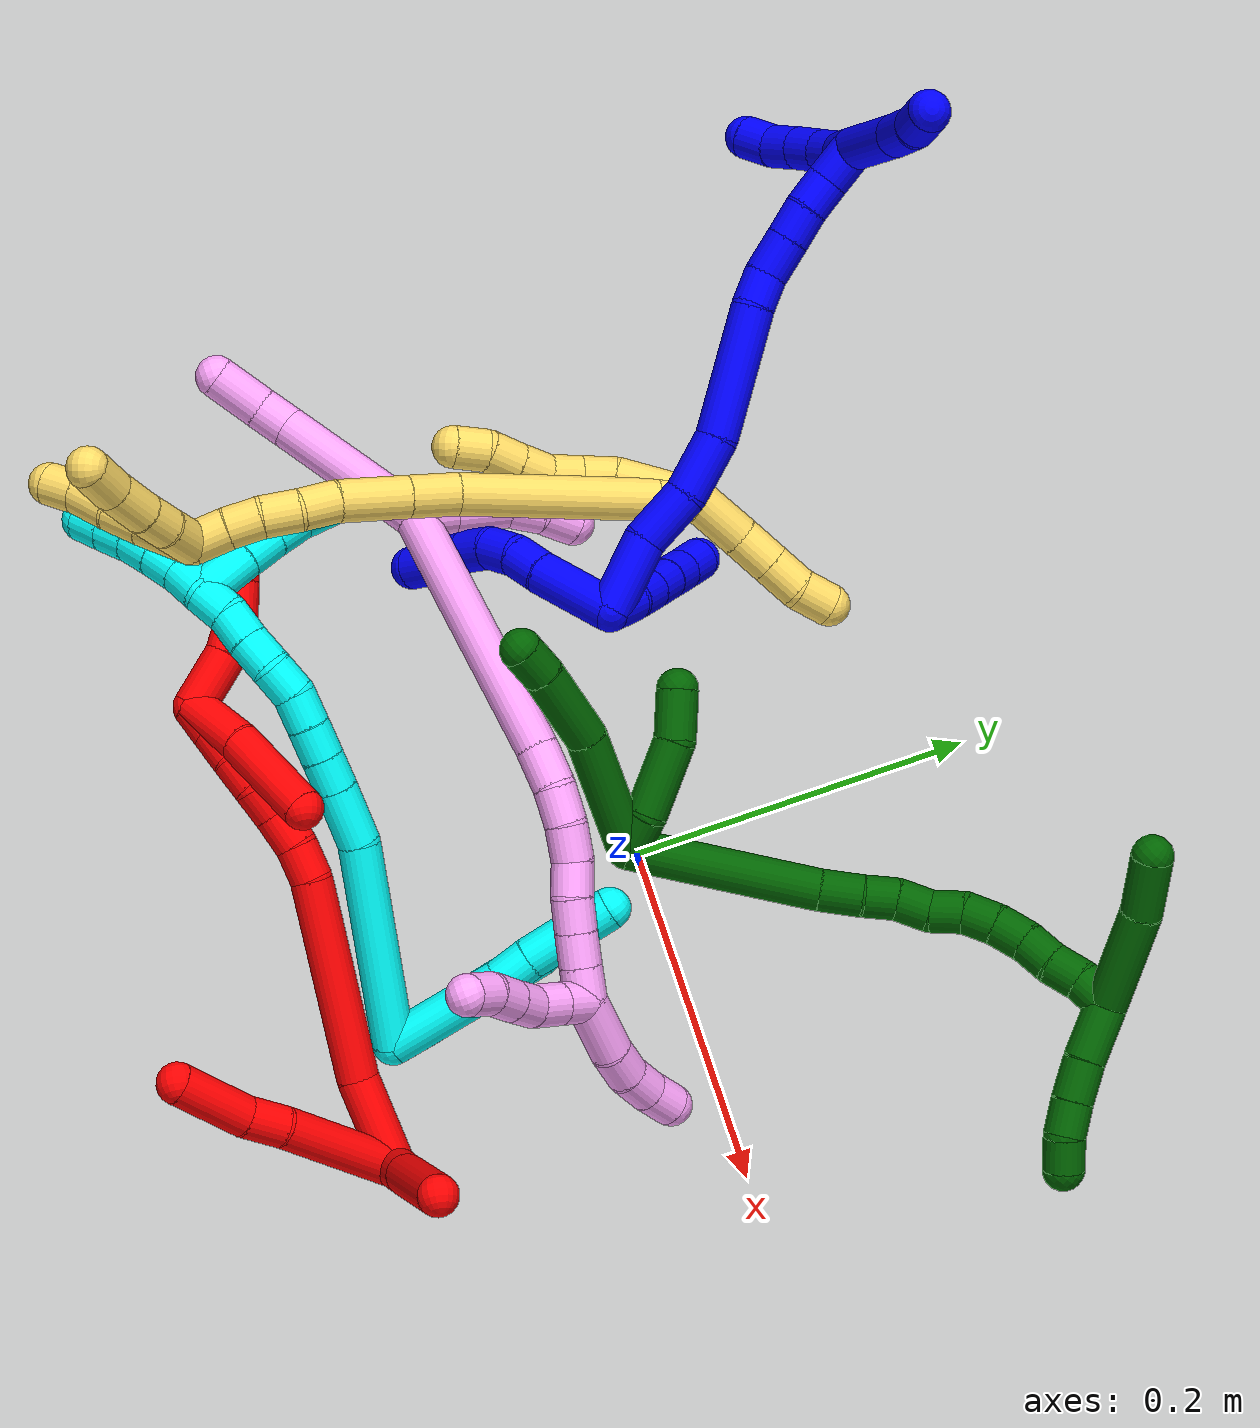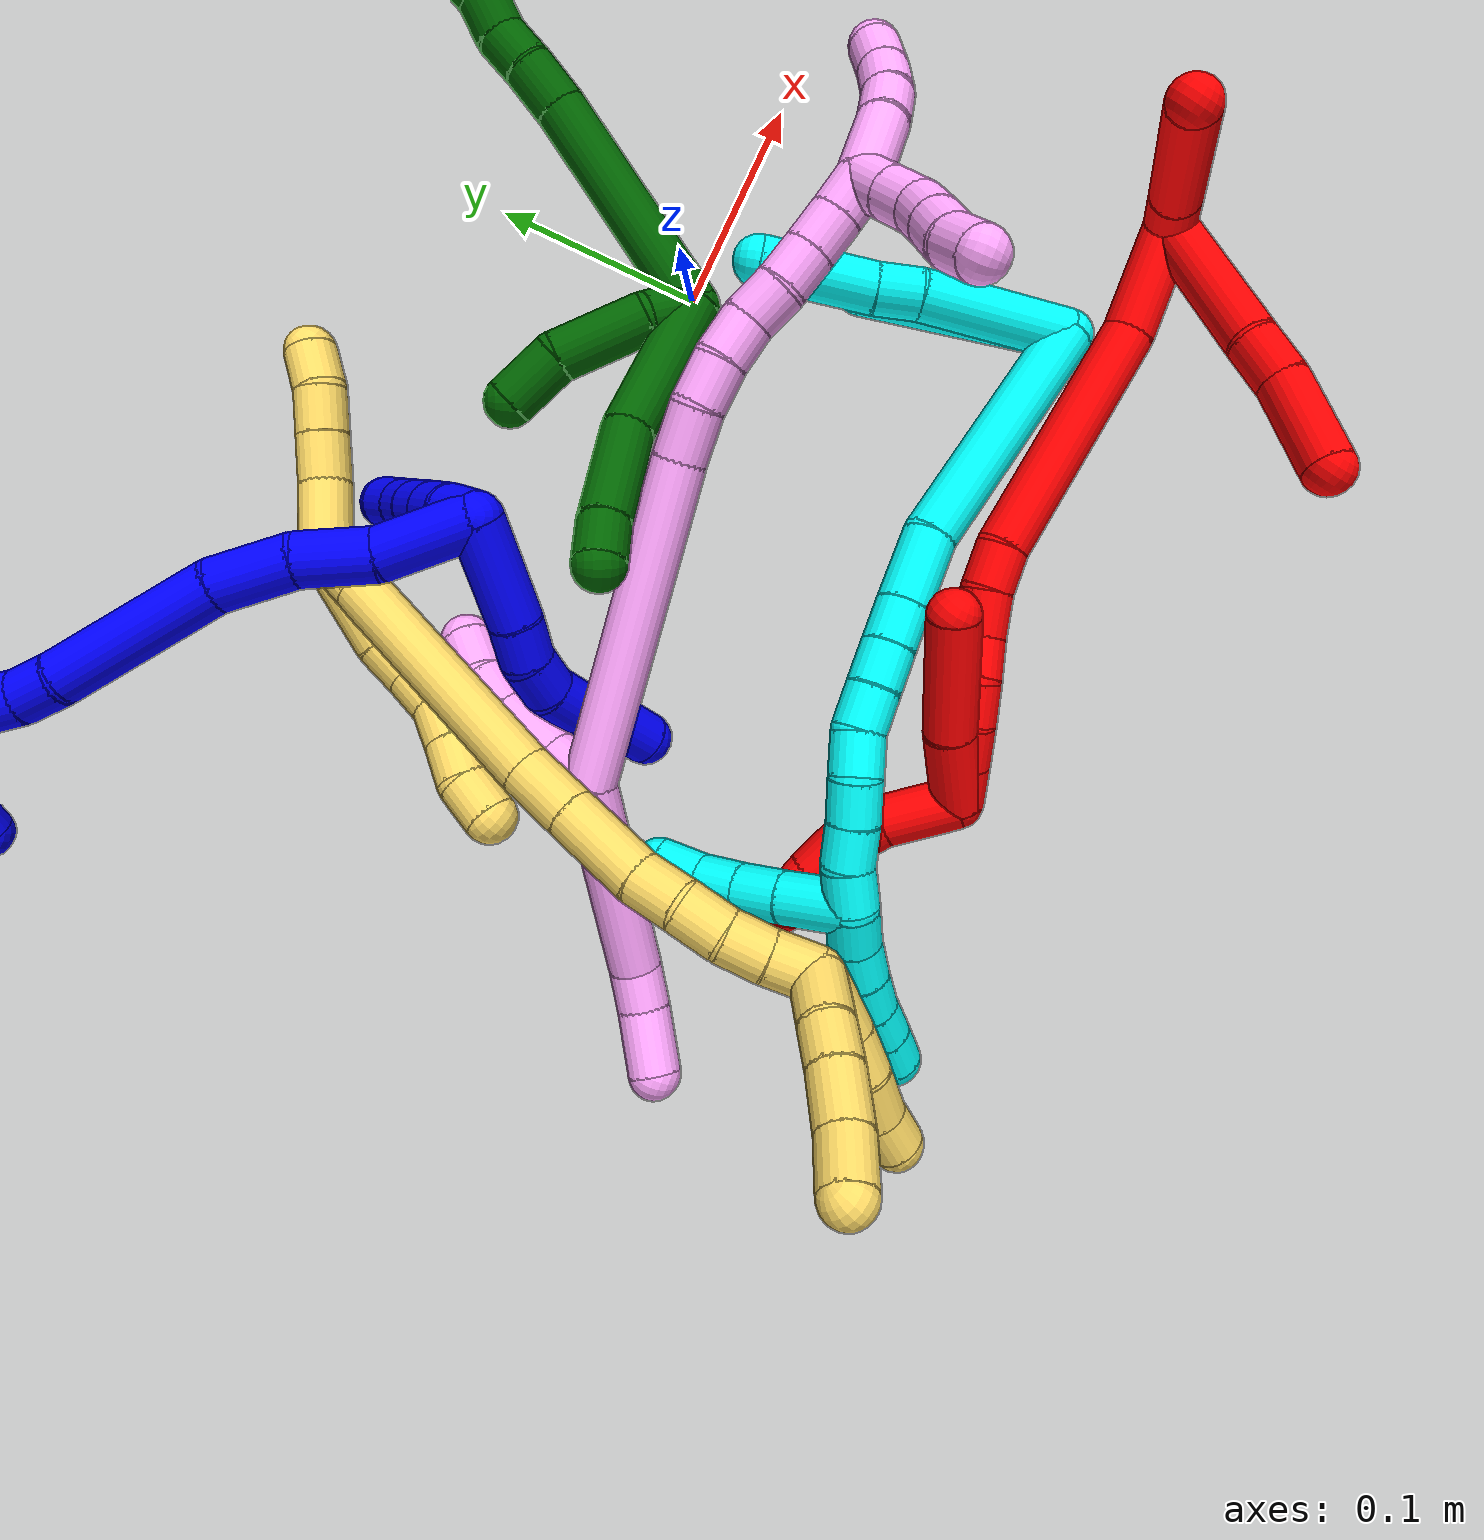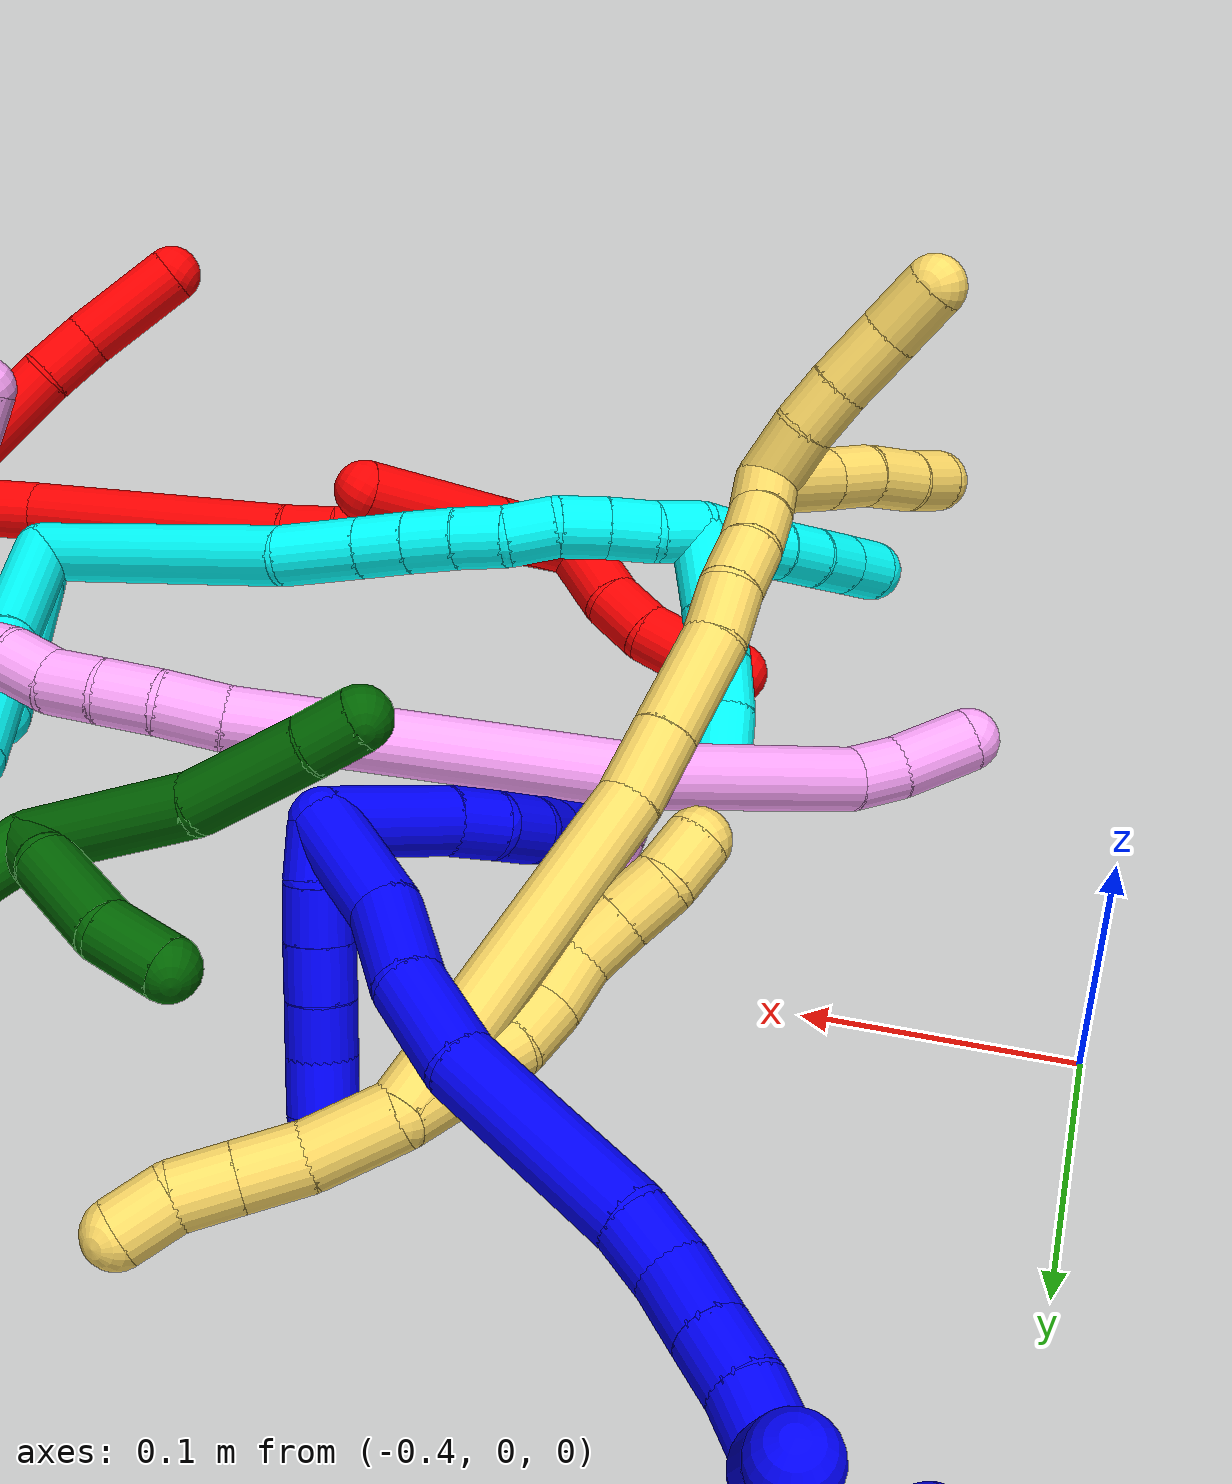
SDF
<sdf version="1.7">
 <world name="default">
  <plugin name="TubeGeneratorPlugin" filename="libtube_generator_plugin.so"/>
  <model name="photoneo_s_sensor">
   <static>1</static>
   <pose>0 0 2 1.57079 1.57079 3.14159</pose>
   <link name="link">
    <inertial><mass>0.1</mass></inertial>
    <sensor name="sensor" type="depth">
     <update_rate>30</update_rate>
     <camera>
      <horizontal_fov>1.22</horizontal_fov>
      <image><width>1920</width><height>1200</height><format>B8G8R8</format></image>
      <clip><near>0.1</near><far>4</far></clip>
      <depth_camera><output>points</output></depth_camera>
     </camera>
     <plugin name="camera_plugin" filename="libgazebo_ros_depth_camera.so">
      <baseline>0.2</baseline>
      <alwaysOn>1</alwaysOn>
      <updateRate>0.0</updateRate>
      <cameraName>camera_ir</cameraName>
      <imageTopicName>/camera/color/image_raw</imageTopicName>
      <cameraInfoTopicName>/camera/color/camera_info</cameraInfoTopicName>
      <depthImageTopicName>/camera/depth/image_raw</depthImageTopicName>
      <depthImageCameraInfoTopicName>/camera/depth/camera_info</depthImageCameraInfoTopicName>
      <pointCloudTopicName>/camera/depth/points</pointCloudTopicName>
      <frameName>fr_optical</frameName>
      <pointCloudCutoff>0.1</pointCloudCutoff>
      <pointCloudCutoffMax>2.0</pointCloudCutoffMax>
      <distortionK1>0</distortionK1>
      <distortionK2>0</distortionK2>
      <distortionK3>0</distortionK3>
      <distortionT1>0</distortionT1>
      <distortionT2>0</distortionT2>
      <CxPrime>0</CxPrime>
      <Cx>0</Cx>
      <Cy>0</Cy>
      <focalLength>0</focalLength>
      <hackBaseline>0</hackBaseline>
     </plugin>
    </sensor>
   </link>
  </model>
  <gravity>0 0 -9.8</gravity>
  <magnetic_field>6e-06 2.3e-05 -4.2e-05</magnetic_field>
  <atmosphere type="adiabatic"/>
  <physics name="default_physics" default="0" type="ode">
   <max_step_size>0.003</max_step_size>
   <real_time_factor>1</real_time_factor>
   <real_time_update_rate>1000</real_time_update_rate>
   <max_contacts>10000</max_contacts>
   <ode>
    <solver>
     <type>quick</type>
     <iters>100</iters>
     <sor>1.3</sor>
     <use_dynamic_moi_rescaling>0</use_dynamic_moi_rescaling>
    </solver>
    <constraints>
     <contact_max_correcting_vel>0</contact_max_correcting_vel>
     <contact_surface_layer>0.001</contact_surface_layer>
     <cfm>0</cfm>
     <erp>0.2</erp>
    </constraints>
   </ode>
  </physics>
  <scene><ambient>0.4 0.4 0.4 1</ambient><background>0.7 0.7 0.7 1</background><shadows>0</shadows></scene>
  <audio><device>default</device></audio>
  <spherical_coordinates>
   <surface_model>EARTH_WGS84</surface_model>
   <latitude_deg>0</latitude_deg>
   <longitude_deg>0</longitude_deg>
   <elevation>0</elevation>
   <heading_deg>0</heading_deg>
  </spherical_coordinates>
  <model name="bin">
   <static>1</static>
   <link name="bottom">
    <collision name="collision-bottom">
     <pose>0 0 -0.01 0 -0 0</pose>
     <geometry><box><size>0.8 0.6 0.02</size></box></geometry>
     <surface>
      <friction><ode><mu>100</mu><mu2>100</mu2></ode></friction>
      <contact><collide_bitmask>65535</collide_bitmask></contact>
     </surface>
    </collision>
   </link>
   <link name="west_wall">
    <collision name="collision-west_wall">
     <pose>-0.41 0 0.1 0 -0 0</pose>
     <geometry><box><size>0.02 0.6 0.2</size></box></geometry>
     <surface>
      <friction><ode><mu>100</mu><mu2>100</mu2></ode></friction>
      <contact><collide_bitmask>65535</collide_bitmask></contact>
     </surface>
    </collision>
   </link>
   <link name="east_wall">
    <collision name="collision-east_wall">
     <pose>0.41 0 0.1 0 -0 0</pose>
     <geometry><box><size>0.02 0.6 0.2</size></box></geometry>
     <surface>
      <friction><ode><mu>100</mu><mu2>100</mu2></ode></friction>
      <contact><collide_bitmask>65535</collide_bitmask></contact>
     </surface>
    </collision>
   </link>
   <link name="south_wall">
    <collision name="collision-south_wall">
     <pose>0 -0.31 0.1 0 -0 0</pose>
     <geometry><box><size>0.8 0.02 0.2</size></box></geometry>
     <surface>
      <friction><ode><mu>100</mu><mu2>100</mu2></ode></friction>
      <contact><collide_bitmask>65535</collide_bitmask></contact>
     </surface>
    </collision>
   </link>
   <link name="north_wall">
    <collision name="collision-north_wall">
     <pose>0 0.31 0.1 0 -0 0</pose>
     <geometry><box><size>0.8 0.02 0.2</size></box></geometry>
     <surface>
      <friction><ode><mu>100</mu><mu2>100</mu2></ode></friction>
      <contact><collide_bitmask>65535</collide_bitmask></contact>
     </surface>
    </collision>
   </link>
  </model>
  <model name="1">
   <static>0</static>
   <link name="1">
    <collision name="collision-cylinder-e_1_2_8">
     <pose>-0.017729 -0.012475 -0.011765 2.32689 -0.802058 -1.55331</pose>
     <geometry><cylinder><radius>0.0125</radius><length>0.04933</length></cylinder></geometry>
     <surface>
      <friction><ode><mu>1.16</mu><mu2>1.16</mu2><slip1>0</slip1><slip2>0</slip2></ode></friction>
      <contact><ode><kp>1e+06</kp><kd>1</kd><max_vel>0</max_vel><min_depth>0.001</min_depth></ode></contact>
     </surface>
    </collision>
    <visual name="visual-cylinder-e_1_2_8">
     <pose>-0.017729 -0.012475 -0.011765 2.32689 -0.802058 -1.55331</pose>
     <geometry><cylinder><radius>0.0125</radius><length>0.04933</length></cylinder></geometry>
     <material><ambient>0 0 1 1</ambient></material>
    </visual>
    <collision name="collision-cylinder-e_2_8_9">
     <pose>-0.042888 -0.029096 -0.02879 2.47418 -0.837238 -1.81776</pose>
     <geometry><cylinder><radius>0.0125</radius><length>0.020007</length></cylinder></geometry>
     <surface>
      <friction><ode><mu>1.16</mu><mu2>1.16</mu2><slip1>0</slip1><slip2>0</slip2></ode></friction>
      <contact><ode><kp>1e+06</kp><kd>1</kd><max_vel>0</max_vel><min_depth>0.001</min_depth></ode></contact>
     </surface>
    </collision>
    <visual name="visual-cylinder-e_2_8_9">
     <pose>-0.042888 -0.029096 -0.02879 2.47418 -0.837238 -1.81776</pose>
     <geometry><cylinder><radius>0.0125</radius><length>0.020007</length></cylinder></geometry>
     <material><ambient>0 0 1 1</ambient></material>
    </visual>
    <collision name="collision-cylinder-e_3_9_10">
     <pose>-0.055451 -0.038486 -0.04098 2.49382 -0.533441 -1.36631</pose>
     <geometry><cylinder><radius>0.0125</radius><length>0.020185</length></cylinder></geometry>
     <surface>
      <friction><ode><mu>1.16</mu><mu2>1.16</mu2><slip1>0</slip1><slip2>0</slip2></ode></friction>
      <contact><ode><kp>1e+06</kp><kd>1</kd><max_vel>0</max_vel><min_depth>0.001</min_depth></ode></contact>
     </surface>
    </collision>
    <visual name="visual-cylinder-e_3_9_10">
     <pose>-0.055451 -0.038486 -0.04098 2.49382 -0.533441 -1.36631</pose>
     <geometry><cylinder><radius>0.0125</radius><length>0.020185</length></cylinder></geometry>
     <material><ambient>0 0 1 1</ambient></material>
    </visual>
    <collision name="collision-cylinder-e_4_10_11">
     <pose>-0.062684 -0.049862 -0.055534 2.46418 -0.211547 -0.585436</pose>
     <geometry><cylinder><radius>0.0125</radius><length>0.020014</length></cylinder></geometry>
     <surface>
      <friction><ode><mu>1.16</mu><mu2>1.16</mu2><slip1>0</slip1><slip2>0</slip2></ode></friction>
      <contact><ode><kp>1e+06</kp><kd>1</kd><max_vel>0</max_vel><min_depth>0.001</min_depth></ode></contact>
     </surface>
    </collision>
    <visual name="visual-cylinder-e_4_10_11">
     <pose>-0.062684 -0.049862 -0.055534 2.46418 -0.211547 -0.585436</pose>
     <geometry><cylinder><radius>0.0125</radius><length>0.020014</length></cylinder></geometry>
     <material><ambient>0 0 1 1</ambient></material>
    </visual>
    <collision name="collision-cylinder-e_5_11_12">
     <pose>-0.065038 -0.064063 -0.069359 2.22609 -0.024815 -0.050363</pose>
     <geometry><cylinder><radius>0.0125</radius><length>0.020359</length></cylinder></geometry>
     <surface>
      <friction><ode><mu>1.16</mu><mu2>1.16</mu2><slip1>0</slip1><slip2>0</slip2></ode></friction>
      <contact><ode><kp>1e+06</kp><kd>1</kd><max_vel>0</max_vel><min_depth>0.001</min_depth></ode></contact>
     </surface>
    </collision>
    <visual name="visual-cylinder-e_5_11_12">
     <pose>-0.065038 -0.064063 -0.069359 2.22609 -0.024815 -0.050363</pose>
     <geometry><cylinder><radius>0.0125</radius><length>0.020359</length></cylinder></geometry>
     <material><ambient>0 0 1 1</ambient></material>
    </visual>
    <collision name="collision-cylinder-e_6_12_6">
     <pose>-0.067174 -0.078922 -0.082729 2.38329 -0.188483 -0.465861</pose>
     <geometry><cylinder><radius>0.0125</radius><length>0.020105</length></cylinder></geometry>
     <surface>
      <friction><ode><mu>1.16</mu><mu2>1.16</mu2><slip1>0</slip1><slip2>0</slip2></ode></friction>
      <contact><ode><kp>1e+06</kp><kd>1</kd><max_vel>0</max_vel><min_depth>0.001</min_depth></ode></contact>
     </surface>
    </collision>
    <visual name="visual-cylinder-e_6_12_6">
     <pose>-0.067174 -0.078922 -0.082729 2.38329 -0.188483 -0.465861</pose>
     <geometry><cylinder><radius>0.0125</radius><length>0.020105</length></cylinder></geometry>
     <material><ambient>0 0 1 1</ambient></material>
    </visual>
    <collision name="collision-cylinder-e_1_2_13">
     <pose>-0.000382 0.007913 -0.006102 -2.22771 -0.038236 0.077743</pose>
     <geometry><cylinder><radius>0.0125</radius><length>0.02</length></cylinder></geometry>
     <surface>
      <friction><ode><mu>1.16</mu><mu2>1.16</mu2><slip1>0</slip1><slip2>0</slip2></ode></friction>
      <contact><ode><kp>1e+06</kp><kd>1</kd><max_vel>0</max_vel><min_depth>0.001</min_depth></ode></contact>
     </surface>
    </collision>
    <visual name="visual-cylinder-e_1_2_13">
     <pose>-0.000382 0.007913 -0.006102 -2.22771 -0.038236 0.077743</pose>
     <geometry><cylinder><radius>0.0125</radius><length>0.02</length></cylinder></geometry>
     <material><ambient>0 0 1 1</ambient></material>
    </visual>
    <collision name="collision-cylinder-e_2_13_14">
     <pose>-0.001581 0.022344 -0.019745 -2.42878 -0.081741 0.218799</pose>
     <geometry><cylinder><radius>0.0125</radius><length>0.02</length></cylinder></geometry>
     <surface>
      <friction><ode><mu>1.16</mu><mu2>1.16</mu2><slip1>0</slip1><slip2>0</slip2></ode></friction>
      <contact><ode><kp>1e+06</kp><kd>1</kd><max_vel>0</max_vel><min_depth>0.001</min_depth></ode></contact>
     </surface>
    </collision>
    <visual name="visual-cylinder-e_2_13_14">
     <pose>-0.001581 0.022344 -0.019745 -2.42878 -0.081741 0.218799</pose>
     <geometry><cylinder><radius>0.0125</radius><length>0.02</length></cylinder></geometry>
     <material><ambient>0 0 1 1</ambient></material>
    </visual>
    <collision name="collision-cylinder-e_3_14_15">
     <pose>-0.003382 0.035313 -0.034861 -2.43622 -0.098626 0.266578</pose>
     <geometry><cylinder><radius>0.0125</radius><length>0.02</length></cylinder></geometry>
     <surface>
      <friction><ode><mu>1.16</mu><mu2>1.16</mu2><slip1>0</slip1><slip2>0</slip2></ode></friction>
      <contact><ode><kp>1e+06</kp><kd>1</kd><max_vel>0</max_vel><min_depth>0.001</min_depth></ode></contact>
     </surface>
    </collision>
    <visual name="visual-cylinder-e_3_14_15">
     <pose>-0.003382 0.035313 -0.034861 -2.43622 -0.098626 0.266578</pose>
     <geometry><cylinder><radius>0.0125</radius><length>0.02</length></cylinder></geometry>
     <material><ambient>0 0 1 1</ambient></material>
    </visual>
    <collision name="collision-cylinder-e_4_15_16">
     <pose>-0.005155 0.047863 -0.050324 -2.48332 -0.078906 0.230114</pose>
     <geometry><cylinder><radius>0.0125</radius><length>0.02</length></cylinder></geometry>
     <surface>
      <friction><ode><mu>1.16</mu><mu2>1.16</mu2><slip1>0</slip1><slip2>0</slip2></ode></friction>
      <contact><ode><kp>1e+06</kp><kd>1</kd><max_vel>0</max_vel><min_depth>0.001</min_depth></ode></contact>
     </surface>
    </collision>
    <visual name="visual-cylinder-e_4_15_16">
     <pose>-0.005155 0.047863 -0.050324 -2.48332 -0.078906 0.230114</pose>
     <geometry><cylinder><radius>0.0125</radius><length>0.02</length></cylinder></geometry>
     <material><ambient>0 0 1 1</ambient></material>
    </visual>
    <collision name="collision-cylinder-e_5_16_5">
     <pose>-0.007123 0.061036 -0.065179 -2.34874 -0.118254 0.280975</pose>
     <geometry><cylinder><radius>0.0125</radius><length>0.02</length></cylinder></geometry>
     <surface>
      <friction><ode><mu>1.16</mu><mu2>1.16</mu2><slip1>0</slip1><slip2>0</slip2></ode></friction>
      <contact><ode><kp>1e+06</kp><kd>1</kd><max_vel>0</max_vel><min_depth>0.001</min_depth></ode></contact>
     </surface>
    </collision>
    <visual name="visual-cylinder-e_5_16_5">
     <pose>-0.007123 0.061036 -0.065179 -2.34874 -0.118254 0.280975</pose>
     <geometry><cylinder><radius>0.0125</radius><length>0.02</length></cylinder></geometry>
     <material><ambient>0 0 1 1</ambient></material>
    </visual>
    <collision name="collision-cylinder-e_1_2_17">
     <pose>-0.014435 0.01698 0.000565 -1.53756 -0.704313 0.683061</pose>
     <geometry><cylinder><radius>0.0125</radius><length>0.044587</length></cylinder></geometry>
     <surface>
      <friction><ode><mu>1.16</mu><mu2>1.16</mu2><slip1>0</slip1><slip2>0</slip2></ode></friction>
      <contact><ode><kp>1e+06</kp><kd>1</kd><max_vel>0</max_vel><min_depth>0.001</min_depth></ode></contact>
     </surface>
    </collision>
    <visual name="visual-cylinder-e_1_2_17">
     <pose>-0.014435 0.01698 0.000565 -1.53756 -0.704313 0.683061</pose>
     <geometry><cylinder><radius>0.0125</radius><length>0.044587</length></cylinder></geometry>
     <material><ambient>0 0 1 1</ambient></material>
    </visual>
    <collision name="collision-cylinder-e_2_17_18">
     <pose>-0.036131 0.049553 0.003652 -1.4104 -0.430825 0.368284</pose>
     <geometry><cylinder><radius>0.0125</radius><length>0.03477</length></cylinder></geometry>
     <surface>
      <friction><ode><mu>1.16</mu><mu2>1.16</mu2><slip1>0</slip1><slip2>0</slip2></ode></friction>
      <contact><ode><kp>1e+06</kp><kd>1</kd><max_vel>0</max_vel><min_depth>0.001</min_depth></ode></contact>
     </surface>
    </collision>
    <visual name="visual-cylinder-e_2_17_18">
     <pose>-0.036131 0.049553 0.003652 -1.4104 -0.430825 0.368284</pose>
     <geometry><cylinder><radius>0.0125</radius><length>0.03477</length></cylinder></geometry>
     <material><ambient>0 0 1 1</ambient></material>
    </visual>
    <collision name="collision-cylinder-e_3_18_19">
     <pose>-0.054594 0.079288 0.007605 -1.47001 -0.667463 0.60742</pose>
     <geometry><cylinder><radius>0.0125</radius><length>0.036195</length></cylinder></geometry>
     <surface>
      <friction><ode><mu>1.16</mu><mu2>1.16</mu2><slip1>0</slip1><slip2>0</slip2></ode></friction>
      <contact><ode><kp>1e+06</kp><kd>1</kd><max_vel>0</max_vel><min_depth>0.001</min_depth></ode></contact>
     </surface>
    </collision>
    <visual name="visual-cylinder-e_3_18_19">
     <pose>-0.054594 0.079288 0.007605 -1.47001 -0.667463 0.60742</pose>
     <geometry><cylinder><radius>0.0125</radius><length>0.036195</length></cylinder></geometry>
     <material><ambient>0 0 1 1</ambient></material>
    </visual>
    <collision name="collision-cylinder-e_4_19_20">
     <pose>-0.095873 0.117372 0.011211 -1.48015 -0.896486 0.827605</pose>
     <geometry><cylinder><radius>0.0125</radius><length>0.077009</length></cylinder></geometry>
     <surface>
      <friction><ode><mu>1.16</mu><mu2>1.16</mu2><slip1>0</slip1><slip2>0</slip2></ode></friction>
      <contact><ode><kp>1e+06</kp><kd>1</kd><max_vel>0</max_vel><min_depth>0.001</min_depth></ode></contact>
     </surface>
    </collision>
    <visual name="visual-cylinder-e_4_19_20">
     <pose>-0.095873 0.117372 0.011211 -1.48015 -0.896486 0.827605</pose>
     <geometry><cylinder><radius>0.0125</radius><length>0.077009</length></cylinder></geometry>
     <material><ambient>0 0 1 1</ambient></material>
    </visual>
    <collision name="collision-cylinder-e_5_20_21">
     <pose>-0.132974 0.148399 0.012457 -1.70141 -0.776688 0.872776</pose>
     <geometry><cylinder><radius>0.0125</radius><length>0.020039</length></cylinder></geometry>
     <surface>
      <friction><ode><mu>1.16</mu><mu2>1.16</mu2><slip1>0</slip1><slip2>0</slip2></ode></friction>
      <contact><ode><kp>1e+06</kp><kd>1</kd><max_vel>0</max_vel><min_depth>0.001</min_depth></ode></contact>
     </surface>
    </collision>
    <visual name="visual-cylinder-e_5_20_21">
     <pose>-0.132974 0.148399 0.012457 -1.70141 -0.776688 0.872776</pose>
     <geometry><cylinder><radius>0.0125</radius><length>0.020039</length></cylinder></geometry>
     <material><ambient>0 0 1 1</ambient></material>
    </visual>
    <collision name="collision-cylinder-e_6_21_22">
     <pose>-0.146872 0.165158 0.0131 -1.40956 -0.611766 0.524775</pose>
     <geometry><cylinder><radius>0.0125</radius><length>0.023944</length></cylinder></geometry>
     <surface>
      <friction><ode><mu>1.16</mu><mu2>1.16</mu2><slip1>0</slip1><slip2>0</slip2></ode></friction>
      <contact><ode><kp>1e+06</kp><kd>1</kd><max_vel>0</max_vel><min_depth>0.001</min_depth></ode></contact>
     </surface>
    </collision>
    <visual name="visual-cylinder-e_6_21_22">
     <pose>-0.146872 0.165158 0.0131 -1.40956 -0.611766 0.524775</pose>
     <geometry><cylinder><radius>0.0125</radius><length>0.023944</length></cylinder></geometry>
     <material><ambient>0 0 1 1</ambient></material>
    </visual>
    <collision name="collision-cylinder-e_7_22_23">
     <pose>-0.159666 0.182969 0.015918 -1.41896 -0.623347 0.539755</pose>
     <geometry><cylinder><radius>0.0125</radius><length>0.020277</length></cylinder></geometry>
     <surface>
      <friction><ode><mu>1.16</mu><mu2>1.16</mu2><slip1>0</slip1><slip2>0</slip2></ode></friction>
      <contact><ode><kp>1e+06</kp><kd>1</kd><max_vel>0</max_vel><min_depth>0.001</min_depth></ode></contact>
     </surface>
    </collision>
    <visual name="visual-cylinder-e_7_22_23">
     <pose>-0.159666 0.182969 0.015918 -1.41896 -0.623347 0.539755</pose>
     <geometry><cylinder><radius>0.0125</radius><length>0.020277</length></cylinder></geometry>
     <material><ambient>0 0 1 1</ambient></material>
    </visual>
    <collision name="collision-cylinder-e_8_23_24">
     <pose>-0.170561 0.199823 0.017758 -1.50274 -0.517712 0.484988</pose>
     <geometry><cylinder><radius>0.0125</radius><length>0.020109</length></cylinder></geometry>
     <surface>
      <friction><ode><mu>1.16</mu><mu2>1.16</mu2><slip1>0</slip1><slip2>0</slip2></ode></friction>
      <contact><ode><kp>1e+06</kp><kd>1</kd><max_vel>0</max_vel><min_depth>0.001</min_depth></ode></contact>
     </surface>
    </collision>
    <visual name="visual-cylinder-e_8_23_24">
     <pose>-0.170561 0.199823 0.017758 -1.50274 -0.517712 0.484988</pose>
     <geometry><cylinder><radius>0.0125</radius><length>0.020109</length></cylinder></geometry>
     <material><ambient>0 0 1 1</ambient></material>
    </visual>
    <collision name="collision-cylinder-e_9_24_1">
     <pose>-0.18092 0.218388 0.021013 -1.30689 -0.48555 0.374793</pose>
     <geometry><cylinder><radius>0.0125</radius><length>0.023069</length></cylinder></geometry>
     <surface>
      <friction><ode><mu>1.16</mu><mu2>1.16</mu2><slip1>0</slip1><slip2>0</slip2></ode></friction>
      <contact><ode><kp>1e+06</kp><kd>1</kd><max_vel>0</max_vel><min_depth>0.001</min_depth></ode></contact>
     </surface>
    </collision>
    <visual name="visual-cylinder-e_9_24_1">
     <pose>-0.18092 0.218388 0.021013 -1.30689 -0.48555 0.374793</pose>
     <geometry><cylinder><radius>0.0125</radius><length>0.023069</length></cylinder></geometry>
     <material><ambient>0 0 1 1</ambient></material>
    </visual>
    <collision name="collision-cylinder-e_1_1_25">
     <pose>-0.187237 0.226789 0.013823 2.99576 -0.09356 -1.13987</pose>
     <geometry><cylinder><radius>0.0125</radius><length>0.02</length></cylinder></geometry>
     <surface>
      <friction><ode><mu>1.16</mu><mu2>1.16</mu2><slip1>0</slip1><slip2>0</slip2></ode></friction>
      <contact><ode><kp>1e+06</kp><kd>1</kd><max_vel>0</max_vel><min_depth>0.001</min_depth></ode></contact>
     </surface>
    </collision>
    <visual name="visual-cylinder-e_1_1_25">
     <pose>-0.187237 0.226789 0.013823 2.99576 -0.09356 -1.13987</pose>
     <geometry><cylinder><radius>0.0125</radius><length>0.02</length></cylinder></geometry>
     <material><ambient>0 0 1 1</ambient></material>
    </visual>
    <collision name="collision-cylinder-e_2_25_26">
     <pose>-0.19151 0.222142 -0.004894 2.79528 -0.340394 -1.55321</pose>
     <geometry><cylinder><radius>0.0125</radius><length>0.02</length></cylinder></geometry>
     <surface>
      <friction><ode><mu>1.16</mu><mu2>1.16</mu2><slip1>0</slip1><slip2>0</slip2></ode></friction>
      <contact><ode><kp>1e+06</kp><kd>1</kd><max_vel>0</max_vel><min_depth>0.001</min_depth></ode></contact>
     </surface>
    </collision>
    <visual name="visual-cylinder-e_2_25_26">
     <pose>-0.19151 0.222142 -0.004894 2.79528 -0.340394 -1.55321</pose>
     <geometry><cylinder><radius>0.0125</radius><length>0.02</length></cylinder></geometry>
     <material><ambient>0 0 1 1</ambient></material>
    </visual>
    <collision name="collision-cylinder-e_3_26_27">
     <pose>-0.198867 0.214376 -0.021697 2.61942 -0.413576 -1.33126</pose>
     <geometry><cylinder><radius>0.0125</radius><length>0.02</length></cylinder></geometry>
     <surface>
      <friction><ode><mu>1.16</mu><mu2>1.16</mu2><slip1>0</slip1><slip2>0</slip2></ode></friction>
      <contact><ode><kp>1e+06</kp><kd>1</kd><max_vel>0</max_vel><min_depth>0.001</min_depth></ode></contact>
     </surface>
    </collision>
    <visual name="visual-cylinder-e_3_26_27">
     <pose>-0.198867 0.214376 -0.021697 2.61942 -0.413576 -1.33126</pose>
     <geometry><cylinder><radius>0.0125</radius><length>0.02</length></cylinder></geometry>
     <material><ambient>0 0 1 1</ambient></material>
    </visual>
    <collision name="collision-cylinder-e_4_27_28">
     <pose>-0.206792 0.204699 -0.037292 2.55323 -0.401237 -1.18227</pose>
     <geometry><cylinder><radius>0.0125</radius><length>0.02</length></cylinder></geometry>
     <surface>
      <friction><ode><mu>1.16</mu><mu2>1.16</mu2><slip1>0</slip1><slip2>0</slip2></ode></friction>
      <contact><ode><kp>1e+06</kp><kd>1</kd><max_vel>0</max_vel><min_depth>0.001</min_depth></ode></contact>
     </surface>
    </collision>
    <visual name="visual-cylinder-e_4_27_28">
     <pose>-0.206792 0.204699 -0.037292 2.55323 -0.401237 -1.18227</pose>
     <geometry><cylinder><radius>0.0125</radius><length>0.02</length></cylinder></geometry>
     <material><ambient>0 0 1 1</ambient></material>
    </visual>
    <collision name="collision-cylinder-e_5_28_4">
     <pose>-0.216629 0.19442 -0.051121 2.44426 -0.635011 -1.47004</pose>
     <geometry><cylinder><radius>0.0125</radius><length>0.02</length></cylinder></geometry>
     <surface>
      <friction><ode><mu>1.16</mu><mu2>1.16</mu2><slip1>0</slip1><slip2>0</slip2></ode></friction>
      <contact><ode><kp>1e+06</kp><kd>1</kd><max_vel>0</max_vel><min_depth>0.001</min_depth></ode></contact>
     </surface>
    </collision>
    <visual name="visual-cylinder-e_5_28_4">
     <pose>-0.216629 0.19442 -0.051121 2.44426 -0.635011 -1.47004</pose>
     <geometry><cylinder><radius>0.0125</radius><length>0.02</length></cylinder></geometry>
     <material><ambient>0 0 1 1</ambient></material>
    </visual>
    <collision name="collision-cylinder-e_1_1_29">
     <pose>-0.183335 0.2362 0.04797 -0.316754 0.11555 -0.018475</pose>
     <geometry><cylinder><radius>0.0125</radius><length>0.05148</length></cylinder></geometry>
     <surface>
      <friction><ode><mu>1.16</mu><mu2>1.16</mu2><slip1>0</slip1><slip2>0</slip2></ode></friction>
      <contact><ode><kp>1e+06</kp><kd>1</kd><max_vel>0</max_vel><min_depth>0.001</min_depth></ode></contact>
     </surface>
    </collision>
    <visual name="visual-cylinder-e_1_1_29">
     <pose>-0.183335 0.2362 0.04797 -0.316754 0.11555 -0.018475</pose>
     <geometry><cylinder><radius>0.0125</radius><length>0.05148</length></cylinder></geometry>
     <material><ambient>0 0 1 1</ambient></material>
    </visual>
    <collision name="collision-cylinder-e_2_29_30">
     <pose>-0.179416 0.247367 0.085691 -0.234249 0.068818 -0.008101</pose>
     <geometry><cylinder><radius>0.0125</radius><length>0.02767</length></cylinder></geometry>
     <surface>
      <friction><ode><mu>1.16</mu><mu2>1.16</mu2><slip1>0</slip1><slip2>0</slip2></ode></friction>
      <contact><ode><kp>1e+06</kp><kd>1</kd><max_vel>0</max_vel><min_depth>0.001</min_depth></ode></contact>
     </surface>
    </collision>
    <visual name="visual-cylinder-e_2_29_30">
     <pose>-0.179416 0.247367 0.085691 -0.234249 0.068818 -0.008101</pose>
     <geometry><cylinder><radius>0.0125</radius><length>0.02767</length></cylinder></geometry>
     <material><ambient>0 0 1 1</ambient></material>
    </visual>
    <collision name="collision-cylinder-e_3_30_3">
     <pose>-0.180277 0.253744 0.108881 -0.314189 -0.174676 0.027737</pose>
     <geometry><cylinder><radius>0.0125</radius><length>0.020851</length></cylinder></geometry>
     <surface>
      <friction><ode><mu>1.16</mu><mu2>1.16</mu2><slip1>0</slip1><slip2>0</slip2></ode></friction>
      <contact><ode><kp>1e+06</kp><kd>1</kd><max_vel>0</max_vel><min_depth>0.001</min_depth></ode></contact>
     </surface>
    </collision>
    <visual name="visual-cylinder-e_3_30_3">
     <pose>-0.180277 0.253744 0.108881 -0.314189 -0.174676 0.027737</pose>
     <geometry><cylinder><radius>0.0125</radius><length>0.020851</length></cylinder></geometry>
     <material><ambient>0 0 1 1</ambient></material>
    </visual>
    <collision name="collision-sphere-3">
     <pose>-0.182089 0.256917 0.118645 0 -0 0</pose>
     <geometry><sphere><radius>0.0125</radius></sphere></geometry>
     <surface>
      <friction><ode><mu>1.16</mu><mu2>1.16</mu2><slip1>0</slip1><slip2>0</slip2></ode></friction>
      <contact><ode><kp>1e+06</kp><kd>1</kd><max_vel>0</max_vel><min_depth>0.001</min_depth></ode></contact>
     </surface>
    </collision>
    <visual name="visual-sphere-3">
     <pose>-0.182089 0.256917 0.118645 0 -0 0</pose>
     <geometry><sphere><radius>0.0125</radius></sphere></geometry>
     <material><ambient>0 0 1 1</ambient></material>
    </visual>
    <collision name="collision-sphere-30">
     <pose>-0.178465 0.250571 0.099117 0 -0 0</pose>
     <geometry><sphere><radius>0.0125</radius></sphere></geometry>
     <surface>
      <friction><ode><mu>1.16</mu><mu2>1.16</mu2><slip1>0</slip1><slip2>0</slip2></ode></friction>
      <contact><ode><kp>1e+06</kp><kd>1</kd><max_vel>0</max_vel><min_depth>0.001</min_depth></ode></contact>
     </surface>
    </collision>
    <visual name="visual-sphere-30">
     <pose>-0.178465 0.250571 0.099117 0 -0 0</pose>
     <geometry><sphere><radius>0.0125</radius></sphere></geometry>
     <material><ambient>0 0 1 1</ambient></material>
    </visual>
    <collision name="collision-sphere-29">
     <pose>-0.180368 0.244164 0.072266 0 -0 0</pose>
     <geometry><sphere><radius>0.0125</radius></sphere></geometry>
     <surface>
      <friction><ode><mu>1.16</mu><mu2>1.16</mu2><slip1>0</slip1><slip2>0</slip2></ode></friction>
      <contact><ode><kp>1e+06</kp><kd>1</kd><max_vel>0</max_vel><min_depth>0.001</min_depth></ode></contact>
     </surface>
    </collision>
    <visual name="visual-sphere-29">
     <pose>-0.180368 0.244164 0.072266 0 -0 0</pose>
     <geometry><sphere><radius>0.0125</radius></sphere></geometry>
     <material><ambient>0 0 1 1</ambient></material>
    </visual>
    <collision name="collision-sphere-4">
     <pose>-0.222561 0.18925 -0.057292 0 -0 0</pose>
     <geometry><sphere><radius>0.0125</radius></sphere></geometry>
     <surface>
      <friction><ode><mu>1.16</mu><mu2>1.16</mu2><slip1>0</slip1><slip2>0</slip2></ode></friction>
      <contact><ode><kp>1e+06</kp><kd>1</kd><max_vel>0</max_vel><min_depth>0.001</min_depth></ode></contact>
     </surface>
    </collision>
    <visual name="visual-sphere-4">
     <pose>-0.222561 0.18925 -0.057292 0 -0 0</pose>
     <geometry><sphere><radius>0.0125</radius></sphere></geometry>
     <material><ambient>0 0 1 1</ambient></material>
    </visual>
    <collision name="collision-sphere-28">
     <pose>-0.210697 0.19959 -0.044949 0 -0 0</pose>
     <geometry><sphere><radius>0.0125</radius></sphere></geometry>
     <surface>
      <friction><ode><mu>1.16</mu><mu2>1.16</mu2><slip1>0</slip1><slip2>0</slip2></ode></friction>
      <contact><ode><kp>1e+06</kp><kd>1</kd><max_vel>0</max_vel><min_depth>0.001</min_depth></ode></contact>
     </surface>
    </collision>
    <visual name="visual-sphere-28">
     <pose>-0.210697 0.19959 -0.044949 0 -0 0</pose>
     <geometry><sphere><radius>0.0125</radius></sphere></geometry>
     <material><ambient>0 0 1 1</ambient></material>
    </visual>
    <collision name="collision-sphere-27">
     <pose>-0.202886 0.209808 -0.029634 0 -0 0</pose>
     <geometry><sphere><radius>0.0125</radius></sphere></geometry>
     <surface>
      <friction><ode><mu>1.16</mu><mu2>1.16</mu2><slip1>0</slip1><slip2>0</slip2></ode></friction>
      <contact><ode><kp>1e+06</kp><kd>1</kd><max_vel>0</max_vel><min_depth>0.001</min_depth></ode></contact>
     </surface>
    </collision>
    <visual name="visual-sphere-27">
     <pose>-0.202886 0.209808 -0.029634 0 -0 0</pose>
     <geometry><sphere><radius>0.0125</radius></sphere></geometry>
     <material><ambient>0 0 1 1</ambient></material>
    </visual>
    <collision name="collision-sphere-26">
     <pose>-0.194849 0.218943 -0.013761 0 -0 0</pose>
     <geometry><sphere><radius>0.0125</radius></sphere></geometry>
     <surface>
      <friction><ode><mu>1.16</mu><mu2>1.16</mu2><slip1>0</slip1><slip2>0</slip2></ode></friction>
      <contact><ode><kp>1e+06</kp><kd>1</kd><max_vel>0</max_vel><min_depth>0.001</min_depth></ode></contact>
     </surface>
    </collision>
    <visual name="visual-sphere-26">
     <pose>-0.194849 0.218943 -0.013761 0 -0 0</pose>
     <geometry><sphere><radius>0.0125</radius></sphere></geometry>
     <material><ambient>0 0 1 1</ambient></material>
    </visual>
    <collision name="collision-sphere-25">
     <pose>-0.188171 0.225342 0.003973 0 -0 0</pose>
     <geometry><sphere><radius>0.0125</radius></sphere></geometry>
     <surface>
      <friction><ode><mu>1.16</mu><mu2>1.16</mu2><slip1>0</slip1><slip2>0</slip2></ode></friction>
      <contact><ode><kp>1e+06</kp><kd>1</kd><max_vel>0</max_vel><min_depth>0.001</min_depth></ode></contact>
     </surface>
    </collision>
    <visual name="visual-sphere-25">
     <pose>-0.188171 0.225342 0.003973 0 -0 0</pose>
     <geometry><sphere><radius>0.0125</radius></sphere></geometry>
     <material><ambient>0 0 1 1</ambient></material>
    </visual>
    <collision name="collision-sphere-1">
     <pose>-0.186303 0.228236 0.023674 0 -0 0</pose>
     <geometry><sphere><radius>0.0125</radius></sphere></geometry>
     <surface>
      <friction><ode><mu>1.16</mu><mu2>1.16</mu2><slip1>0</slip1><slip2>0</slip2></ode></friction>
      <contact><ode><kp>1e+06</kp><kd>1</kd><max_vel>0</max_vel><min_depth>0.001</min_depth></ode></contact>
     </surface>
    </collision>
    <visual name="visual-sphere-1">
     <pose>-0.186303 0.228236 0.023674 0 -0 0</pose>
     <geometry><sphere><radius>0.0125</radius></sphere></geometry>
     <material><ambient>0 0 1 1</ambient></material>
    </visual>
    <collision name="collision-sphere-24">
     <pose>-0.175537 0.20854 0.018352 0 -0 0</pose>
     <geometry><sphere><radius>0.0125</radius></sphere></geometry>
     <surface>
      <friction><ode><mu>1.16</mu><mu2>1.16</mu2><slip1>0</slip1><slip2>0</slip2></ode></friction>
      <contact><ode><kp>1e+06</kp><kd>1</kd><max_vel>0</max_vel><min_depth>0.001</min_depth></ode></contact>
     </surface>
    </collision>
    <visual name="visual-sphere-24">
     <pose>-0.175537 0.20854 0.018352 0 -0 0</pose>
     <geometry><sphere><radius>0.0125</radius></sphere></geometry>
     <material><ambient>0 0 1 1</ambient></material>
    </visual>
    <collision name="collision-sphere-23">
     <pose>-0.165585 0.191106 0.017163 0 -0 0</pose>
     <geometry><sphere><radius>0.0125</radius></sphere></geometry>
     <surface>
      <friction><ode><mu>1.16</mu><mu2>1.16</mu2><slip1>0</slip1><slip2>0</slip2></ode></friction>
      <contact><ode><kp>1e+06</kp><kd>1</kd><max_vel>0</max_vel><min_depth>0.001</min_depth></ode></contact>
     </surface>
    </collision>
    <visual name="visual-sphere-23">
     <pose>-0.165585 0.191106 0.017163 0 -0 0</pose>
     <geometry><sphere><radius>0.0125</radius></sphere></geometry>
     <material><ambient>0 0 1 1</ambient></material>
    </visual>
    <collision name="collision-sphere-22">
     <pose>-0.153748 0.174832 0.014673 0 -0 0</pose>
     <geometry><sphere><radius>0.0125</radius></sphere></geometry>
     <surface>
      <friction><ode><mu>1.16</mu><mu2>1.16</mu2><slip1>0</slip1><slip2>0</slip2></ode></friction>
      <contact><ode><kp>1e+06</kp><kd>1</kd><max_vel>0</max_vel><min_depth>0.001</min_depth></ode></contact>
     </surface>
    </collision>
    <visual name="visual-sphere-22">
     <pose>-0.153748 0.174832 0.014673 0 -0 0</pose>
     <geometry><sphere><radius>0.0125</radius></sphere></geometry>
     <material><ambient>0 0 1 1</ambient></material>
    </visual>
    <collision name="collision-sphere-21">
     <pose>-0.139997 0.155485 0.011526 0 -0 0</pose>
     <geometry><sphere><radius>0.0125</radius></sphere></geometry>
     <surface>
      <friction><ode><mu>1.16</mu><mu2>1.16</mu2><slip1>0</slip1><slip2>0</slip2></ode></friction>
      <contact><ode><kp>1e+06</kp><kd>1</kd><max_vel>0</max_vel><min_depth>0.001</min_depth></ode></contact>
     </surface>
    </collision>
    <visual name="visual-sphere-21">
     <pose>-0.139997 0.155485 0.011526 0 -0 0</pose>
     <geometry><sphere><radius>0.0125</radius></sphere></geometry>
     <material><ambient>0 0 1 1</ambient></material>
    </visual>
    <collision name="collision-sphere-12">
     <pose>-0.065291 -0.072131 -0.075561 0 -0 0</pose>
     <geometry><sphere><radius>0.0125</radius></sphere></geometry>
     <surface>
      <friction><ode><mu>1.16</mu><mu2>1.16</mu2><slip1>0</slip1><slip2>0</slip2></ode></friction>
      <contact><ode><kp>1e+06</kp><kd>1</kd><max_vel>0</max_vel><min_depth>0.001</min_depth></ode></contact>
     </surface>
    </collision>
    <visual name="visual-sphere-12">
     <pose>-0.065291 -0.072131 -0.075561 0 -0 0</pose>
     <geometry><sphere><radius>0.0125</radius></sphere></geometry>
     <material><ambient>0 0 1 1</ambient></material>
    </visual>
    <collision name="collision-sphere-11">
     <pose>-0.064786 -0.055994 -0.063158 0 -0 0</pose>
     <geometry><sphere><radius>0.0125</radius></sphere></geometry>
     <surface>
      <friction><ode><mu>1.16</mu><mu2>1.16</mu2><slip1>0</slip1><slip2>0</slip2></ode></friction>
      <contact><ode><kp>1e+06</kp><kd>1</kd><max_vel>0</max_vel><min_depth>0.001</min_depth></ode></contact>
     </surface>
    </collision>
    <visual name="visual-sphere-11">
     <pose>-0.064786 -0.055994 -0.063158 0 -0 0</pose>
     <geometry><sphere><radius>0.0125</radius></sphere></geometry>
     <material><ambient>0 0 1 1</ambient></material>
    </visual>
    <collision name="collision-sphere-10">
     <pose>-0.060583 -0.043729 -0.04791 0 -0 0</pose>
     <geometry><sphere><radius>0.0125</radius></sphere></geometry>
     <surface>
      <friction><ode><mu>1.16</mu><mu2>1.16</mu2><slip1>0</slip1><slip2>0</slip2></ode></friction>
      <contact><ode><kp>1e+06</kp><kd>1</kd><max_vel>0</max_vel><min_depth>0.001</min_depth></ode></contact>
     </surface>
    </collision>
    <visual name="visual-sphere-10">
     <pose>-0.060583 -0.043729 -0.04791 0 -0 0</pose>
     <geometry><sphere><radius>0.0125</radius></sphere></geometry>
     <material><ambient>0 0 1 1</ambient></material>
    </visual>
    <collision name="collision-sphere-9">
     <pose>-0.050319 -0.033242 -0.034051 0 -0 0</pose>
     <geometry><sphere><radius>0.0125</radius></sphere></geometry>
     <surface>
      <friction><ode><mu>1.16</mu><mu2>1.16</mu2><slip1>0</slip1><slip2>0</slip2></ode></friction>
      <contact><ode><kp>1e+06</kp><kd>1</kd><max_vel>0</max_vel><min_depth>0.001</min_depth></ode></contact>
     </surface>
    </collision>
    <visual name="visual-sphere-9">
     <pose>-0.050319 -0.033242 -0.034051 0 -0 0</pose>
     <geometry><sphere><radius>0.0125</radius></sphere></geometry>
     <material><ambient>0 0 1 1</ambient></material>
    </visual>
    <collision name="collision-sphere-2">
     <geometry><sphere><radius>0.0125</radius></sphere></geometry>
     <surface>
      <friction><ode><mu>1.16</mu><mu2>1.16</mu2><slip1>0</slip1><slip2>0</slip2></ode></friction>
      <contact><ode><kp>1e+06</kp><kd>1</kd><max_vel>0</max_vel><min_depth>0.001</min_depth></ode></contact>
     </surface>
    </collision>
    <visual name="visual-sphere-2">
     <geometry><sphere><radius>0.0125</radius></sphere></geometry>
     <material><ambient>0 0 1 1</ambient></material>
    </visual>
    <collision name="collision-sphere-19">
     <pose>-0.065796 0.09343 0.009035 0 -0 0</pose>
     <geometry><sphere><radius>0.0125</radius></sphere></geometry>
     <surface>
      <friction><ode><mu>1.16</mu><mu2>1.16</mu2><slip1>0</slip1><slip2>0</slip2></ode></friction>
      <contact><ode><kp>1e+06</kp><kd>1</kd><max_vel>0</max_vel><min_depth>0.001</min_depth></ode></contact>
     </surface>
    </collision>
    <visual name="visual-sphere-19">
     <pose>-0.065796 0.09343 0.009035 0 -0 0</pose>
     <geometry><sphere><radius>0.0125</radius></sphere></geometry>
     <material><ambient>0 0 1 1</ambient></material>
    </visual>
    <collision name="collision-sphere-8">
     <pose>-0.035458 -0.024951 -0.02353 0 -0 0</pose>
     <geometry><sphere><radius>0.0125</radius></sphere></geometry>
     <surface>
      <friction><ode><mu>1.16</mu><mu2>1.16</mu2><slip1>0</slip1><slip2>0</slip2></ode></friction>
      <contact><ode><kp>1e+06</kp><kd>1</kd><max_vel>0</max_vel><min_depth>0.001</min_depth></ode></contact>
     </surface>
    </collision>
    <visual name="visual-sphere-8">
     <pose>-0.035458 -0.024951 -0.02353 0 -0 0</pose>
     <geometry><sphere><radius>0.0125</radius></sphere></geometry>
     <material><ambient>0 0 1 1</ambient></material>
    </visual>
    <collision name="collision-sphere-6">
     <pose>-0.069058 -0.085712 -0.089898 0 -0 0</pose>
     <geometry><sphere><radius>0.0125</radius></sphere></geometry>
     <surface>
      <friction><ode><mu>1.16</mu><mu2>1.16</mu2><slip1>0</slip1><slip2>0</slip2></ode></friction>
      <contact><ode><kp>1e+06</kp><kd>1</kd><max_vel>0</max_vel><min_depth>0.001</min_depth></ode></contact>
     </surface>
    </collision>
    <visual name="visual-sphere-6">
     <pose>-0.069058 -0.085712 -0.089898 0 -0 0</pose>
     <geometry><sphere><radius>0.0125</radius></sphere></geometry>
     <material><ambient>0 0 1 1</ambient></material>
    </visual>
    <collision name="collision-sphere-13">
     <pose>-0.000765 0.015826 -0.012205 0 -0 0</pose>
     <geometry><sphere><radius>0.0125</radius></sphere></geometry>
     <surface>
      <friction><ode><mu>1.16</mu><mu2>1.16</mu2><slip1>0</slip1><slip2>0</slip2></ode></friction>
      <contact><ode><kp>1e+06</kp><kd>1</kd><max_vel>0</max_vel><min_depth>0.001</min_depth></ode></contact>
     </surface>
    </collision>
    <visual name="visual-sphere-13">
     <pose>-0.000765 0.015826 -0.012205 0 -0 0</pose>
     <geometry><sphere><radius>0.0125</radius></sphere></geometry>
     <material><ambient>0 0 1 1</ambient></material>
    </visual>
    <collision name="collision-sphere-14">
     <pose>-0.002398 0.028862 -0.027285 0 -0 0</pose>
     <geometry><sphere><radius>0.0125</radius></sphere></geometry>
     <surface>
      <friction><ode><mu>1.16</mu><mu2>1.16</mu2><slip1>0</slip1><slip2>0</slip2></ode></friction>
      <contact><ode><kp>1e+06</kp><kd>1</kd><max_vel>0</max_vel><min_depth>0.001</min_depth></ode></contact>
     </surface>
    </collision>
    <visual name="visual-sphere-14">
     <pose>-0.002398 0.028862 -0.027285 0 -0 0</pose>
     <geometry><sphere><radius>0.0125</radius></sphere></geometry>
     <material><ambient>0 0 1 1</ambient></material>
    </visual>
    <collision name="collision-sphere-15">
     <pose>-0.004367 0.041765 -0.042438 0 -0 0</pose>
     <geometry><sphere><radius>0.0125</radius></sphere></geometry>
     <surface>
      <friction><ode><mu>1.16</mu><mu2>1.16</mu2><slip1>0</slip1><slip2>0</slip2></ode></friction>
      <contact><ode><kp>1e+06</kp><kd>1</kd><max_vel>0</max_vel><min_depth>0.001</min_depth></ode></contact>
     </surface>
    </collision>
    <visual name="visual-sphere-15">
     <pose>-0.004367 0.041765 -0.042438 0 -0 0</pose>
     <geometry><sphere><radius>0.0125</radius></sphere></geometry>
     <material><ambient>0 0 1 1</ambient></material>
    </visual>
    <collision name="collision-sphere-16">
     <pose>-0.005943 0.053962 -0.05821 0 -0 0</pose>
     <geometry><sphere><radius>0.0125</radius></sphere></geometry>
     <surface>
      <friction><ode><mu>1.16</mu><mu2>1.16</mu2><slip1>0</slip1><slip2>0</slip2></ode></friction>
      <contact><ode><kp>1e+06</kp><kd>1</kd><max_vel>0</max_vel><min_depth>0.001</min_depth></ode></contact>
     </surface>
    </collision>
    <visual name="visual-sphere-16">
     <pose>-0.005943 0.053962 -0.05821 0 -0 0</pose>
     <geometry><sphere><radius>0.0125</radius></sphere></geometry>
     <material><ambient>0 0 1 1</ambient></material>
    </visual>
    <collision name="collision-sphere-5">
     <pose>-0.008303 0.06811 -0.072148 0 -0 0</pose>
     <geometry><sphere><radius>0.0125</radius></sphere></geometry>
     <surface>
      <friction><ode><mu>1.16</mu><mu2>1.16</mu2><slip1>0</slip1><slip2>0</slip2></ode></friction>
      <contact><ode><kp>1e+06</kp><kd>1</kd><max_vel>0</max_vel><min_depth>0.001</min_depth></ode></contact>
     </surface>
    </collision>
    <visual name="visual-sphere-5">
     <pose>-0.008303 0.06811 -0.072148 0 -0 0</pose>
     <geometry><sphere><radius>0.0125</radius></sphere></geometry>
     <material><ambient>0 0 1 1</ambient></material>
    </visual>
    <collision name="collision-sphere-17">
     <pose>-0.028871 0.033959 0.001129 0 -0 0</pose>
     <geometry><sphere><radius>0.0125</radius></sphere></geometry>
     <surface>
      <friction><ode><mu>1.16</mu><mu2>1.16</mu2><slip1>0</slip1><slip2>0</slip2></ode></friction>
      <contact><ode><kp>1e+06</kp><kd>1</kd><max_vel>0</max_vel><min_depth>0.001</min_depth></ode></contact>
     </surface>
    </collision>
    <visual name="visual-sphere-17">
     <pose>-0.028871 0.033959 0.001129 0 -0 0</pose>
     <geometry><sphere><radius>0.0125</radius></sphere></geometry>
     <material><ambient>0 0 1 1</ambient></material>
    </visual>
    <collision name="collision-sphere-18">
     <pose>-0.043392 0.065147 0.006175 0 -0 0</pose>
     <geometry><sphere><radius>0.0125</radius></sphere></geometry>
     <surface>
      <friction><ode><mu>1.16</mu><mu2>1.16</mu2><slip1>0</slip1><slip2>0</slip2></ode></friction>
      <contact><ode><kp>1e+06</kp><kd>1</kd><max_vel>0</max_vel><min_depth>0.001</min_depth></ode></contact>
     </surface>
    </collision>
    <visual name="visual-sphere-18">
     <pose>-0.043392 0.065147 0.006175 0 -0 0</pose>
     <geometry><sphere><radius>0.0125</radius></sphere></geometry>
     <material><ambient>0 0 1 1</ambient></material>
    </visual>
    <collision name="collision-sphere-20">
     <pose>-0.125951 0.141314 0.013388 0 -0 0</pose>
     <geometry><sphere><radius>0.0125</radius></sphere></geometry>
     <surface>
      <friction><ode><mu>1.16</mu><mu2>1.16</mu2><slip1>0</slip1><slip2>0</slip2></ode></friction>
      <contact><ode><kp>1e+06</kp><kd>1</kd><max_vel>0</max_vel><min_depth>0.001</min_depth></ode></contact>
     </surface>
    </collision>
    <visual name="visual-sphere-20">
     <pose>-0.125951 0.141314 0.013388 0 -0 0</pose>
     <geometry><sphere><radius>0.0125</radius></sphere></geometry>
     <material><ambient>0 0 1 1</ambient></material>
    </visual>
    <inertial>
     <pose>-0.09813 0.103004 -0.002118 0 -0 0</pose>
     <mass>0.75</mass>
     <inertia><ixx>5.7e-05</ixx><ixy>0</ixy><ixz>0</ixz><iyy>8.3e-05</iyy><iyz>0</iyz><izz>6e-06</izz></inertia>
    </inertial>
   </link>
   <pose>-0.138161 0.030902 0.090979 -0.115448 -0.003611 0.075638</pose>
  </model>
  <model name="2">
   <static>0</static>
   <link name="2">
    <collision name="collision-cylinder-e_1_2_8">
     <pose>-0.034409 -0.016364 -0.009524 2.09786 -1.06776 -1.59841</pose>
     <geometry><cylinder><radius>0.0125</radius><length>0.078549</length></cylinder></geometry>
     <surface>
      <friction><ode><mu>1.16</mu><mu2>1.16</mu2><slip1>0</slip1><slip2>0</slip2></ode></friction>
      <contact><ode><kp>1e+06</kp><kd>1</kd><max_vel>0</max_vel><min_depth>0.001</min_depth></ode></contact>
     </surface>
    </collision>
    <visual name="visual-cylinder-e_1_2_8">
     <pose>-0.034409 -0.016364 -0.009524 2.09786 -1.06776 -1.59841</pose>
     <geometry><cylinder><radius>0.0125</radius><length>0.078549</length></cylinder></geometry>
     <material><ambient>1 0 0 1</ambient></material>
    </visual>
    <collision name="collision-cylinder-e_2_8_9">
     <pose>-0.078341 -0.039673 -0.022274 2.00578 -0.893503 -1.28809</pose>
     <geometry><cylinder><radius>0.0125</radius><length>0.02444</length></cylinder></geometry>
     <surface>
      <friction><ode><mu>1.16</mu><mu2>1.16</mu2><slip1>0</slip1><slip2>0</slip2></ode></friction>
      <contact><ode><kp>1e+06</kp><kd>1</kd><max_vel>0</max_vel><min_depth>0.001</min_depth></ode></contact>
     </surface>
    </collision>
    <visual name="visual-cylinder-e_2_8_9">
     <pose>-0.078341 -0.039673 -0.022274 2.00578 -0.893503 -1.28809</pose>
     <geometry><cylinder><radius>0.0125</radius><length>0.02444</length></cylinder></geometry>
     <material><ambient>1 0 0 1</ambient></material>
    </visual>
    <collision name="collision-cylinder-e_3_9_6">
     <pose>-0.107582 -0.05624 -0.033936 2.29056 -0.995199 -1.75092</pose>
     <geometry><cylinder><radius>0.0125</radius><length>0.047011</length></cylinder></geometry>
     <surface>
      <friction><ode><mu>1.16</mu><mu2>1.16</mu2><slip1>0</slip1><slip2>0</slip2></ode></friction>
      <contact><ode><kp>1e+06</kp><kd>1</kd><max_vel>0</max_vel><min_depth>0.001</min_depth></ode></contact>
     </surface>
    </collision>
    <visual name="visual-cylinder-e_3_9_6">
     <pose>-0.107582 -0.05624 -0.033936 2.29056 -0.995199 -1.75092</pose>
     <geometry><cylinder><radius>0.0125</radius><length>0.047011</length></cylinder></geometry>
     <material><ambient>1 0 0 1</ambient></material>
    </visual>
    <collision name="collision-cylinder-e_1_2_10">
     <pose>-0.009717 0.007859 0.006969 -0.845309 -0.746496 0.34868</pose>
     <geometry><cylinder><radius>0.0125</radius><length>0.028619</length></cylinder></geometry>
     <surface>
      <friction><ode><mu>1.16</mu><mu2>1.16</mu2><slip1>0</slip1><slip2>0</slip2></ode></friction>
      <contact><ode><kp>1e+06</kp><kd>1</kd><max_vel>0</max_vel><min_depth>0.001</min_depth></ode></contact>
     </surface>
    </collision>
    <visual name="visual-cylinder-e_1_2_10">
     <pose>-0.009717 0.007859 0.006969 -0.845309 -0.746496 0.34868</pose>
     <geometry><cylinder><radius>0.0125</radius><length>0.028619</length></cylinder></geometry>
     <material><ambient>1 0 0 1</ambient></material>
    </visual>
    <collision name="collision-cylinder-e_2_10_5">
     <pose>-0.04353 0.035584 0.031217 -0.854969 -0.741163 0.350386</pose>
     <geometry><cylinder><radius>0.0125</radius><length>0.071381</length></cylinder></geometry>
     <surface>
      <friction><ode><mu>1.16</mu><mu2>1.16</mu2><slip1>0</slip1><slip2>0</slip2></ode></friction>
      <contact><ode><kp>1e+06</kp><kd>1</kd><max_vel>0</max_vel><min_depth>0.001</min_depth></ode></contact>
     </surface>
    </collision>
    <visual name="visual-cylinder-e_2_10_5">
     <pose>-0.04353 0.035584 0.031217 -0.854969 -0.741163 0.350386</pose>
     <geometry><cylinder><radius>0.0125</radius><length>0.071381</length></cylinder></geometry>
     <material><ambient>1 0 0 1</ambient></material>
    </visual>
    <collision name="collision-cylinder-e_1_2_11">
     <pose>-0.012742 -0.001012 -0.0247 3.10064 -0.475945 -2.97313</pose>
     <geometry><cylinder><radius>0.0125</radius><length>0.055622</length></cylinder></geometry>
     <surface>
      <friction><ode><mu>1.16</mu><mu2>1.16</mu2><slip1>0</slip1><slip2>0</slip2></ode></friction>
      <contact><ode><kp>1e+06</kp><kd>1</kd><max_vel>0</max_vel><min_depth>0.001</min_depth></ode></contact>
     </surface>
    </collision>
    <visual name="visual-cylinder-e_1_2_11">
     <pose>-0.012742 -0.001012 -0.0247 3.10064 -0.475945 -2.97313</pose>
     <geometry><cylinder><radius>0.0125</radius><length>0.055622</length></cylinder></geometry>
     <material><ambient>1 0 0 1</ambient></material>
    </visual>
    <collision name="collision-cylinder-e_2_11_12">
     <pose>-0.055611 0.008016 -0.100928 -2.94916 -0.520967 2.44676</pose>
     <geometry><cylinder><radius>0.0125</radius><length>0.121056</length></cylinder></geometry>
     <surface>
      <friction><ode><mu>1.16</mu><mu2>1.16</mu2><slip1>0</slip1><slip2>0</slip2></ode></friction>
      <contact><ode><kp>1e+06</kp><kd>1</kd><max_vel>0</max_vel><min_depth>0.001</min_depth></ode></contact>
     </surface>
    </collision>
    <visual name="visual-cylinder-e_2_11_12">
     <pose>-0.055611 0.008016 -0.100928 -2.94916 -0.520967 2.44676</pose>
     <geometry><cylinder><radius>0.0125</radius><length>0.121056</length></cylinder></geometry>
     <material><ambient>1 0 0 1</ambient></material>
    </visual>
    <collision name="collision-cylinder-e_3_12_13">
     <pose>-0.090846 0.017548 -0.161669 3.08648 -0.505742 -2.92905</pose>
     <geometry><cylinder><radius>0.0125</radius><length>0.021091</length></cylinder></geometry>
     <surface>
      <friction><ode><mu>1.16</mu><mu2>1.16</mu2><slip1>0</slip1><slip2>0</slip2></ode></friction>
      <contact><ode><kp>1e+06</kp><kd>1</kd><max_vel>0</max_vel><min_depth>0.001</min_depth></ode></contact>
     </surface>
    </collision>
    <visual name="visual-cylinder-e_3_12_13">
     <pose>-0.090846 0.017548 -0.161669 3.08648 -0.505742 -2.92905</pose>
     <geometry><cylinder><radius>0.0125</radius><length>0.021091</length></cylinder></geometry>
     <material><ambient>1 0 0 1</ambient></material>
    </visual>
    <collision name="collision-cylinder-e_4_13_14">
     <pose>-0.101053 0.014262 -0.180284 2.8544 -0.479519 -2.07335</pose>
     <geometry><cylinder><radius>0.0125</radius><length>0.022102</length></cylinder></geometry>
     <surface>
      <friction><ode><mu>1.16</mu><mu2>1.16</mu2><slip1>0</slip1><slip2>0</slip2></ode></friction>
      <contact><ode><kp>1e+06</kp><kd>1</kd><max_vel>0</max_vel><min_depth>0.001</min_depth></ode></contact>
     </surface>
    </collision>
    <visual name="visual-cylinder-e_4_13_14">
     <pose>-0.101053 0.014262 -0.180284 2.8544 -0.479519 -2.07335</pose>
     <geometry><cylinder><radius>0.0125</radius><length>0.022102</length></cylinder></geometry>
     <material><ambient>1 0 0 1</ambient></material>
    </visual>
    <collision name="collision-cylinder-e_5_14_15">
     <pose>-0.112433 0.009345 -0.197196 2.86392 -0.677433 -2.38637</pose>
     <geometry><cylinder><radius>0.0125</radius><length>0.020044</length></cylinder></geometry>
     <surface>
      <friction><ode><mu>1.16</mu><mu2>1.16</mu2><slip1>0</slip1><slip2>0</slip2></ode></friction>
      <contact><ode><kp>1e+06</kp><kd>1</kd><max_vel>0</max_vel><min_depth>0.001</min_depth></ode></contact>
     </surface>
    </collision>
    <visual name="visual-cylinder-e_5_14_15">
     <pose>-0.112433 0.009345 -0.197196 2.86392 -0.677433 -2.38637</pose>
     <geometry><cylinder><radius>0.0125</radius><length>0.020044</length></cylinder></geometry>
     <material><ambient>1 0 0 1</ambient></material>
    </visual>
    <collision name="collision-cylinder-e_6_15_16">
     <pose>-0.122511 0.003875 -0.213344 2.77379 -0.389183 -1.62865</pose>
     <geometry><cylinder><radius>0.0125</radius><length>0.020012</length></cylinder></geometry>
     <surface>
      <friction><ode><mu>1.16</mu><mu2>1.16</mu2><slip1>0</slip1><slip2>0</slip2></ode></friction>
      <contact><ode><kp>1e+06</kp><kd>1</kd><max_vel>0</max_vel><min_depth>0.001</min_depth></ode></contact>
     </surface>
    </collision>
    <visual name="visual-cylinder-e_6_15_16">
     <pose>-0.122511 0.003875 -0.213344 2.77379 -0.389183 -1.62865</pose>
     <geometry><cylinder><radius>0.0125</radius><length>0.020012</length></cylinder></geometry>
     <material><ambient>1 0 0 1</ambient></material>
    </visual>
    <collision name="collision-cylinder-e_7_16_17">
     <pose>-0.128253 -0.003372 -0.230975 2.73058 -0.195772 -0.880516</pose>
     <geometry><cylinder><radius>0.0125</radius><length>0.02</length></cylinder></geometry>
     <surface>
      <friction><ode><mu>1.16</mu><mu2>1.16</mu2><slip1>0</slip1><slip2>0</slip2></ode></friction>
      <contact><ode><kp>1e+06</kp><kd>1</kd><max_vel>0</max_vel><min_depth>0.001</min_depth></ode></contact>
     </surface>
    </collision>
    <visual name="visual-cylinder-e_7_16_17">
     <pose>-0.128253 -0.003372 -0.230975 2.73058 -0.195772 -0.880516</pose>
     <geometry><cylinder><radius>0.0125</radius><length>0.02</length></cylinder></geometry>
     <material><ambient>1 0 0 1</ambient></material>
    </visual>
    <collision name="collision-cylinder-e_8_17_1">
     <pose>-0.132115 -0.011148 -0.249033 2.73937 -0.1922 -0.883376</pose>
     <geometry><cylinder><radius>0.0125</radius><length>0.020073</length></cylinder></geometry>
     <surface>
      <friction><ode><mu>1.16</mu><mu2>1.16</mu2><slip1>0</slip1><slip2>0</slip2></ode></friction>
      <contact><ode><kp>1e+06</kp><kd>1</kd><max_vel>0</max_vel><min_depth>0.001</min_depth></ode></contact>
     </surface>
    </collision>
    <visual name="visual-cylinder-e_8_17_1">
     <pose>-0.132115 -0.011148 -0.249033 2.73937 -0.1922 -0.883376</pose>
     <geometry><cylinder><radius>0.0125</radius><length>0.020073</length></cylinder></geometry>
     <material><ambient>1 0 0 1</ambient></material>
    </visual>
    <collision name="collision-cylinder-e_1_1_18">
     <pose>-0.132669 -0.00281 -0.271178 -2.39118 0.076114 -0.192744</pose>
     <geometry><cylinder><radius>0.0125</radius><length>0.03587</length></cylinder></geometry>
     <surface>
      <friction><ode><mu>1.16</mu><mu2>1.16</mu2><slip1>0</slip1><slip2>0</slip2></ode></friction>
      <contact><ode><kp>1e+06</kp><kd>1</kd><max_vel>0</max_vel><min_depth>0.001</min_depth></ode></contact>
     </surface>
    </collision>
    <visual name="visual-cylinder-e_1_1_18">
     <pose>-0.132669 -0.00281 -0.271178 -2.39118 0.076114 -0.192744</pose>
     <geometry><cylinder><radius>0.0125</radius><length>0.03587</length></cylinder></geometry>
     <material><ambient>1 0 0 1</ambient></material>
    </visual>
    <collision name="collision-cylinder-e_2_18_19">
     <pose>-0.131419 0.014699 -0.293757 -2.63158 -0.010523 0.040363</pose>
     <geometry><cylinder><radius>0.0125</radius><length>0.021769</length></cylinder></geometry>
     <surface>
      <friction><ode><mu>1.16</mu><mu2>1.16</mu2><slip1>0</slip1><slip2>0</slip2></ode></friction>
      <contact><ode><kp>1e+06</kp><kd>1</kd><max_vel>0</max_vel><min_depth>0.001</min_depth></ode></contact>
     </surface>
    </collision>
    <visual name="visual-cylinder-e_2_18_19">
     <pose>-0.131419 0.014699 -0.293757 -2.63158 -0.010523 0.040363</pose>
     <geometry><cylinder><radius>0.0125</radius><length>0.021769</length></cylinder></geometry>
     <material><ambient>1 0 0 1</ambient></material>
    </visual>
    <collision name="collision-cylinder-e_3_19_20">
     <pose>-0.133086 0.022857 -0.313395 -2.86808 -0.146303 0.978638</pose>
     <geometry><cylinder><radius>0.0125</radius><length>0.02129</length></cylinder></geometry>
     <surface>
      <friction><ode><mu>1.16</mu><mu2>1.16</mu2><slip1>0</slip1><slip2>0</slip2></ode></friction>
      <contact><ode><kp>1e+06</kp><kd>1</kd><max_vel>0</max_vel><min_depth>0.001</min_depth></ode></contact>
     </surface>
    </collision>
    <visual name="visual-cylinder-e_3_19_20">
     <pose>-0.133086 0.022857 -0.313395 -2.86808 -0.146303 0.978638</pose>
     <geometry><cylinder><radius>0.0125</radius><length>0.02129</length></cylinder></geometry>
     <material><ambient>1 0 0 1</ambient></material>
    </visual>
    <collision name="collision-cylinder-e_4_20_4">
     <pose>-0.137853 0.028564 -0.333151 -2.85222 -0.310185 1.64125</pose>
     <geometry><cylinder><radius>0.0125</radius><length>0.021071</length></cylinder></geometry>
     <surface>
      <friction><ode><mu>1.16</mu><mu2>1.16</mu2><slip1>0</slip1><slip2>0</slip2></ode></friction>
      <contact><ode><kp>1e+06</kp><kd>1</kd><max_vel>0</max_vel><min_depth>0.001</min_depth></ode></contact>
     </surface>
    </collision>
    <visual name="visual-cylinder-e_4_20_4">
     <pose>-0.137853 0.028564 -0.333151 -2.85222 -0.310185 1.64125</pose>
     <geometry><cylinder><radius>0.0125</radius><length>0.021071</length></cylinder></geometry>
     <material><ambient>1 0 0 1</ambient></material>
    </visual>
    <collision name="collision-cylinder-e_1_1_21">
     <pose>-0.134037 -0.002264 -0.242417 -0.682316 -0.000215 7.6e-05</pose>
     <geometry><cylinder><radius>0.0125</radius><length>0.04041</length></cylinder></geometry>
     <surface>
      <friction><ode><mu>1.16</mu><mu2>1.16</mu2><slip1>0</slip1><slip2>0</slip2></ode></friction>
      <contact><ode><kp>1e+06</kp><kd>1</kd><max_vel>0</max_vel><min_depth>0.001</min_depth></ode></contact>
     </surface>
    </collision>
    <visual name="visual-cylinder-e_1_1_21">
     <pose>-0.134037 -0.002264 -0.242417 -0.682316 -0.000215 7.6e-05</pose>
     <geometry><cylinder><radius>0.0125</radius><length>0.04041</length></cylinder></geometry>
     <material><ambient>1 0 0 1</ambient></material>
    </visual>
    <collision name="collision-cylinder-e_2_21_3">
     <pose>-0.132598 0.026079 -0.201392 -0.551812 0.048457 -0.013722</pose>
     <geometry><cylinder><radius>0.0125</radius><length>0.05959</length></cylinder></geometry>
     <surface>
      <friction><ode><mu>1.16</mu><mu2>1.16</mu2><slip1>0</slip1><slip2>0</slip2></ode></friction>
      <contact><ode><kp>1e+06</kp><kd>1</kd><max_vel>0</max_vel><min_depth>0.001</min_depth></ode></contact>
     </surface>
    </collision>
    <visual name="visual-cylinder-e_2_21_3">
     <pose>-0.132598 0.026079 -0.201392 -0.551812 0.048457 -0.013722</pose>
     <geometry><cylinder><radius>0.0125</radius><length>0.05959</length></cylinder></geometry>
     <material><ambient>1 0 0 1</ambient></material>
    </visual>
    <collision name="collision-sphere-3">
     <pose>-0.131155 0.04168 -0.17605 0 -0 0</pose>
     <geometry><sphere><radius>0.0125</radius></sphere></geometry>
     <surface>
      <friction><ode><mu>1.16</mu><mu2>1.16</mu2><slip1>0</slip1><slip2>0</slip2></ode></friction>
      <contact><ode><kp>1e+06</kp><kd>1</kd><max_vel>0</max_vel><min_depth>0.001</min_depth></ode></contact>
     </surface>
    </collision>
    <visual name="visual-sphere-3">
     <pose>-0.131155 0.04168 -0.17605 0 -0 0</pose>
     <geometry><sphere><radius>0.0125</radius></sphere></geometry>
     <material><ambient>1 0 0 1</ambient></material>
    </visual>
    <collision name="collision-sphere-21">
     <pose>-0.134041 0.010477 -0.226735 0 -0 0</pose>
     <geometry><sphere><radius>0.0125</radius></sphere></geometry>
     <surface>
      <friction><ode><mu>1.16</mu><mu2>1.16</mu2><slip1>0</slip1><slip2>0</slip2></ode></friction>
      <contact><ode><kp>1e+06</kp><kd>1</kd><max_vel>0</max_vel><min_depth>0.001</min_depth></ode></contact>
     </surface>
    </collision>
    <visual name="visual-sphere-21">
     <pose>-0.134041 0.010477 -0.226735 0 -0 0</pose>
     <geometry><sphere><radius>0.0125</radius></sphere></geometry>
     <material><ambient>1 0 0 1</ambient></material>
    </visual>
    <collision name="collision-sphere-4">
     <pose>-0.141069 0.031427 -0.342766 0 -0 0</pose>
     <geometry><sphere><radius>0.0125</radius></sphere></geometry>
     <surface>
      <friction><ode><mu>1.16</mu><mu2>1.16</mu2><slip1>0</slip1><slip2>0</slip2></ode></friction>
      <contact><ode><kp>1e+06</kp><kd>1</kd><max_vel>0</max_vel><min_depth>0.001</min_depth></ode></contact>
     </surface>
    </collision>
    <visual name="visual-sphere-4">
     <pose>-0.141069 0.031427 -0.342766 0 -0 0</pose>
     <geometry><sphere><radius>0.0125</radius></sphere></geometry>
     <material><ambient>1 0 0 1</ambient></material>
    </visual>
    <collision name="collision-sphere-20">
     <pose>-0.134638 0.025702 -0.323535 0 -0 0</pose>
     <geometry><sphere><radius>0.0125</radius></sphere></geometry>
     <surface>
      <friction><ode><mu>1.16</mu><mu2>1.16</mu2><slip1>0</slip1><slip2>0</slip2></ode></friction>
      <contact><ode><kp>1e+06</kp><kd>1</kd><max_vel>0</max_vel><min_depth>0.001</min_depth></ode></contact>
     </surface>
    </collision>
    <visual name="visual-sphere-20">
     <pose>-0.134638 0.025702 -0.323535 0 -0 0</pose>
     <geometry><sphere><radius>0.0125</radius></sphere></geometry>
     <material><ambient>1 0 0 1</ambient></material>
    </visual>
    <collision name="collision-sphere-5">
     <pose>-0.067627 0.05545 0.048495 0 -0 0</pose>
     <geometry><sphere><radius>0.0125</radius></sphere></geometry>
     <surface>
      <friction><ode><mu>1.16</mu><mu2>1.16</mu2><slip1>0</slip1><slip2>0</slip2></ode></friction>
      <contact><ode><kp>1e+06</kp><kd>1</kd><max_vel>0</max_vel><min_depth>0.001</min_depth></ode></contact>
     </surface>
    </collision>
    <visual name="visual-sphere-5">
     <pose>-0.067627 0.05545 0.048495 0 -0 0</pose>
     <geometry><sphere><radius>0.0125</radius></sphere></geometry>
     <material><ambient>1 0 0 1</ambient></material>
    </visual>
    <collision name="collision-sphere-10">
     <pose>-0.019434 0.015718 0.013939 0 -0 0</pose>
     <geometry><sphere><radius>0.0125</radius></sphere></geometry>
     <surface>
      <friction><ode><mu>1.16</mu><mu2>1.16</mu2><slip1>0</slip1><slip2>0</slip2></ode></friction>
      <contact><ode><kp>1e+06</kp><kd>1</kd><max_vel>0</max_vel><min_depth>0.001</min_depth></ode></contact>
     </surface>
    </collision>
    <visual name="visual-sphere-10">
     <pose>-0.019434 0.015718 0.013939 0 -0 0</pose>
     <geometry><sphere><radius>0.0125</radius></sphere></geometry>
     <material><ambient>1 0 0 1</ambient></material>
    </visual>
    <collision name="collision-sphere-6">
     <pose>-0.1273 -0.065861 -0.04237 0 -0 0</pose>
     <geometry><sphere><radius>0.0125</radius></sphere></geometry>
     <surface>
      <friction><ode><mu>1.16</mu><mu2>1.16</mu2><slip1>0</slip1><slip2>0</slip2></ode></friction>
      <contact><ode><kp>1e+06</kp><kd>1</kd><max_vel>0</max_vel><min_depth>0.001</min_depth></ode></contact>
     </surface>
    </collision>
    <visual name="visual-sphere-6">
     <pose>-0.1273 -0.065861 -0.04237 0 -0 0</pose>
     <geometry><sphere><radius>0.0125</radius></sphere></geometry>
     <material><ambient>1 0 0 1</ambient></material>
    </visual>
    <collision name="collision-sphere-9">
     <pose>-0.087864 -0.046618 -0.025502 0 -0 0</pose>
     <geometry><sphere><radius>0.0125</radius></sphere></geometry>
     <surface>
      <friction><ode><mu>1.16</mu><mu2>1.16</mu2><slip1>0</slip1><slip2>0</slip2></ode></friction>
      <contact><ode><kp>1e+06</kp><kd>1</kd><max_vel>0</max_vel><min_depth>0.001</min_depth></ode></contact>
     </surface>
    </collision>
    <visual name="visual-sphere-9">
     <pose>-0.087864 -0.046618 -0.025502 0 -0 0</pose>
     <geometry><sphere><radius>0.0125</radius></sphere></geometry>
     <material><ambient>1 0 0 1</ambient></material>
    </visual>
    <collision name="collision-sphere-2">
     <geometry><sphere><radius>0.0125</radius></sphere></geometry>
     <surface>
      <friction><ode><mu>1.16</mu><mu2>1.16</mu2><slip1>0</slip1><slip2>0</slip2></ode></friction>
      <contact><ode><kp>1e+06</kp><kd>1</kd><max_vel>0</max_vel><min_depth>0.001</min_depth></ode></contact>
     </surface>
    </collision>
    <visual name="visual-sphere-2">
     <geometry><sphere><radius>0.0125</radius></sphere></geometry>
     <material><ambient>1 0 0 1</ambient></material>
    </visual>
    <collision name="collision-sphere-19">
     <pose>-0.131534 0.020012 -0.303256 0 -0 0</pose>
     <geometry><sphere><radius>0.0125</radius></sphere></geometry>
     <surface>
      <friction><ode><mu>1.16</mu><mu2>1.16</mu2><slip1>0</slip1><slip2>0</slip2></ode></friction>
      <contact><ode><kp>1e+06</kp><kd>1</kd><max_vel>0</max_vel><min_depth>0.001</min_depth></ode></contact>
     </surface>
    </collision>
    <visual name="visual-sphere-19">
     <pose>-0.131534 0.020012 -0.303256 0 -0 0</pose>
     <geometry><sphere><radius>0.0125</radius></sphere></geometry>
     <material><ambient>1 0 0 1</ambient></material>
    </visual>
    <collision name="collision-sphere-8">
     <pose>-0.068818 -0.032728 -0.019047 0 -0 0</pose>
     <geometry><sphere><radius>0.0125</radius></sphere></geometry>
     <surface>
      <friction><ode><mu>1.16</mu><mu2>1.16</mu2><slip1>0</slip1><slip2>0</slip2></ode></friction>
      <contact><ode><kp>1e+06</kp><kd>1</kd><max_vel>0</max_vel><min_depth>0.001</min_depth></ode></contact>
     </surface>
    </collision>
    <visual name="visual-sphere-8">
     <pose>-0.068818 -0.032728 -0.019047 0 -0 0</pose>
     <geometry><sphere><radius>0.0125</radius></sphere></geometry>
     <material><ambient>1 0 0 1</ambient></material>
    </visual>
    <collision name="collision-sphere-11">
     <pose>-0.025485 -0.002024 -0.049399 0 -0 0</pose>
     <geometry><sphere><radius>0.0125</radius></sphere></geometry>
     <surface>
      <friction><ode><mu>1.16</mu><mu2>1.16</mu2><slip1>0</slip1><slip2>0</slip2></ode></friction>
      <contact><ode><kp>1e+06</kp><kd>1</kd><max_vel>0</max_vel><min_depth>0.001</min_depth></ode></contact>
     </surface>
    </collision>
    <visual name="visual-sphere-11">
     <pose>-0.025485 -0.002024 -0.049399 0 -0 0</pose>
     <geometry><sphere><radius>0.0125</radius></sphere></geometry>
     <material><ambient>1 0 0 1</ambient></material>
    </visual>
    <collision name="collision-sphere-12">
     <pose>-0.085737 0.018056 -0.152458 0 -0 0</pose>
     <geometry><sphere><radius>0.0125</radius></sphere></geometry>
     <surface>
      <friction><ode><mu>1.16</mu><mu2>1.16</mu2><slip1>0</slip1><slip2>0</slip2></ode></friction>
      <contact><ode><kp>1e+06</kp><kd>1</kd><max_vel>0</max_vel><min_depth>0.001</min_depth></ode></contact>
     </surface>
    </collision>
    <visual name="visual-sphere-12">
     <pose>-0.085737 0.018056 -0.152458 0 -0 0</pose>
     <geometry><sphere><radius>0.0125</radius></sphere></geometry>
     <material><ambient>1 0 0 1</ambient></material>
    </visual>
    <collision name="collision-sphere-13">
     <pose>-0.095955 0.017039 -0.170881 0 -0 0</pose>
     <geometry><sphere><radius>0.0125</radius></sphere></geometry>
     <surface>
      <friction><ode><mu>1.16</mu><mu2>1.16</mu2><slip1>0</slip1><slip2>0</slip2></ode></friction>
      <contact><ode><kp>1e+06</kp><kd>1</kd><max_vel>0</max_vel><min_depth>0.001</min_depth></ode></contact>
     </surface>
    </collision>
    <visual name="visual-sphere-13">
     <pose>-0.095955 0.017039 -0.170881 0 -0 0</pose>
     <geometry><sphere><radius>0.0125</radius></sphere></geometry>
     <material><ambient>1 0 0 1</ambient></material>
    </visual>
    <collision name="collision-sphere-14">
     <pose>-0.106151 0.011485 -0.189686 0 -0 0</pose>
     <geometry><sphere><radius>0.0125</radius></sphere></geometry>
     <surface>
      <friction><ode><mu>1.16</mu><mu2>1.16</mu2><slip1>0</slip1><slip2>0</slip2></ode></friction>
      <contact><ode><kp>1e+06</kp><kd>1</kd><max_vel>0</max_vel><min_depth>0.001</min_depth></ode></contact>
     </surface>
    </collision>
    <visual name="visual-sphere-14">
     <pose>-0.106151 0.011485 -0.189686 0 -0 0</pose>
     <geometry><sphere><radius>0.0125</radius></sphere></geometry>
     <material><ambient>1 0 0 1</ambient></material>
    </visual>
    <collision name="collision-sphere-15">
     <pose>-0.118715 0.007204 -0.204706 0 -0 0</pose>
     <geometry><sphere><radius>0.0125</radius></sphere></geometry>
     <surface>
      <friction><ode><mu>1.16</mu><mu2>1.16</mu2><slip1>0</slip1><slip2>0</slip2></ode></friction>
      <contact><ode><kp>1e+06</kp><kd>1</kd><max_vel>0</max_vel><min_depth>0.001</min_depth></ode></contact>
     </surface>
    </collision>
    <visual name="visual-sphere-15">
     <pose>-0.118715 0.007204 -0.204706 0 -0 0</pose>
     <geometry><sphere><radius>0.0125</radius></sphere></geometry>
     <material><ambient>1 0 0 1</ambient></material>
    </visual>
    <collision name="collision-sphere-16">
     <pose>-0.126308 0.000547 -0.221983 0 -0 0</pose>
     <geometry><sphere><radius>0.0125</radius></sphere></geometry>
     <surface>
      <friction><ode><mu>1.16</mu><mu2>1.16</mu2><slip1>0</slip1><slip2>0</slip2></ode></friction>
      <contact><ode><kp>1e+06</kp><kd>1</kd><max_vel>0</max_vel><min_depth>0.001</min_depth></ode></contact>
     </surface>
    </collision>
    <visual name="visual-sphere-16">
     <pose>-0.126308 0.000547 -0.221983 0 -0 0</pose>
     <geometry><sphere><radius>0.0125</radius></sphere></geometry>
     <material><ambient>1 0 0 1</ambient></material>
    </visual>
    <collision name="collision-sphere-17">
     <pose>-0.130198 -0.007292 -0.239967 0 -0 0</pose>
     <geometry><sphere><radius>0.0125</radius></sphere></geometry>
     <surface>
      <friction><ode><mu>1.16</mu><mu2>1.16</mu2><slip1>0</slip1><slip2>0</slip2></ode></friction>
      <contact><ode><kp>1e+06</kp><kd>1</kd><max_vel>0</max_vel><min_depth>0.001</min_depth></ode></contact>
     </surface>
    </collision>
    <visual name="visual-sphere-17">
     <pose>-0.130198 -0.007292 -0.239967 0 -0 0</pose>
     <geometry><sphere><radius>0.0125</radius></sphere></geometry>
     <material><ambient>1 0 0 1</ambient></material>
    </visual>
    <collision name="collision-sphere-1">
     <pose>-0.134032 -0.015005 -0.258098 0 -0 0</pose>
     <geometry><sphere><radius>0.0125</radius></sphere></geometry>
     <surface>
      <friction><ode><mu>1.16</mu><mu2>1.16</mu2><slip1>0</slip1><slip2>0</slip2></ode></friction>
      <contact><ode><kp>1e+06</kp><kd>1</kd><max_vel>0</max_vel><min_depth>0.001</min_depth></ode></contact>
     </surface>
    </collision>
    <visual name="visual-sphere-1">
     <pose>-0.134032 -0.015005 -0.258098 0 -0 0</pose>
     <geometry><sphere><radius>0.0125</radius></sphere></geometry>
     <material><ambient>1 0 0 1</ambient></material>
    </visual>
    <collision name="collision-sphere-18">
     <pose>-0.131305 0.009386 -0.284258 0 -0 0</pose>
     <geometry><sphere><radius>0.0125</radius></sphere></geometry>
     <surface>
      <friction><ode><mu>1.16</mu><mu2>1.16</mu2><slip1>0</slip1><slip2>0</slip2></ode></friction>
      <contact><ode><kp>1e+06</kp><kd>1</kd><max_vel>0</max_vel><min_depth>0.001</min_depth></ode></contact>
     </surface>
    </collision>
    <visual name="visual-sphere-18">
     <pose>-0.131305 0.009386 -0.284258 0 -0 0</pose>
     <geometry><sphere><radius>0.0125</radius></sphere></geometry>
     <material><ambient>1 0 0 1</ambient></material>
    </visual>
    <inertial>
     <pose>-0.081665 0.002946 -0.121197 0 -0 0</pose>
     <mass>0.75</mass>
     <inertia>
      <ixx>-2.6e-05</ixx>
      <ixy>0</ixy>
      <ixz>0</ixz>
      <iyy>0.000296</iyy>
      <iyz>0</iyz>
      <izz>0.000101</izz>
     </inertia>
    </inertial>
   </link>
   <pose>0.12647 -0.191452 0.012296 0.73347 1.02814 0.669194</pose>
  </model>
  <model name="3">
   <static>0</static>
   <link name="3">
    <collision name="collision-cylinder-e_1_2_8">
     <pose>0.003814 0.009487 -0.035332 -2.87927 0.103867 -0.750698</pose>
     <geometry><cylinder><radius>0.0125</radius><length>0.073563</length></cylinder></geometry>
     <surface>
      <friction><ode><mu>1.16</mu><mu2>1.16</mu2><slip1>0</slip1><slip2>0</slip2></ode></friction>
      <contact><ode><kp>1e+06</kp><kd>1</kd><max_vel>0</max_vel><min_depth>0.001</min_depth></ode></contact>
     </surface>
    </collision>
    <visual name="visual-cylinder-e_1_2_8">
     <pose>0.003814 0.009487 -0.035332 -2.87927 0.103867 -0.750698</pose>
     <geometry><cylinder><radius>0.0125</radius><length>0.073563</length></cylinder></geometry>
     <material><ambient>0.003922 1 0.996078 1</ambient></material>
    </visual>
    <collision name="collision-cylinder-e_2_8_9">
     <pose>0.00738 0.020977 -0.081108 -2.95209 -0.023232 0.243261</pose>
     <geometry><cylinder><radius>0.0125</radius><length>0.021276</length></cylinder></geometry>
     <surface>
      <friction><ode><mu>1.16</mu><mu2>1.16</mu2><slip1>0</slip1><slip2>0</slip2></ode></friction>
      <contact><ode><kp>1e+06</kp><kd>1</kd><max_vel>0</max_vel><min_depth>0.001</min_depth></ode></contact>
     </surface>
    </collision>
    <visual name="visual-cylinder-e_2_8_9">
     <pose>0.00738 0.020977 -0.081108 -2.95209 -0.023232 0.243261</pose>
     <geometry><cylinder><radius>0.0125</radius><length>0.021276</length></cylinder></geometry>
     <material><ambient>0.003922 1 0.996078 1</ambient></material>
    </visual>
    <collision name="collision-cylinder-e_3_9_6">
     <pose>0.009113 0.0283 -0.118543 -2.94701 0.071872 -0.705863</pose>
     <geometry><cylinder><radius>0.0125</radius><length>0.055161</length></cylinder></geometry>
     <surface>
      <friction><ode><mu>1.16</mu><mu2>1.16</mu2><slip1>0</slip1><slip2>0</slip2></ode></friction>
      <contact><ode><kp>1e+06</kp><kd>1</kd><max_vel>0</max_vel><min_depth>0.001</min_depth></ode></contact>
     </surface>
    </collision>
    <visual name="visual-cylinder-e_3_9_6">
     <pose>0.009113 0.0283 -0.118543 -2.94701 0.071872 -0.705863</pose>
     <geometry><cylinder><radius>0.0125</radius><length>0.055161</length></cylinder></geometry>
     <material><ambient>0.003922 1 0.996078 1</ambient></material>
    </visual>
    <collision name="collision-cylinder-e_1_2_10">
     <pose>0.000668 -0.000415 -0.010537 3.10227 0.063253 2.02935</pose>
     <geometry><cylinder><radius>0.0125</radius><length>0.021132</length></cylinder></geometry>
     <surface>
      <friction><ode><mu>1.16</mu><mu2>1.16</mu2><slip1>0</slip1><slip2>0</slip2></ode></friction>
      <contact><ode><kp>1e+06</kp><kd>1</kd><max_vel>0</max_vel><min_depth>0.001</min_depth></ode></contact>
     </surface>
    </collision>
    <visual name="visual-cylinder-e_1_2_10">
     <pose>0.000668 -0.000415 -0.010537 3.10227 0.063253 2.02935</pose>
     <geometry><cylinder><radius>0.0125</radius><length>0.021132</length></cylinder></geometry>
     <material><ambient>0.003922 1 0.996078 1</ambient></material>
    </visual>
    <collision name="collision-cylinder-e_2_10_5">
     <pose>0.003659 0.002851 -0.060267 -3.04798 0.05894 -1.12344</pose>
     <geometry><cylinder><radius>0.0125</radius><length>0.078868</length></cylinder></geometry>
     <surface>
      <friction><ode><mu>1.16</mu><mu2>1.16</mu2><slip1>0</slip1><slip2>0</slip2></ode></friction>
      <contact><ode><kp>1e+06</kp><kd>1</kd><max_vel>0</max_vel><min_depth>0.001</min_depth></ode></contact>
     </surface>
    </collision>
    <visual name="visual-cylinder-e_2_10_5">
     <pose>0.003659 0.002851 -0.060267 -3.04798 0.05894 -1.12344</pose>
     <geometry><cylinder><radius>0.0125</radius><length>0.078868</length></cylinder></geometry>
     <material><ambient>0.003922 1 0.996078 1</ambient></material>
    </visual>
    <collision name="collision-cylinder-e_1_2_11">
     <pose>-0.04866 0.031436 -0.023036 -2.20321 -0.895494 1.51677</pose>
     <geometry><cylinder><radius>0.0125</radius><length>0.124686</length></cylinder></geometry>
     <surface>
      <friction><ode><mu>1.16</mu><mu2>1.16</mu2><slip1>0</slip1><slip2>0</slip2></ode></friction>
      <contact><ode><kp>1e+06</kp><kd>1</kd><max_vel>0</max_vel><min_depth>0.001</min_depth></ode></contact>
     </surface>
    </collision>
    <visual name="visual-cylinder-e_1_2_11">
     <pose>-0.04866 0.031436 -0.023036 -2.20321 -0.895494 1.51677</pose>
     <geometry><cylinder><radius>0.0125</radius><length>0.124686</length></cylinder></geometry>
     <material><ambient>0.003922 1 0.996078 1</ambient></material>
    </visual>
    <collision name="collision-cylinder-e_2_11_12">
     <pose>-0.112469 0.071041 -0.048984 -1.91316 -1.05084 1.37619</pose>
     <geometry><cylinder><radius>0.0125</radius><length>0.034914</length></cylinder></geometry>
     <surface>
      <friction><ode><mu>1.16</mu><mu2>1.16</mu2><slip1>0</slip1><slip2>0</slip2></ode></friction>
      <contact><ode><kp>1e+06</kp><kd>1</kd><max_vel>0</max_vel><min_depth>0.001</min_depth></ode></contact>
     </surface>
    </collision>
    <visual name="visual-cylinder-e_2_11_12">
     <pose>-0.112469 0.071041 -0.048984 -1.91316 -1.05084 1.37619</pose>
     <geometry><cylinder><radius>0.0125</radius><length>0.034914</length></cylinder></geometry>
     <material><ambient>0.003922 1 0.996078 1</ambient></material>
    </visual>
    <collision name="collision-cylinder-e_3_12_13">
     <pose>-0.136486 0.083863 -0.053423 -1.8879 -1.0663 1.36741</pose>
     <geometry><cylinder><radius>0.0125</radius><length>0.020259</length></cylinder></geometry>
     <surface>
      <friction><ode><mu>1.16</mu><mu2>1.16</mu2><slip1>0</slip1><slip2>0</slip2></ode></friction>
      <contact><ode><kp>1e+06</kp><kd>1</kd><max_vel>0</max_vel><min_depth>0.001</min_depth></ode></contact>
     </surface>
    </collision>
    <visual name="visual-cylinder-e_3_12_13">
     <pose>-0.136486 0.083863 -0.053423 -1.8879 -1.0663 1.36741</pose>
     <geometry><cylinder><radius>0.0125</radius><length>0.020259</length></cylinder></geometry>
     <material><ambient>0.003922 1 0.996078 1</ambient></material>
    </visual>
    <collision name="collision-cylinder-e_4_13_14">
     <pose>-0.154238 0.092865 -0.056456 -1.90424 -1.0927 1.41383</pose>
     <geometry><cylinder><radius>0.0125</radius><length>0.020013</length></cylinder></geometry>
     <surface>
      <friction><ode><mu>1.16</mu><mu2>1.16</mu2><slip1>0</slip1><slip2>0</slip2></ode></friction>
      <contact><ode><kp>1e+06</kp><kd>1</kd><max_vel>0</max_vel><min_depth>0.001</min_depth></ode></contact>
     </surface>
    </collision>
    <visual name="visual-cylinder-e_4_13_14">
     <pose>-0.154238 0.092865 -0.056456 -1.90424 -1.0927 1.41383</pose>
     <geometry><cylinder><radius>0.0125</radius><length>0.020013</length></cylinder></geometry>
     <material><ambient>0.003922 1 0.996078 1</ambient></material>
    </visual>
    <collision name="collision-cylinder-e_5_14_15">
     <pose>-0.172295 0.101006 -0.059452 -1.94515 -1.15295 1.52367</pose>
     <geometry><cylinder><radius>0.0125</radius><length>0.020071</length></cylinder></geometry>
     <surface>
      <friction><ode><mu>1.16</mu><mu2>1.16</mu2><slip1>0</slip1><slip2>0</slip2></ode></friction>
      <contact><ode><kp>1e+06</kp><kd>1</kd><max_vel>0</max_vel><min_depth>0.001</min_depth></ode></contact>
     </surface>
    </collision>
    <visual name="visual-cylinder-e_5_14_15">
     <pose>-0.172295 0.101006 -0.059452 -1.94515 -1.15295 1.52367</pose>
     <geometry><cylinder><radius>0.0125</radius><length>0.020071</length></cylinder></geometry>
     <material><ambient>0.003922 1 0.996078 1</ambient></material>
    </visual>
    <collision name="collision-cylinder-e_6_15_16">
     <pose>-0.190875 0.107976 -0.05969 -1.19589 -1.22241 0.890601</pose>
     <geometry><cylinder><radius>0.0125</radius><length>0.02002</length></cylinder></geometry>
     <surface>
      <friction><ode><mu>1.16</mu><mu2>1.16</mu2><slip1>0</slip1><slip2>0</slip2></ode></friction>
      <contact><ode><kp>1e+06</kp><kd>1</kd><max_vel>0</max_vel><min_depth>0.001</min_depth></ode></contact>
     </surface>
    </collision>
    <visual name="visual-cylinder-e_6_15_16">
     <pose>-0.190875 0.107976 -0.05969 -1.19589 -1.22241 0.890601</pose>
     <geometry><cylinder><radius>0.0125</radius><length>0.02002</length></cylinder></geometry>
     <material><ambient>0.003922 1 0.996078 1</ambient></material>
    </visual>
    <collision name="collision-cylinder-e_7_16_17">
     <pose>-0.210219 0.111488 -0.05726 -0.274394 -1.44812 0.242972</pose>
     <geometry><cylinder><radius>0.0125</radius><length>0.020022</length></cylinder></geometry>
     <surface>
      <friction><ode><mu>1.16</mu><mu2>1.16</mu2><slip1>0</slip1><slip2>0</slip2></ode></friction>
      <contact><ode><kp>1e+06</kp><kd>1</kd><max_vel>0</max_vel><min_depth>0.001</min_depth></ode></contact>
     </surface>
    </collision>
    <visual name="visual-cylinder-e_7_16_17">
     <pose>-0.210219 0.111488 -0.05726 -0.274394 -1.44812 0.242972</pose>
     <geometry><cylinder><radius>0.0125</radius><length>0.020022</length></cylinder></geometry>
     <material><ambient>0.003922 1 0.996078 1</ambient></material>
    </visual>
    <collision name="collision-cylinder-e_8_17_18">
     <pose>-0.23015 0.112165 -0.055744 -0.798733 -1.52261 0.764775</pose>
     <geometry><cylinder><radius>0.0125</radius><length>0.020013</length></cylinder></geometry>
     <surface>
      <friction><ode><mu>1.16</mu><mu2>1.16</mu2><slip1>0</slip1><slip2>0</slip2></ode></friction>
      <contact><ode><kp>1e+06</kp><kd>1</kd><max_vel>0</max_vel><min_depth>0.001</min_depth></ode></contact>
     </surface>
    </collision>
    <visual name="visual-cylinder-e_8_17_18">
     <pose>-0.23015 0.112165 -0.055744 -0.798733 -1.52261 0.764775</pose>
     <geometry><cylinder><radius>0.0125</radius><length>0.020013</length></cylinder></geometry>
     <material><ambient>0.003922 1 0.996078 1</ambient></material>
    </visual>
    <collision name="collision-cylinder-e_9_18_1">
     <pose>-0.249788 0.111846 -0.052838 0.253035 -1.30216 -0.193222</pose>
     <geometry><cylinder><radius>0.0125</radius><length>0.020004</length></cylinder></geometry>
     <surface>
      <friction><ode><mu>1.16</mu><mu2>1.16</mu2><slip1>0</slip1><slip2>0</slip2></ode></friction>
      <contact><ode><kp>1e+06</kp><kd>1</kd><max_vel>0</max_vel><min_depth>0.001</min_depth></ode></contact>
     </surface>
    </collision>
    <visual name="visual-cylinder-e_9_18_1">
     <pose>-0.249788 0.111846 -0.052838 0.253035 -1.30216 -0.193222</pose>
     <geometry><cylinder><radius>0.0125</radius><length>0.020004</length></cylinder></geometry>
     <material><ambient>0.003922 1 0.996078 1</ambient></material>
    </visual>
    <collision name="collision-cylinder-e_1_1_19">
     <pose>-0.268681 0.107803 -0.048528 1.0951 -1.18105 -0.776001</pose>
     <geometry><cylinder><radius>0.0125</radius><length>0.02</length></cylinder></geometry>
     <surface>
      <friction><ode><mu>1.16</mu><mu2>1.16</mu2><slip1>0</slip1><slip2>0</slip2></ode></friction>
      <contact><ode><kp>1e+06</kp><kd>1</kd><max_vel>0</max_vel><min_depth>0.001</min_depth></ode></contact>
     </surface>
    </collision>
    <visual name="visual-cylinder-e_1_1_19">
     <pose>-0.268681 0.107803 -0.048528 1.0951 -1.18105 -0.776001</pose>
     <geometry><cylinder><radius>0.0125</radius><length>0.02</length></cylinder></geometry>
     <material><ambient>0.003922 1 0.996078 1</ambient></material>
    </visual>
    <collision name="collision-cylinder-e_2_19_20">
     <pose>-0.286915 0.101121 -0.043892 0.851275 -1.11596 -0.551492</pose>
     <geometry><cylinder><radius>0.0125</radius><length>0.02</length></cylinder></geometry>
     <surface>
      <friction><ode><mu>1.16</mu><mu2>1.16</mu2><slip1>0</slip1><slip2>0</slip2></ode></friction>
      <contact><ode><kp>1e+06</kp><kd>1</kd><max_vel>0</max_vel><min_depth>0.001</min_depth></ode></contact>
     </surface>
    </collision>
    <visual name="visual-cylinder-e_2_19_20">
     <pose>-0.286915 0.101121 -0.043892 0.851275 -1.11596 -0.551492</pose>
     <geometry><cylinder><radius>0.0125</radius><length>0.02</length></cylinder></geometry>
     <material><ambient>0.003922 1 0.996078 1</ambient></material>
    </visual>
    <collision name="collision-cylinder-e_3_20_21">
     <pose>-0.304584 0.093969 -0.037876 0.889404 -1.05237 -0.540033</pose>
     <geometry><cylinder><radius>0.0125</radius><length>0.02</length></cylinder></geometry>
     <surface>
      <friction><ode><mu>1.16</mu><mu2>1.16</mu2><slip1>0</slip1><slip2>0</slip2></ode></friction>
      <contact><ode><kp>1e+06</kp><kd>1</kd><max_vel>0</max_vel><min_depth>0.001</min_depth></ode></contact>
     </surface>
    </collision>
    <visual name="visual-cylinder-e_3_20_21">
     <pose>-0.304584 0.093969 -0.037876 0.889404 -1.05237 -0.540033</pose>
     <geometry><cylinder><radius>0.0125</radius><length>0.02</length></cylinder></geometry>
     <material><ambient>0.003922 1 0.996078 1</ambient></material>
    </visual>
    <collision name="collision-cylinder-e_4_21_22">
     <pose>-0.32132 0.08564 -0.030866 0.855926 -0.935631 -0.453011</pose>
     <geometry><cylinder><radius>0.0125</radius><length>0.02</length></cylinder></geometry>
     <surface>
      <friction><ode><mu>1.16</mu><mu2>1.16</mu2><slip1>0</slip1><slip2>0</slip2></ode></friction>
      <contact><ode><kp>1e+06</kp><kd>1</kd><max_vel>0</max_vel><min_depth>0.001</min_depth></ode></contact>
     </surface>
    </collision>
    <visual name="visual-cylinder-e_4_21_22">
     <pose>-0.32132 0.08564 -0.030866 0.855926 -0.935631 -0.453011</pose>
     <geometry><cylinder><radius>0.0125</radius><length>0.02</length></cylinder></geometry>
     <material><ambient>0.003922 1 0.996078 1</ambient></material>
    </visual>
    <collision name="collision-cylinder-e_5_22_4">
     <pose>-0.337516 0.076725 -0.023239 0.870404 -0.952179 -0.470603</pose>
     <geometry><cylinder><radius>0.0125</radius><length>0.02</length></cylinder></geometry>
     <surface>
      <friction><ode><mu>1.16</mu><mu2>1.16</mu2><slip1>0</slip1><slip2>0</slip2></ode></friction>
      <contact><ode><kp>1e+06</kp><kd>1</kd><max_vel>0</max_vel><min_depth>0.001</min_depth></ode></contact>
     </surface>
    </collision>
    <visual name="visual-cylinder-e_5_22_4">
     <pose>-0.337516 0.076725 -0.023239 0.870404 -0.952179 -0.470603</pose>
     <geometry><cylinder><radius>0.0125</radius><length>0.02</length></cylinder></geometry>
     <material><ambient>0.003922 1 0.996078 1</ambient></material>
    </visual>
    <collision name="collision-cylinder-e_1_1_23">
     <pose>-0.262411 0.105543 -0.065844 2.7943 -0.177981 -0.941103</pose>
     <geometry><cylinder><radius>0.0125</radius><length>0.033663</length></cylinder></geometry>
     <surface>
      <friction><ode><mu>1.16</mu><mu2>1.16</mu2><slip1>0</slip1><slip2>0</slip2></ode></friction>
      <contact><ode><kp>1e+06</kp><kd>1</kd><max_vel>0</max_vel><min_depth>0.001</min_depth></ode></contact>
     </surface>
    </collision>
    <visual name="visual-cylinder-e_1_1_23">
     <pose>-0.262411 0.105543 -0.065844 2.7943 -0.177981 -0.941103</pose>
     <geometry><cylinder><radius>0.0125</radius><length>0.033663</length></cylinder></geometry>
     <material><ambient>0.003922 1 0.996078 1</ambient></material>
    </visual>
    <collision name="collision-cylinder-e_2_23_24">
     <pose>-0.267162 0.095822 -0.091688 2.76316 -0.158972 -0.788324</pose>
     <geometry><cylinder><radius>0.0125</radius><length>0.02238</length></cylinder></geometry>
     <surface>
      <friction><ode><mu>1.16</mu><mu2>1.16</mu2><slip1>0</slip1><slip2>0</slip2></ode></friction>
      <contact><ode><kp>1e+06</kp><kd>1</kd><max_vel>0</max_vel><min_depth>0.001</min_depth></ode></contact>
     </surface>
    </collision>
    <visual name="visual-cylinder-e_2_23_24">
     <pose>-0.267162 0.095822 -0.091688 2.76316 -0.158972 -0.788324</pose>
     <geometry><cylinder><radius>0.0125</radius><length>0.02238</length></cylinder></geometry>
     <material><ambient>0.003922 1 0.996078 1</ambient></material>
    </visual>
    <collision name="collision-cylinder-e_3_24_25">
     <pose>-0.270143 0.087912 -0.112033 2.77853 -0.111697 -0.591316</pose>
     <geometry><cylinder><radius>0.0125</radius><length>0.021697</length></cylinder></geometry>
     <surface>
      <friction><ode><mu>1.16</mu><mu2>1.16</mu2><slip1>0</slip1><slip2>0</slip2></ode></friction>
      <contact><ode><kp>1e+06</kp><kd>1</kd><max_vel>0</max_vel><min_depth>0.001</min_depth></ode></contact>
     </surface>
    </collision>
    <visual name="visual-cylinder-e_3_24_25">
     <pose>-0.270143 0.087912 -0.112033 2.77853 -0.111697 -0.591316</pose>
     <geometry><cylinder><radius>0.0125</radius><length>0.021697</length></cylinder></geometry>
     <material><ambient>0.003922 1 0.996078 1</ambient></material>
    </visual>
    <collision name="collision-cylinder-e_4_25_3">
     <pose>-0.270383 0.081634 -0.132925 2.9189 0.087192 0.743999</pose>
     <geometry><cylinder><radius>0.0125</radius><length>0.02226</length></cylinder></geometry>
     <surface>
      <friction><ode><mu>1.16</mu><mu2>1.16</mu2><slip1>0</slip1><slip2>0</slip2></ode></friction>
      <contact><ode><kp>1e+06</kp><kd>1</kd><max_vel>0</max_vel><min_depth>0.001</min_depth></ode></contact>
     </surface>
    </collision>
    <visual name="visual-cylinder-e_4_25_3">
     <pose>-0.270383 0.081634 -0.132925 2.9189 0.087192 0.743999</pose>
     <geometry><cylinder><radius>0.0125</radius><length>0.02226</length></cylinder></geometry>
     <material><ambient>0.003922 1 0.996078 1</ambient></material>
    </visual>
    <collision name="collision-sphere-3">
     <pose>-0.269414 0.079185 -0.143739 0 -0 0</pose>
     <geometry><sphere><radius>0.0125</radius></sphere></geometry>
     <surface>
      <friction><ode><mu>1.16</mu><mu2>1.16</mu2><slip1>0</slip1><slip2>0</slip2></ode></friction>
      <contact><ode><kp>1e+06</kp><kd>1</kd><max_vel>0</max_vel><min_depth>0.001</min_depth></ode></contact>
     </surface>
    </collision>
    <visual name="visual-sphere-3">
     <pose>-0.269414 0.079185 -0.143739 0 -0 0</pose>
     <geometry><sphere><radius>0.0125</radius></sphere></geometry>
     <material><ambient>0.003922 1 0.996078 1</ambient></material>
    </visual>
    <collision name="collision-sphere-25">
     <pose>-0.271352 0.084083 -0.122112 0 -0 0</pose>
     <geometry><sphere><radius>0.0125</radius></sphere></geometry>
     <surface>
      <friction><ode><mu>1.16</mu><mu2>1.16</mu2><slip1>0</slip1><slip2>0</slip2></ode></friction>
      <contact><ode><kp>1e+06</kp><kd>1</kd><max_vel>0</max_vel><min_depth>0.001</min_depth></ode></contact>
     </surface>
    </collision>
    <visual name="visual-sphere-25">
     <pose>-0.271352 0.084083 -0.122112 0 -0 0</pose>
     <geometry><sphere><radius>0.0125</radius></sphere></geometry>
     <material><ambient>0.003922 1 0.996078 1</ambient></material>
    </visual>
    <collision name="collision-sphere-24">
     <pose>-0.268934 0.09174 -0.101955 0 -0 0</pose>
     <geometry><sphere><radius>0.0125</radius></sphere></geometry>
     <surface>
      <friction><ode><mu>1.16</mu><mu2>1.16</mu2><slip1>0</slip1><slip2>0</slip2></ode></friction>
      <contact><ode><kp>1e+06</kp><kd>1</kd><max_vel>0</max_vel><min_depth>0.001</min_depth></ode></contact>
     </surface>
    </collision>
    <visual name="visual-sphere-24">
     <pose>-0.268934 0.09174 -0.101955 0 -0 0</pose>
     <geometry><sphere><radius>0.0125</radius></sphere></geometry>
     <material><ambient>0.003922 1 0.996078 1</ambient></material>
    </visual>
    <collision name="collision-sphere-23">
     <pose>-0.265391 0.099905 -0.081421 0 -0 0</pose>
     <geometry><sphere><radius>0.0125</radius></sphere></geometry>
     <surface>
      <friction><ode><mu>1.16</mu><mu2>1.16</mu2><slip1>0</slip1><slip2>0</slip2></ode></friction>
      <contact><ode><kp>1e+06</kp><kd>1</kd><max_vel>0</max_vel><min_depth>0.001</min_depth></ode></contact>
     </surface>
    </collision>
    <visual name="visual-sphere-23">
     <pose>-0.265391 0.099905 -0.081421 0 -0 0</pose>
     <geometry><sphere><radius>0.0125</radius></sphere></geometry>
     <material><ambient>0.003922 1 0.996078 1</ambient></material>
    </visual>
    <collision name="collision-sphere-4">
     <pose>-0.345663 0.072291 -0.019501 0 -0 0</pose>
     <geometry><sphere><radius>0.0125</radius></sphere></geometry>
     <surface>
      <friction><ode><mu>1.16</mu><mu2>1.16</mu2><slip1>0</slip1><slip2>0</slip2></ode></friction>
      <contact><ode><kp>1e+06</kp><kd>1</kd><max_vel>0</max_vel><min_depth>0.001</min_depth></ode></contact>
     </surface>
    </collision>
    <visual name="visual-sphere-4">
     <pose>-0.345663 0.072291 -0.019501 0 -0 0</pose>
     <geometry><sphere><radius>0.0125</radius></sphere></geometry>
     <material><ambient>0.003922 1 0.996078 1</ambient></material>
    </visual>
    <collision name="collision-sphere-22">
     <pose>-0.329369 0.081159 -0.026977 0 -0 0</pose>
     <geometry><sphere><radius>0.0125</radius></sphere></geometry>
     <surface>
      <friction><ode><mu>1.16</mu><mu2>1.16</mu2><slip1>0</slip1><slip2>0</slip2></ode></friction>
      <contact><ode><kp>1e+06</kp><kd>1</kd><max_vel>0</max_vel><min_depth>0.001</min_depth></ode></contact>
     </surface>
    </collision>
    <visual name="visual-sphere-22">
     <pose>-0.329369 0.081159 -0.026977 0 -0 0</pose>
     <geometry><sphere><radius>0.0125</radius></sphere></geometry>
     <material><ambient>0.003922 1 0.996078 1</ambient></material>
    </visual>
    <collision name="collision-sphere-21">
     <pose>-0.31327 0.09012 -0.034755 0 -0 0</pose>
     <geometry><sphere><radius>0.0125</radius></sphere></geometry>
     <surface>
      <friction><ode><mu>1.16</mu><mu2>1.16</mu2><slip1>0</slip1><slip2>0</slip2></ode></friction>
      <contact><ode><kp>1e+06</kp><kd>1</kd><max_vel>0</max_vel><min_depth>0.001</min_depth></ode></contact>
     </surface>
    </collision>
    <visual name="visual-sphere-21">
     <pose>-0.31327 0.09012 -0.034755 0 -0 0</pose>
     <geometry><sphere><radius>0.0125</radius></sphere></geometry>
     <material><ambient>0.003922 1 0.996078 1</ambient></material>
    </visual>
    <collision name="collision-sphere-20">
     <pose>-0.295898 0.097817 -0.040997 0 -0 0</pose>
     <geometry><sphere><radius>0.0125</radius></sphere></geometry>
     <surface>
      <friction><ode><mu>1.16</mu><mu2>1.16</mu2><slip1>0</slip1><slip2>0</slip2></ode></friction>
      <contact><ode><kp>1e+06</kp><kd>1</kd><max_vel>0</max_vel><min_depth>0.001</min_depth></ode></contact>
     </surface>
    </collision>
    <visual name="visual-sphere-20">
     <pose>-0.295898 0.097817 -0.040997 0 -0 0</pose>
     <geometry><sphere><radius>0.0125</radius></sphere></geometry>
     <material><ambient>0.003922 1 0.996078 1</ambient></material>
    </visual>
    <collision name="collision-sphere-5">
     <pose>0.005982 0.00653 -0.09946 0 -0 0</pose>
     <geometry><sphere><radius>0.0125</radius></sphere></geometry>
     <surface>
      <friction><ode><mu>1.16</mu><mu2>1.16</mu2><slip1>0</slip1><slip2>0</slip2></ode></friction>
      <contact><ode><kp>1e+06</kp><kd>1</kd><max_vel>0</max_vel><min_depth>0.001</min_depth></ode></contact>
     </surface>
    </collision>
    <visual name="visual-sphere-5">
     <pose>0.005982 0.00653 -0.09946 0 -0 0</pose>
     <geometry><sphere><radius>0.0125</radius></sphere></geometry>
     <material><ambient>0.003922 1 0.996078 1</ambient></material>
    </visual>
    <collision name="collision-sphere-10">
     <pose>0.001336 -0.000829 -0.021073 0 -0 0</pose>
     <geometry><sphere><radius>0.0125</radius></sphere></geometry>
     <surface>
      <friction><ode><mu>1.16</mu><mu2>1.16</mu2><slip1>0</slip1><slip2>0</slip2></ode></friction>
      <contact><ode><kp>1e+06</kp><kd>1</kd><max_vel>0</max_vel><min_depth>0.001</min_depth></ode></contact>
     </surface>
    </collision>
    <visual name="visual-sphere-10">
     <pose>0.001336 -0.000829 -0.021073 0 -0 0</pose>
     <geometry><sphere><radius>0.0125</radius></sphere></geometry>
     <material><ambient>0.003922 1 0.996078 1</ambient></material>
    </visual>
    <collision name="collision-sphere-6">
     <pose>0.011094 0.033619 -0.145533 0 -0 0</pose>
     <geometry><sphere><radius>0.0125</radius></sphere></geometry>
     <surface>
      <friction><ode><mu>1.16</mu><mu2>1.16</mu2><slip1>0</slip1><slip2>0</slip2></ode></friction>
      <contact><ode><kp>1e+06</kp><kd>1</kd><max_vel>0</max_vel><min_depth>0.001</min_depth></ode></contact>
     </surface>
    </collision>
    <visual name="visual-sphere-6">
     <pose>0.011094 0.033619 -0.145533 0 -0 0</pose>
     <geometry><sphere><radius>0.0125</radius></sphere></geometry>
     <material><ambient>0.003922 1 0.996078 1</ambient></material>
    </visual>
    <collision name="collision-sphere-9">
     <pose>0.007133 0.022981 -0.091553 0 -0 0</pose>
     <geometry><sphere><radius>0.0125</radius></sphere></geometry>
     <surface>
      <friction><ode><mu>1.16</mu><mu2>1.16</mu2><slip1>0</slip1><slip2>0</slip2></ode></friction>
      <contact><ode><kp>1e+06</kp><kd>1</kd><max_vel>0</max_vel><min_depth>0.001</min_depth></ode></contact>
     </surface>
    </collision>
    <visual name="visual-sphere-9">
     <pose>0.007133 0.022981 -0.091553 0 -0 0</pose>
     <geometry><sphere><radius>0.0125</radius></sphere></geometry>
     <material><ambient>0.003922 1 0.996078 1</ambient></material>
    </visual>
    <collision name="collision-sphere-2">
     <geometry><sphere><radius>0.0125</radius></sphere></geometry>
     <surface>
      <friction><ode><mu>1.16</mu><mu2>1.16</mu2><slip1>0</slip1><slip2>0</slip2></ode></friction>
      <contact><ode><kp>1e+06</kp><kd>1</kd><max_vel>0</max_vel><min_depth>0.001</min_depth></ode></contact>
     </surface>
    </collision>
    <visual name="visual-sphere-2">
     <geometry><sphere><radius>0.0125</radius></sphere></geometry>
     <material><ambient>0.003922 1 0.996078 1</ambient></material>
    </visual>
    <collision name="collision-sphere-19">
     <pose>-0.277931 0.104426 -0.046788 0 -0 0</pose>
     <geometry><sphere><radius>0.0125</radius></sphere></geometry>
     <surface>
      <friction><ode><mu>1.16</mu><mu2>1.16</mu2><slip1>0</slip1><slip2>0</slip2></ode></friction>
      <contact><ode><kp>1e+06</kp><kd>1</kd><max_vel>0</max_vel><min_depth>0.001</min_depth></ode></contact>
     </surface>
    </collision>
    <visual name="visual-sphere-19">
     <pose>-0.277931 0.104426 -0.046788 0 -0 0</pose>
     <geometry><sphere><radius>0.0125</radius></sphere></geometry>
     <material><ambient>0.003922 1 0.996078 1</ambient></material>
    </visual>
    <collision name="collision-sphere-8">
     <pose>0.007627 0.018974 -0.070663 0 -0 0</pose>
     <geometry><sphere><radius>0.0125</radius></sphere></geometry>
     <surface>
      <friction><ode><mu>1.16</mu><mu2>1.16</mu2><slip1>0</slip1><slip2>0</slip2></ode></friction>
      <contact><ode><kp>1e+06</kp><kd>1</kd><max_vel>0</max_vel><min_depth>0.001</min_depth></ode></contact>
     </surface>
    </collision>
    <visual name="visual-sphere-8">
     <pose>0.007627 0.018974 -0.070663 0 -0 0</pose>
     <geometry><sphere><radius>0.0125</radius></sphere></geometry>
     <material><ambient>0.003922 1 0.996078 1</ambient></material>
    </visual>
    <collision name="collision-sphere-11">
     <pose>-0.097319 0.062871 -0.046073 0 -0 0</pose>
     <geometry><sphere><radius>0.0125</radius></sphere></geometry>
     <surface>
      <friction><ode><mu>1.16</mu><mu2>1.16</mu2><slip1>0</slip1><slip2>0</slip2></ode></friction>
      <contact><ode><kp>1e+06</kp><kd>1</kd><max_vel>0</max_vel><min_depth>0.001</min_depth></ode></contact>
     </surface>
    </collision>
    <visual name="visual-sphere-11">
     <pose>-0.097319 0.062871 -0.046073 0 -0 0</pose>
     <geometry><sphere><radius>0.0125</radius></sphere></geometry>
     <material><ambient>0.003922 1 0.996078 1</ambient></material>
    </visual>
    <collision name="collision-sphere-12">
     <pose>-0.127619 0.079211 -0.051896 0 -0 0</pose>
     <geometry><sphere><radius>0.0125</radius></sphere></geometry>
     <surface>
      <friction><ode><mu>1.16</mu><mu2>1.16</mu2><slip1>0</slip1><slip2>0</slip2></ode></friction>
      <contact><ode><kp>1e+06</kp><kd>1</kd><max_vel>0</max_vel><min_depth>0.001</min_depth></ode></contact>
     </surface>
    </collision>
    <visual name="visual-sphere-12">
     <pose>-0.127619 0.079211 -0.051896 0 -0 0</pose>
     <geometry><sphere><radius>0.0125</radius></sphere></geometry>
     <material><ambient>0.003922 1 0.996078 1</ambient></material>
    </visual>
    <collision name="collision-sphere-13">
     <pose>-0.145354 0.088515 -0.05495 0 -0 0</pose>
     <geometry><sphere><radius>0.0125</radius></sphere></geometry>
     <surface>
      <friction><ode><mu>1.16</mu><mu2>1.16</mu2><slip1>0</slip1><slip2>0</slip2></ode></friction>
      <contact><ode><kp>1e+06</kp><kd>1</kd><max_vel>0</max_vel><min_depth>0.001</min_depth></ode></contact>
     </surface>
    </collision>
    <visual name="visual-sphere-13">
     <pose>-0.145354 0.088515 -0.05495 0 -0 0</pose>
     <geometry><sphere><radius>0.0125</radius></sphere></geometry>
     <material><ambient>0.003922 1 0.996078 1</ambient></material>
    </visual>
    <collision name="collision-sphere-14">
     <pose>-0.163123 0.097215 -0.057963 0 -0 0</pose>
     <geometry><sphere><radius>0.0125</radius></sphere></geometry>
     <surface>
      <friction><ode><mu>1.16</mu><mu2>1.16</mu2><slip1>0</slip1><slip2>0</slip2></ode></friction>
      <contact><ode><kp>1e+06</kp><kd>1</kd><max_vel>0</max_vel><min_depth>0.001</min_depth></ode></contact>
     </surface>
    </collision>
    <visual name="visual-sphere-14">
     <pose>-0.163123 0.097215 -0.057963 0 -0 0</pose>
     <geometry><sphere><radius>0.0125</radius></sphere></geometry>
     <material><ambient>0.003922 1 0.996078 1</ambient></material>
    </visual>
    <collision name="collision-sphere-15">
     <pose>-0.181467 0.104796 -0.060942 0 -0 0</pose>
     <geometry><sphere><radius>0.0125</radius></sphere></geometry>
     <surface>
      <friction><ode><mu>1.16</mu><mu2>1.16</mu2><slip1>0</slip1><slip2>0</slip2></ode></friction>
      <contact><ode><kp>1e+06</kp><kd>1</kd><max_vel>0</max_vel><min_depth>0.001</min_depth></ode></contact>
     </surface>
    </collision>
    <visual name="visual-sphere-15">
     <pose>-0.181467 0.104796 -0.060942 0 -0 0</pose>
     <geometry><sphere><radius>0.0125</radius></sphere></geometry>
     <material><ambient>0.003922 1 0.996078 1</ambient></material>
    </visual>
    <collision name="collision-sphere-16">
     <pose>-0.200284 0.111156 -0.058439 0 -0 0</pose>
     <geometry><sphere><radius>0.0125</radius></sphere></geometry>
     <surface>
      <friction><ode><mu>1.16</mu><mu2>1.16</mu2><slip1>0</slip1><slip2>0</slip2></ode></friction>
      <contact><ode><kp>1e+06</kp><kd>1</kd><max_vel>0</max_vel><min_depth>0.001</min_depth></ode></contact>
     </surface>
    </collision>
    <visual name="visual-sphere-16">
     <pose>-0.200284 0.111156 -0.058439 0 -0 0</pose>
     <geometry><sphere><radius>0.0125</radius></sphere></geometry>
     <material><ambient>0.003922 1 0.996078 1</ambient></material>
    </visual>
    <collision name="collision-sphere-17">
     <pose>-0.220155 0.11182 -0.056081 0 -0 0</pose>
     <geometry><sphere><radius>0.0125</radius></sphere></geometry>
     <surface>
      <friction><ode><mu>1.16</mu><mu2>1.16</mu2><slip1>0</slip1><slip2>0</slip2></ode></friction>
      <contact><ode><kp>1e+06</kp><kd>1</kd><max_vel>0</max_vel><min_depth>0.001</min_depth></ode></contact>
     </surface>
    </collision>
    <visual name="visual-sphere-17">
     <pose>-0.220155 0.11182 -0.056081 0 -0 0</pose>
     <geometry><sphere><radius>0.0125</radius></sphere></geometry>
     <material><ambient>0.003922 1 0.996078 1</ambient></material>
    </visual>
    <collision name="collision-sphere-18">
     <pose>-0.240145 0.11251 -0.055408 0 -0 0</pose>
     <geometry><sphere><radius>0.0125</radius></sphere></geometry>
     <surface>
      <friction><ode><mu>1.16</mu><mu2>1.16</mu2><slip1>0</slip1><slip2>0</slip2></ode></friction>
      <contact><ode><kp>1e+06</kp><kd>1</kd><max_vel>0</max_vel><min_depth>0.001</min_depth></ode></contact>
     </surface>
    </collision>
    <visual name="visual-sphere-18">
     <pose>-0.240145 0.11251 -0.055408 0 -0 0</pose>
     <geometry><sphere><radius>0.0125</radius></sphere></geometry>
     <material><ambient>0.003922 1 0.996078 1</ambient></material>
    </visual>
    <collision name="collision-sphere-1">
     <pose>-0.259431 0.111181 -0.050268 0 -0 0</pose>
     <geometry><sphere><radius>0.0125</radius></sphere></geometry>
     <surface>
      <friction><ode><mu>1.16</mu><mu2>1.16</mu2><slip1>0</slip1><slip2>0</slip2></ode></friction>
      <contact><ode><kp>1e+06</kp><kd>1</kd><max_vel>0</max_vel><min_depth>0.001</min_depth></ode></contact>
     </surface>
    </collision>
    <visual name="visual-sphere-1">
     <pose>-0.259431 0.111181 -0.050268 0 -0 0</pose>
     <geometry><sphere><radius>0.0125</radius></sphere></geometry>
     <material><ambient>0.003922 1 0.996078 1</ambient></material>
    </visual>
    <inertial>
     <pose>-0.123689 0.056679 -0.055583 0 -0 0</pose>
     <mass>0.75</mass>
     <inertia><ixx>7.8e-05</ixx><ixy>0</ixy><ixz>0</ixz><iyy>9.2e-05</iyy><iyz>0</iyz><izz>1.6e-05</izz></inertia>
    </inertial>
   </link>
   <pose>0.058613 -0.169008 0.014819 1.45793 -0.210015 0.284724</pose>
  </model>
  <model name="4">
   <static>0</static>
   <link name="4">
    <collision name="collision-cylinder-e_1_2_8">
     <pose>-0.041416 0.005666 -0.025878 -2.92605 -1.00174 2.75136</pose>
     <geometry><cylinder><radius>0.0125</radius><length>0.098326</length></cylinder></geometry>
     <surface>
      <friction><ode><mu>1.16</mu><mu2>1.16</mu2><slip1>0</slip1><slip2>0</slip2></ode></friction>
      <contact><ode><kp>1e+06</kp><kd>1</kd><max_vel>0</max_vel><min_depth>0.001</min_depth></ode></contact>
     </surface>
    </collision>
    <visual name="visual-cylinder-e_1_2_8">
     <pose>-0.041416 0.005666 -0.025878 -2.92605 -1.00174 2.75136</pose>
     <geometry><cylinder><radius>0.0125</radius><length>0.098326</length></cylinder></geometry>
     <material><ambient>1 0.65098 0.996078 1</ambient></material>
    </visual>
    <collision name="collision-cylinder-e_2_8_9">
     <pose>-0.091237 0.00949 -0.057451 2.8288 -0.952018 -2.54796</pose>
     <geometry><cylinder><radius>0.0125</radius><length>0.020638</length></cylinder></geometry>
     <surface>
      <friction><ode><mu>1.16</mu><mu2>1.16</mu2><slip1>0</slip1><slip2>0</slip2></ode></friction>
      <contact><ode><kp>1e+06</kp><kd>1</kd><max_vel>0</max_vel><min_depth>0.001</min_depth></ode></contact>
     </surface>
    </collision>
    <visual name="visual-cylinder-e_2_8_9">
     <pose>-0.091237 0.00949 -0.057451 2.8288 -0.952018 -2.54796</pose>
     <geometry><cylinder><radius>0.0125</radius><length>0.020638</length></cylinder></geometry>
     <material><ambient>1 0.65098 0.996078 1</ambient></material>
    </visual>
    <collision name="collision-cylinder-e_3_9_6">
     <pose>-0.111423 0.001746 -0.071343 2.51758 -0.861974 -1.91819</pose>
     <geometry><cylinder><radius>0.0125</radius><length>0.031036</length></cylinder></geometry>
     <surface>
      <friction><ode><mu>1.16</mu><mu2>1.16</mu2><slip1>0</slip1><slip2>0</slip2></ode></friction>
      <contact><ode><kp>1e+06</kp><kd>1</kd><max_vel>0</max_vel><min_depth>0.001</min_depth></ode></contact>
     </surface>
    </collision>
    <visual name="visual-cylinder-e_3_9_6">
     <pose>-0.111423 0.001746 -0.071343 2.51758 -0.861974 -1.91819</pose>
     <geometry><cylinder><radius>0.0125</radius><length>0.031036</length></cylinder></geometry>
     <material><ambient>1 0.65098 0.996078 1</ambient></material>
    </visual>
    <collision name="collision-cylinder-e_1_2_10">
     <pose>0.000461 0.006698 0.009777 -0.600666 0.038897 -0.012048</pose>
     <geometry><cylinder><radius>0.0125</radius><length>0.023721</length></cylinder></geometry>
     <surface>
      <friction><ode><mu>1.16</mu><mu2>1.16</mu2><slip1>0</slip1><slip2>0</slip2></ode></friction>
      <contact><ode><kp>1e+06</kp><kd>1</kd><max_vel>0</max_vel><min_depth>0.001</min_depth></ode></contact>
     </surface>
    </collision>
    <visual name="visual-cylinder-e_1_2_10">
     <pose>0.000461 0.006698 0.009777 -0.600666 0.038897 -0.012048</pose>
     <geometry><cylinder><radius>0.0125</radius><length>0.023721</length></cylinder></geometry>
     <material><ambient>1 0.65098 0.996078 1</ambient></material>
    </visual>
    <collision name="collision-cylinder-e_2_10_11">
     <pose>0.003403 0.020322 0.03502 -0.421 0.145347 -0.031108</pose>
     <geometry><cylinder><radius>0.0125</radius><length>0.034253</length></cylinder></geometry>
     <surface>
      <friction><ode><mu>1.16</mu><mu2>1.16</mu2><slip1>0</slip1><slip2>0</slip2></ode></friction>
      <contact><ode><kp>1e+06</kp><kd>1</kd><max_vel>0</max_vel><min_depth>0.001</min_depth></ode></contact>
     </surface>
    </collision>
    <visual name="visual-cylinder-e_2_10_11">
     <pose>0.003403 0.020322 0.03502 -0.421 0.145347 -0.031108</pose>
     <geometry><cylinder><radius>0.0125</radius><length>0.034253</length></cylinder></geometry>
     <material><ambient>1 0.65098 0.996078 1</ambient></material>
    </visual>
    <collision name="collision-cylinder-e_3_11_12">
     <pose>0.010173 0.03167 0.05887 -0.485379 0.424948 -0.106715</pose>
     <geometry><cylinder><radius>0.0125</radius><length>0.020809</length></cylinder></geometry>
     <surface>
      <friction><ode><mu>1.16</mu><mu2>1.16</mu2><slip1>0</slip1><slip2>0</slip2></ode></friction>
      <contact><ode><kp>1e+06</kp><kd>1</kd><max_vel>0</max_vel><min_depth>0.001</min_depth></ode></contact>
     </surface>
    </collision>
    <visual name="visual-cylinder-e_3_11_12">
     <pose>0.010173 0.03167 0.05887 -0.485379 0.424948 -0.106715</pose>
     <geometry><cylinder><radius>0.0125</radius><length>0.020809</length></cylinder></geometry>
     <material><ambient>1 0.65098 0.996078 1</ambient></material>
    </visual>
    <collision name="collision-cylinder-e_4_12_5">
     <pose>0.018799 0.043038 0.073999 -0.800116 0.42113 -0.18027</pose>
     <geometry><cylinder><radius>0.0125</radius><length>0.021218</length></cylinder></geometry>
     <surface>
      <friction><ode><mu>1.16</mu><mu2>1.16</mu2><slip1>0</slip1><slip2>0</slip2></ode></friction>
      <contact><ode><kp>1e+06</kp><kd>1</kd><max_vel>0</max_vel><min_depth>0.001</min_depth></ode></contact>
     </surface>
    </collision>
    <visual name="visual-cylinder-e_4_12_5">
     <pose>0.018799 0.043038 0.073999 -0.800116 0.42113 -0.18027</pose>
     <geometry><cylinder><radius>0.0125</radius><length>0.021218</length></cylinder></geometry>
     <material><ambient>1 0.65098 0.996078 1</ambient></material>
    </visual>
    <collision name="collision-cylinder-e_1_2_13">
     <pose>0.07393 0.011633 0.008541 -0.937456 1.37802 -0.790285</pose>
     <geometry><cylinder><radius>0.0125</radius><length>0.150651</length></cylinder></geometry>
     <surface>
      <friction><ode><mu>1.16</mu><mu2>1.16</mu2><slip1>0</slip1><slip2>0</slip2></ode></friction>
      <contact><ode><kp>1e+06</kp><kd>1</kd><max_vel>0</max_vel><min_depth>0.001</min_depth></ode></contact>
     </surface>
    </collision>
    <visual name="visual-cylinder-e_1_2_13">
     <pose>0.07393 0.011633 0.008541 -0.937456 1.37802 -0.790285</pose>
     <geometry><cylinder><radius>0.0125</radius><length>0.150651</length></cylinder></geometry>
     <material><ambient>1 0.65098 0.996078 1</ambient></material>
    </visual>
    <collision name="collision-cylinder-e_2_13_14">
     <pose>0.160303 0.02425 0.017742 -0.980558 1.47583 -0.903674</pose>
     <geometry><cylinder><radius>0.0125</radius><length>0.024998</length></cylinder></geometry>
     <surface>
      <friction><ode><mu>1.16</mu><mu2>1.16</mu2><slip1>0</slip1><slip2>0</slip2></ode></friction>
      <contact><ode><kp>1e+06</kp><kd>1</kd><max_vel>0</max_vel><min_depth>0.001</min_depth></ode></contact>
     </surface>
    </collision>
    <visual name="visual-cylinder-e_2_13_14">
     <pose>0.160303 0.02425 0.017742 -0.980558 1.47583 -0.903674</pose>
     <geometry><cylinder><radius>0.0125</radius><length>0.024998</length></cylinder></geometry>
     <material><ambient>1 0.65098 0.996078 1</ambient></material>
    </visual>
    <collision name="collision-cylinder-e_3_14_15">
     <pose>0.183413 0.027986 0.017581 -1.8606 1.30785 -1.5987</pose>
     <geometry><cylinder><radius>0.0125</radius><length>0.022094</length></cylinder></geometry>
     <surface>
      <friction><ode><mu>1.16</mu><mu2>1.16</mu2><slip1>0</slip1><slip2>0</slip2></ode></friction>
      <contact><ode><kp>1e+06</kp><kd>1</kd><max_vel>0</max_vel><min_depth>0.001</min_depth></ode></contact>
     </surface>
    </collision>
    <visual name="visual-cylinder-e_3_14_15">
     <pose>0.183413 0.027986 0.017581 -1.8606 1.30785 -1.5987</pose>
     <geometry><cylinder><radius>0.0125</radius><length>0.022094</length></cylinder></geometry>
     <material><ambient>1 0.65098 0.996078 1</ambient></material>
    </visual>
    <collision name="collision-cylinder-e_4_15_16">
     <pose>0.20395 0.034597 0.014603 -2.08046 1.14967 -1.66976</pose>
     <geometry><cylinder><radius>0.0125</radius><length>0.02163</length></cylinder></geometry>
     <surface>
      <friction><ode><mu>1.16</mu><mu2>1.16</mu2><slip1>0</slip1><slip2>0</slip2></ode></friction>
      <contact><ode><kp>1e+06</kp><kd>1</kd><max_vel>0</max_vel><min_depth>0.001</min_depth></ode></contact>
     </surface>
    </collision>
    <visual name="visual-cylinder-e_4_15_16">
     <pose>0.20395 0.034597 0.014603 -2.08046 1.14967 -1.66976</pose>
     <geometry><cylinder><radius>0.0125</radius><length>0.02163</length></cylinder></geometry>
     <material><ambient>1 0.65098 0.996078 1</ambient></material>
    </visual>
    <collision name="collision-cylinder-e_5_16_17">
     <pose>0.223146 0.040254 0.008545 -2.70975 1.13917 -2.48161</pose>
     <geometry><cylinder><radius>0.0125</radius><length>0.020535</length></cylinder></geometry>
     <surface>
      <friction><ode><mu>1.16</mu><mu2>1.16</mu2><slip1>0</slip1><slip2>0</slip2></ode></friction>
      <contact><ode><kp>1e+06</kp><kd>1</kd><max_vel>0</max_vel><min_depth>0.001</min_depth></ode></contact>
     </surface>
    </collision>
    <visual name="visual-cylinder-e_5_16_17">
     <pose>0.223146 0.040254 0.008545 -2.70975 1.13917 -2.48161</pose>
     <geometry><cylinder><radius>0.0125</radius><length>0.020535</length></cylinder></geometry>
     <material><ambient>1 0.65098 0.996078 1</ambient></material>
    </visual>
    <collision name="collision-cylinder-e_6_17_18">
     <pose>0.241538 0.04541 0.001978 -2.24177 1.12902 -1.83851</pose>
     <geometry><cylinder><radius>0.0125</radius><length>0.020059</length></cylinder></geometry>
     <surface>
      <friction><ode><mu>1.16</mu><mu2>1.16</mu2><slip1>0</slip1><slip2>0</slip2></ode></friction>
      <contact><ode><kp>1e+06</kp><kd>1</kd><max_vel>0</max_vel><min_depth>0.001</min_depth></ode></contact>
     </surface>
    </collision>
    <visual name="visual-cylinder-e_6_17_18">
     <pose>0.241538 0.04541 0.001978 -2.24177 1.12902 -1.83851</pose>
     <geometry><cylinder><radius>0.0125</radius><length>0.020059</length></cylinder></geometry>
     <material><ambient>1 0.65098 0.996078 1</ambient></material>
    </visual>
    <collision name="collision-cylinder-e_7_18_19">
     <pose>0.259752 0.051982 -0.003172 -2.22894 1.15288 -1.84808</pose>
     <geometry><cylinder><radius>0.0125</radius><length>0.020017</length></cylinder></geometry>
     <surface>
      <friction><ode><mu>1.16</mu><mu2>1.16</mu2><slip1>0</slip1><slip2>0</slip2></ode></friction>
      <contact><ode><kp>1e+06</kp><kd>1</kd><max_vel>0</max_vel><min_depth>0.001</min_depth></ode></contact>
     </surface>
    </collision>
    <visual name="visual-cylinder-e_7_18_19">
     <pose>0.259752 0.051982 -0.003172 -2.22894 1.15288 -1.84808</pose>
     <geometry><cylinder><radius>0.0125</radius><length>0.020017</length></cylinder></geometry>
     <material><ambient>1 0.65098 0.996078 1</ambient></material>
    </visual>
    <collision name="collision-cylinder-e_8_19_1">
     <pose>0.278143 0.058292 -0.007922 -2.20237 1.17746 -1.84183</pose>
     <geometry><cylinder><radius>0.0125</radius><length>0.020017</length></cylinder></geometry>
     <surface>
      <friction><ode><mu>1.16</mu><mu2>1.16</mu2><slip1>0</slip1><slip2>0</slip2></ode></friction>
      <contact><ode><kp>1e+06</kp><kd>1</kd><max_vel>0</max_vel><min_depth>0.001</min_depth></ode></contact>
     </surface>
    </collision>
    <visual name="visual-cylinder-e_8_19_1">
     <pose>0.278143 0.058292 -0.007922 -2.20237 1.17746 -1.84183</pose>
     <geometry><cylinder><radius>0.0125</radius><length>0.020017</length></cylinder></geometry>
     <material><ambient>1 0.65098 0.996078 1</ambient></material>
    </visual>
    <collision name="collision-cylinder-e_1_1_20">
     <pose>0.300631 0.074685 -0.009521 -1.5208 0.78275 -0.748102</pose>
     <geometry><cylinder><radius>0.0125</radius><length>0.03756</length></cylinder></geometry>
     <surface>
      <friction><ode><mu>1.16</mu><mu2>1.16</mu2><slip1>0</slip1><slip2>0</slip2></ode></friction>
      <contact><ode><kp>1e+06</kp><kd>1</kd><max_vel>0</max_vel><min_depth>0.001</min_depth></ode></contact>
     </surface>
    </collision>
    <visual name="visual-cylinder-e_1_1_20">
     <pose>0.300631 0.074685 -0.009521 -1.5208 0.78275 -0.748102</pose>
     <geometry><cylinder><radius>0.0125</radius><length>0.03756</length></cylinder></geometry>
     <material><ambient>1 0.65098 0.996078 1</ambient></material>
    </visual>
    <collision name="collision-cylinder-e_2_20_21">
     <pose>0.320238 0.096597 -0.007457 -1.40979 0.629973 -0.540791</pose>
     <geometry><cylinder><radius>0.0125</radius><length>0.0216</length></cylinder></geometry>
     <surface>
      <friction><ode><mu>1.16</mu><mu2>1.16</mu2><slip1>0</slip1><slip2>0</slip2></ode></friction>
      <contact><ode><kp>1e+06</kp><kd>1</kd><max_vel>0</max_vel><min_depth>0.001</min_depth></ode></contact>
     </surface>
    </collision>
    <visual name="visual-cylinder-e_2_20_21">
     <pose>0.320238 0.096597 -0.007457 -1.40979 0.629973 -0.540791</pose>
     <geometry><cylinder><radius>0.0125</radius><length>0.0216</length></cylinder></geometry>
     <material><ambient>1 0.65098 0.996078 1</ambient></material>
    </visual>
    <collision name="collision-cylinder-e_3_21_22">
     <pose>0.331647 0.113657 -0.002716 -1.19405 0.507112 -0.348727</pose>
     <geometry><cylinder><radius>0.0125</radius><length>0.020781</length></cylinder></geometry>
     <surface>
      <friction><ode><mu>1.16</mu><mu2>1.16</mu2><slip1>0</slip1><slip2>0</slip2></ode></friction>
      <contact><ode><kp>1e+06</kp><kd>1</kd><max_vel>0</max_vel><min_depth>0.001</min_depth></ode></contact>
     </surface>
    </collision>
    <visual name="visual-cylinder-e_3_21_22">
     <pose>0.331647 0.113657 -0.002716 -1.19405 0.507112 -0.348727</pose>
     <geometry><cylinder><radius>0.0125</radius><length>0.020781</length></cylinder></geometry>
     <material><ambient>1 0.65098 0.996078 1</ambient></material>
    </visual>
    <collision name="collision-cylinder-e_4_22_4">
     <pose>0.341492 0.129773 0.004954 -1.05697 0.498958 -0.295365</pose>
     <geometry><cylinder><radius>0.0125</radius><length>0.020059</length></cylinder></geometry>
     <surface>
      <friction><ode><mu>1.16</mu><mu2>1.16</mu2><slip1>0</slip1><slip2>0</slip2></ode></friction>
      <contact><ode><kp>1e+06</kp><kd>1</kd><max_vel>0</max_vel><min_depth>0.001</min_depth></ode></contact>
     </surface>
    </collision>
    <visual name="visual-cylinder-e_4_22_4">
     <pose>0.341492 0.129773 0.004954 -1.05697 0.498958 -0.295365</pose>
     <geometry><cylinder><radius>0.0125</radius><length>0.020059</length></cylinder></geometry>
     <material><ambient>1 0.65098 0.996078 1</ambient></material>
    </visual>
    <collision name="collision-cylinder-e_1_1_23">
     <pose>0.286929 0.054079 -0.016997 2.32095 -0.045832 -0.105279</pose>
     <geometry><cylinder><radius>0.0125</radius><length>0.02</length></cylinder></geometry>
     <surface>
      <friction><ode><mu>1.16</mu><mu2>1.16</mu2><slip1>0</slip1><slip2>0</slip2></ode></friction>
      <contact><ode><kp>1e+06</kp><kd>1</kd><max_vel>0</max_vel><min_depth>0.001</min_depth></ode></contact>
     </surface>
    </collision>
    <visual name="visual-cylinder-e_1_1_23">
     <pose>0.286929 0.054079 -0.016997 2.32095 -0.045832 -0.105279</pose>
     <geometry><cylinder><radius>0.0125</radius><length>0.02</length></cylinder></geometry>
     <material><ambient>1 0.65098 0.996078 1</ambient></material>
    </visual>
    <collision name="collision-cylinder-e_2_23_24">
     <pose>0.286 0.03946 -0.030613 2.32044 -0.047108 -0.10813</pose>
     <geometry><cylinder><radius>0.0125</radius><length>0.02</length></cylinder></geometry>
     <surface>
      <friction><ode><mu>1.16</mu><mu2>1.16</mu2><slip1>0</slip1><slip2>0</slip2></ode></friction>
      <contact><ode><kp>1e+06</kp><kd>1</kd><max_vel>0</max_vel><min_depth>0.001</min_depth></ode></contact>
     </surface>
    </collision>
    <visual name="visual-cylinder-e_2_23_24">
     <pose>0.286 0.03946 -0.030613 2.32044 -0.047108 -0.10813</pose>
     <geometry><cylinder><radius>0.0125</radius><length>0.02</length></cylinder></geometry>
     <material><ambient>1 0.65098 0.996078 1</ambient></material>
    </visual>
    <collision name="collision-cylinder-e_3_24_25">
     <pose>0.283818 0.023203 -0.041547 2.0031 -0.171985 -0.267817</pose>
     <geometry><cylinder><radius>0.0125</radius><length>0.02</length></cylinder></geometry>
     <surface>
      <friction><ode><mu>1.16</mu><mu2>1.16</mu2><slip1>0</slip1><slip2>0</slip2></ode></friction>
      <contact><ode><kp>1e+06</kp><kd>1</kd><max_vel>0</max_vel><min_depth>0.001</min_depth></ode></contact>
     </surface>
    </collision>
    <visual name="visual-cylinder-e_3_24_25">
     <pose>0.283818 0.023203 -0.041547 2.0031 -0.171985 -0.267817</pose>
     <geometry><cylinder><radius>0.0125</radius><length>0.02</length></cylinder></geometry>
     <material><ambient>1 0.65098 0.996078 1</ambient></material>
    </visual>
    <collision name="collision-cylinder-e_4_25_26">
     <pose>0.280102 0.005308 -0.049663 1.98996 -0.201808 -0.30942</pose>
     <geometry><cylinder><radius>0.0125</radius><length>0.02</length></cylinder></geometry>
     <surface>
      <friction><ode><mu>1.16</mu><mu2>1.16</mu2><slip1>0</slip1><slip2>0</slip2></ode></friction>
      <contact><ode><kp>1e+06</kp><kd>1</kd><max_vel>0</max_vel><min_depth>0.001</min_depth></ode></contact>
     </surface>
    </collision>
    <visual name="visual-cylinder-e_4_25_26">
     <pose>0.280102 0.005308 -0.049663 1.98996 -0.201808 -0.30942</pose>
     <geometry><cylinder><radius>0.0125</radius><length>0.02</length></cylinder></geometry>
     <material><ambient>1 0.65098 0.996078 1</ambient></material>
    </visual>
    <collision name="collision-cylinder-e_5_26_3">
     <pose>0.27806 -0.011977 -0.059174 2.15604 -0.003783 -0.007045</pose>
     <geometry><cylinder><radius>0.0125</radius><length>0.02</length></cylinder></geometry>
     <surface>
      <friction><ode><mu>1.16</mu><mu2>1.16</mu2><slip1>0</slip1><slip2>0</slip2></ode></friction>
      <contact><ode><kp>1e+06</kp><kd>1</kd><max_vel>0</max_vel><min_depth>0.001</min_depth></ode></contact>
     </surface>
    </collision>
    <visual name="visual-cylinder-e_5_26_3">
     <pose>0.27806 -0.011977 -0.059174 2.15604 -0.003783 -0.007045</pose>
     <geometry><cylinder><radius>0.0125</radius><length>0.02</length></cylinder></geometry>
     <material><ambient>1 0.65098 0.996078 1</ambient></material>
    </visual>
    <collision name="collision-sphere-3">
     <pose>0.278022 -0.020313 -0.064698 0 -0 0</pose>
     <geometry><sphere><radius>0.0125</radius></sphere></geometry>
     <surface>
      <friction><ode><mu>1.16</mu><mu2>1.16</mu2><slip1>0</slip1><slip2>0</slip2></ode></friction>
      <contact><ode><kp>1e+06</kp><kd>1</kd><max_vel>0</max_vel><min_depth>0.001</min_depth></ode></contact>
     </surface>
    </collision>
    <visual name="visual-sphere-3">
     <pose>0.278022 -0.020313 -0.064698 0 -0 0</pose>
     <geometry><sphere><radius>0.0125</radius></sphere></geometry>
     <material><ambient>1 0.65098 0.996078 1</ambient></material>
    </visual>
    <collision name="collision-sphere-26">
     <pose>0.278097 -0.003641 -0.05365 0 -0 0</pose>
     <geometry><sphere><radius>0.0125</radius></sphere></geometry>
     <surface>
      <friction><ode><mu>1.16</mu><mu2>1.16</mu2><slip1>0</slip1><slip2>0</slip2></ode></friction>
      <contact><ode><kp>1e+06</kp><kd>1</kd><max_vel>0</max_vel><min_depth>0.001</min_depth></ode></contact>
     </surface>
    </collision>
    <visual name="visual-sphere-26">
     <pose>0.278097 -0.003641 -0.05365 0 -0 0</pose>
     <geometry><sphere><radius>0.0125</radius></sphere></geometry>
     <material><ambient>1 0.65098 0.996078 1</ambient></material>
    </visual>
    <collision name="collision-sphere-25">
     <pose>0.282106 0.014257 -0.045675 0 -0 0</pose>
     <geometry><sphere><radius>0.0125</radius></sphere></geometry>
     <surface>
      <friction><ode><mu>1.16</mu><mu2>1.16</mu2><slip1>0</slip1><slip2>0</slip2></ode></friction>
      <contact><ode><kp>1e+06</kp><kd>1</kd><max_vel>0</max_vel><min_depth>0.001</min_depth></ode></contact>
     </surface>
    </collision>
    <visual name="visual-sphere-25">
     <pose>0.282106 0.014257 -0.045675 0 -0 0</pose>
     <geometry><sphere><radius>0.0125</radius></sphere></geometry>
     <material><ambient>1 0.65098 0.996078 1</ambient></material>
    </visual>
    <collision name="collision-sphere-24">
     <pose>0.285529 0.032149 -0.03742 0 -0 0</pose>
     <geometry><sphere><radius>0.0125</radius></sphere></geometry>
     <surface>
      <friction><ode><mu>1.16</mu><mu2>1.16</mu2><slip1>0</slip1><slip2>0</slip2></ode></friction>
      <contact><ode><kp>1e+06</kp><kd>1</kd><max_vel>0</max_vel><min_depth>0.001</min_depth></ode></contact>
     </surface>
    </collision>
    <visual name="visual-sphere-24">
     <pose>0.285529 0.032149 -0.03742 0 -0 0</pose>
     <geometry><sphere><radius>0.0125</radius></sphere></geometry>
     <material><ambient>1 0.65098 0.996078 1</ambient></material>
    </visual>
    <collision name="collision-sphere-23">
     <pose>0.286471 0.046771 -0.023807 0 -0 0</pose>
     <geometry><sphere><radius>0.0125</radius></sphere></geometry>
     <surface>
      <friction><ode><mu>1.16</mu><mu2>1.16</mu2><slip1>0</slip1><slip2>0</slip2></ode></friction>
      <contact><ode><kp>1e+06</kp><kd>1</kd><max_vel>0</max_vel><min_depth>0.001</min_depth></ode></contact>
     </surface>
    </collision>
    <visual name="visual-sphere-23">
     <pose>0.286471 0.046771 -0.023807 0 -0 0</pose>
     <geometry><sphere><radius>0.0125</radius></sphere></geometry>
     <material><ambient>1 0.65098 0.996078 1</ambient></material>
    </visual>
    <collision name="collision-sphere-4">
     <pose>0.346291 0.137442 0.009283 0 -0 0</pose>
     <geometry><sphere><radius>0.0125</radius></sphere></geometry>
     <surface>
      <friction><ode><mu>1.16</mu><mu2>1.16</mu2><slip1>0</slip1><slip2>0</slip2></ode></friction>
      <contact><ode><kp>1e+06</kp><kd>1</kd><max_vel>0</max_vel><min_depth>0.001</min_depth></ode></contact>
     </surface>
    </collision>
    <visual name="visual-sphere-4">
     <pose>0.346291 0.137442 0.009283 0 -0 0</pose>
     <geometry><sphere><radius>0.0125</radius></sphere></geometry>
     <material><ambient>1 0.65098 0.996078 1</ambient></material>
    </visual>
    <collision name="collision-sphere-22">
     <pose>0.336693 0.122103 0.000626 0 -0 0</pose>
     <geometry><sphere><radius>0.0125</radius></sphere></geometry>
     <surface>
      <friction><ode><mu>1.16</mu><mu2>1.16</mu2><slip1>0</slip1><slip2>0</slip2></ode></friction>
      <contact><ode><kp>1e+06</kp><kd>1</kd><max_vel>0</max_vel><min_depth>0.001</min_depth></ode></contact>
     </surface>
    </collision>
    <visual name="visual-sphere-22">
     <pose>0.336693 0.122103 0.000626 0 -0 0</pose>
     <geometry><sphere><radius>0.0125</radius></sphere></geometry>
     <material><ambient>1 0.65098 0.996078 1</ambient></material>
    </visual>
    <collision name="collision-sphere-21">
     <pose>0.3266 0.105211 -0.006057 0 -0 0</pose>
     <geometry><sphere><radius>0.0125</radius></sphere></geometry>
     <surface>
      <friction><ode><mu>1.16</mu><mu2>1.16</mu2><slip1>0</slip1><slip2>0</slip2></ode></friction>
      <contact><ode><kp>1e+06</kp><kd>1</kd><max_vel>0</max_vel><min_depth>0.001</min_depth></ode></contact>
     </surface>
    </collision>
    <visual name="visual-sphere-21">
     <pose>0.3266 0.105211 -0.006057 0 -0 0</pose>
     <geometry><sphere><radius>0.0125</radius></sphere></geometry>
     <material><ambient>1 0.65098 0.996078 1</ambient></material>
    </visual>
    <collision name="collision-sphere-20">
     <pose>0.313875 0.087983 -0.008856 0 -0 0</pose>
     <geometry><sphere><radius>0.0125</radius></sphere></geometry>
     <surface>
      <friction><ode><mu>1.16</mu><mu2>1.16</mu2><slip1>0</slip1><slip2>0</slip2></ode></friction>
      <contact><ode><kp>1e+06</kp><kd>1</kd><max_vel>0</max_vel><min_depth>0.001</min_depth></ode></contact>
     </surface>
    </collision>
    <visual name="visual-sphere-20">
     <pose>0.313875 0.087983 -0.008856 0 -0 0</pose>
     <geometry><sphere><radius>0.0125</radius></sphere></geometry>
     <material><ambient>1 0.65098 0.996078 1</ambient></material>
    </visual>
    <collision name="collision-sphere-11">
     <pose>0.005883 0.027247 0.050486 0 -0 0</pose>
     <geometry><sphere><radius>0.0125</radius></sphere></geometry>
     <surface>
      <friction><ode><mu>1.16</mu><mu2>1.16</mu2><slip1>0</slip1><slip2>0</slip2></ode></friction>
      <contact><ode><kp>1e+06</kp><kd>1</kd><max_vel>0</max_vel><min_depth>0.001</min_depth></ode></contact>
     </surface>
    </collision>
    <visual name="visual-sphere-11">
     <pose>0.005883 0.027247 0.050486 0 -0 0</pose>
     <geometry><sphere><radius>0.0125</radius></sphere></geometry>
     <material><ambient>1 0.65098 0.996078 1</ambient></material>
    </visual>
    <collision name="collision-sphere-10">
     <pose>0.000922 0.013397 0.019554 0 -0 0</pose>
     <geometry><sphere><radius>0.0125</radius></sphere></geometry>
     <surface>
      <friction><ode><mu>1.16</mu><mu2>1.16</mu2><slip1>0</slip1><slip2>0</slip2></ode></friction>
      <contact><ode><kp>1e+06</kp><kd>1</kd><max_vel>0</max_vel><min_depth>0.001</min_depth></ode></contact>
     </surface>
    </collision>
    <visual name="visual-sphere-10">
     <pose>0.000922 0.013397 0.019554 0 -0 0</pose>
     <geometry><sphere><radius>0.0125</radius></sphere></geometry>
     <material><ambient>1 0.65098 0.996078 1</ambient></material>
    </visual>
    <collision name="collision-sphere-6">
     <pose>-0.123203 -0.004156 -0.079541 0 -0 0</pose>
     <geometry><sphere><radius>0.0125</radius></sphere></geometry>
     <surface>
      <friction><ode><mu>1.16</mu><mu2>1.16</mu2><slip1>0</slip1><slip2>0</slip2></ode></friction>
      <contact><ode><kp>1e+06</kp><kd>1</kd><max_vel>0</max_vel><min_depth>0.001</min_depth></ode></contact>
     </surface>
    </collision>
    <visual name="visual-sphere-6">
     <pose>-0.123203 -0.004156 -0.079541 0 -0 0</pose>
     <geometry><sphere><radius>0.0125</radius></sphere></geometry>
     <material><ambient>1 0.65098 0.996078 1</ambient></material>
    </visual>
    <collision name="collision-sphere-9">
     <pose>-0.099643 0.007648 -0.063146 0 -0 0</pose>
     <geometry><sphere><radius>0.0125</radius></sphere></geometry>
     <surface>
      <friction><ode><mu>1.16</mu><mu2>1.16</mu2><slip1>0</slip1><slip2>0</slip2></ode></friction>
      <contact><ode><kp>1e+06</kp><kd>1</kd><max_vel>0</max_vel><min_depth>0.001</min_depth></ode></contact>
     </surface>
    </collision>
    <visual name="visual-sphere-9">
     <pose>-0.099643 0.007648 -0.063146 0 -0 0</pose>
     <geometry><sphere><radius>0.0125</radius></sphere></geometry>
     <material><ambient>1 0.65098 0.996078 1</ambient></material>
    </visual>
    <collision name="collision-sphere-2">
     <geometry><sphere><radius>0.0125</radius></sphere></geometry>
     <surface>
      <friction><ode><mu>1.16</mu><mu2>1.16</mu2><slip1>0</slip1><slip2>0</slip2></ode></friction>
      <contact><ode><kp>1e+06</kp><kd>1</kd><max_vel>0</max_vel><min_depth>0.001</min_depth></ode></contact>
     </surface>
    </collision>
    <visual name="visual-sphere-2">
     <geometry><sphere><radius>0.0125</radius></sphere></geometry>
     <material><ambient>1 0.65098 0.996078 1</ambient></material>
    </visual>
    <collision name="collision-sphere-19">
     <pose>0.268899 0.055196 -0.005657 0 -0 0</pose>
     <geometry><sphere><radius>0.0125</radius></sphere></geometry>
     <surface>
      <friction><ode><mu>1.16</mu><mu2>1.16</mu2><slip1>0</slip1><slip2>0</slip2></ode></friction>
      <contact><ode><kp>1e+06</kp><kd>1</kd><max_vel>0</max_vel><min_depth>0.001</min_depth></ode></contact>
     </surface>
    </collision>
    <visual name="visual-sphere-19">
     <pose>0.268899 0.055196 -0.005657 0 -0 0</pose>
     <geometry><sphere><radius>0.0125</radius></sphere></geometry>
     <material><ambient>1 0.65098 0.996078 1</ambient></material>
    </visual>
    <collision name="collision-sphere-8">
     <pose>-0.082831 0.011331 -0.051756 0 -0 0</pose>
     <geometry><sphere><radius>0.0125</radius></sphere></geometry>
     <surface>
      <friction><ode><mu>1.16</mu><mu2>1.16</mu2><slip1>0</slip1><slip2>0</slip2></ode></friction>
      <contact><ode><kp>1e+06</kp><kd>1</kd><max_vel>0</max_vel><min_depth>0.001</min_depth></ode></contact>
     </surface>
    </collision>
    <visual name="visual-sphere-8">
     <pose>-0.082831 0.011331 -0.051756 0 -0 0</pose>
     <geometry><sphere><radius>0.0125</radius></sphere></geometry>
     <material><ambient>1 0.65098 0.996078 1</ambient></material>
    </visual>
    <collision name="collision-sphere-12">
     <pose>0.014462 0.036092 0.067255 0 -0 0</pose>
     <geometry><sphere><radius>0.0125</radius></sphere></geometry>
     <surface>
      <friction><ode><mu>1.16</mu><mu2>1.16</mu2><slip1>0</slip1><slip2>0</slip2></ode></friction>
      <contact><ode><kp>1e+06</kp><kd>1</kd><max_vel>0</max_vel><min_depth>0.001</min_depth></ode></contact>
     </surface>
    </collision>
    <visual name="visual-sphere-12">
     <pose>0.014462 0.036092 0.067255 0 -0 0</pose>
     <geometry><sphere><radius>0.0125</radius></sphere></geometry>
     <material><ambient>1 0.65098 0.996078 1</ambient></material>
    </visual>
    <collision name="collision-sphere-5">
     <pose>0.023136 0.049984 0.080744 0 -0 0</pose>
     <geometry><sphere><radius>0.0125</radius></sphere></geometry>
     <surface>
      <friction><ode><mu>1.16</mu><mu2>1.16</mu2><slip1>0</slip1><slip2>0</slip2></ode></friction>
      <contact><ode><kp>1e+06</kp><kd>1</kd><max_vel>0</max_vel><min_depth>0.001</min_depth></ode></contact>
     </surface>
    </collision>
    <visual name="visual-sphere-5">
     <pose>0.023136 0.049984 0.080744 0 -0 0</pose>
     <geometry><sphere><radius>0.0125</radius></sphere></geometry>
     <material><ambient>1 0.65098 0.996078 1</ambient></material>
    </visual>
    <collision name="collision-sphere-13">
     <pose>0.14786 0.023265 0.017082 0 -0 0</pose>
     <geometry><sphere><radius>0.0125</radius></sphere></geometry>
     <surface>
      <friction><ode><mu>1.16</mu><mu2>1.16</mu2><slip1>0</slip1><slip2>0</slip2></ode></friction>
      <contact><ode><kp>1e+06</kp><kd>1</kd><max_vel>0</max_vel><min_depth>0.001</min_depth></ode></contact>
     </surface>
    </collision>
    <visual name="visual-sphere-13">
     <pose>0.14786 0.023265 0.017082 0 -0 0</pose>
     <geometry><sphere><radius>0.0125</radius></sphere></geometry>
     <material><ambient>1 0.65098 0.996078 1</ambient></material>
    </visual>
    <collision name="collision-sphere-14">
     <pose>0.172746 0.025234 0.018401 0 -0 0</pose>
     <geometry><sphere><radius>0.0125</radius></sphere></geometry>
     <surface>
      <friction><ode><mu>1.16</mu><mu2>1.16</mu2><slip1>0</slip1><slip2>0</slip2></ode></friction>
      <contact><ode><kp>1e+06</kp><kd>1</kd><max_vel>0</max_vel><min_depth>0.001</min_depth></ode></contact>
     </surface>
    </collision>
    <visual name="visual-sphere-14">
     <pose>0.172746 0.025234 0.018401 0 -0 0</pose>
     <geometry><sphere><radius>0.0125</radius></sphere></geometry>
     <material><ambient>1 0.65098 0.996078 1</ambient></material>
    </visual>
    <collision name="collision-sphere-15">
     <pose>0.19408 0.030738 0.01676 0 -0 0</pose>
     <geometry><sphere><radius>0.0125</radius></sphere></geometry>
     <surface>
      <friction><ode><mu>1.16</mu><mu2>1.16</mu2><slip1>0</slip1><slip2>0</slip2></ode></friction>
      <contact><ode><kp>1e+06</kp><kd>1</kd><max_vel>0</max_vel><min_depth>0.001</min_depth></ode></contact>
     </surface>
    </collision>
    <visual name="visual-sphere-15">
     <pose>0.19408 0.030738 0.01676 0 -0 0</pose>
     <geometry><sphere><radius>0.0125</radius></sphere></geometry>
     <material><ambient>1 0.65098 0.996078 1</ambient></material>
    </visual>
    <collision name="collision-sphere-16">
     <pose>0.21382 0.038456 0.012446 0 -0 0</pose>
     <geometry><sphere><radius>0.0125</radius></sphere></geometry>
     <surface>
      <friction><ode><mu>1.16</mu><mu2>1.16</mu2><slip1>0</slip1><slip2>0</slip2></ode></friction>
      <contact><ode><kp>1e+06</kp><kd>1</kd><max_vel>0</max_vel><min_depth>0.001</min_depth></ode></contact>
     </surface>
    </collision>
    <visual name="visual-sphere-16">
     <pose>0.21382 0.038456 0.012446 0 -0 0</pose>
     <geometry><sphere><radius>0.0125</radius></sphere></geometry>
     <material><ambient>1 0.65098 0.996078 1</ambient></material>
    </visual>
    <collision name="collision-sphere-17">
     <pose>0.232472 0.042052 0.004644 0 -0 0</pose>
     <geometry><sphere><radius>0.0125</radius></sphere></geometry>
     <surface>
      <friction><ode><mu>1.16</mu><mu2>1.16</mu2><slip1>0</slip1><slip2>0</slip2></ode></friction>
      <contact><ode><kp>1e+06</kp><kd>1</kd><max_vel>0</max_vel><min_depth>0.001</min_depth></ode></contact>
     </surface>
    </collision>
    <visual name="visual-sphere-17">
     <pose>0.232472 0.042052 0.004644 0 -0 0</pose>
     <geometry><sphere><radius>0.0125</radius></sphere></geometry>
     <material><ambient>1 0.65098 0.996078 1</ambient></material>
    </visual>
    <collision name="collision-sphere-18">
     <pose>0.250605 0.048769 -0.000688 0 -0 0</pose>
     <geometry><sphere><radius>0.0125</radius></sphere></geometry>
     <surface>
      <friction><ode><mu>1.16</mu><mu2>1.16</mu2><slip1>0</slip1><slip2>0</slip2></ode></friction>
      <contact><ode><kp>1e+06</kp><kd>1</kd><max_vel>0</max_vel><min_depth>0.001</min_depth></ode></contact>
     </surface>
    </collision>
    <visual name="visual-sphere-18">
     <pose>0.250605 0.048769 -0.000688 0 -0 0</pose>
     <geometry><sphere><radius>0.0125</radius></sphere></geometry>
     <material><ambient>1 0.65098 0.996078 1</ambient></material>
    </visual>
    <collision name="collision-sphere-1">
     <pose>0.287387 0.061388 -0.010186 0 -0 0</pose>
     <geometry><sphere><radius>0.0125</radius></sphere></geometry>
     <surface>
      <friction><ode><mu>1.16</mu><mu2>1.16</mu2><slip1>0</slip1><slip2>0</slip2></ode></friction>
      <contact><ode><kp>1e+06</kp><kd>1</kd><max_vel>0</max_vel><min_depth>0.001</min_depth></ode></contact>
     </surface>
    </collision>
    <visual name="visual-sphere-1">
     <pose>0.287387 0.061388 -0.010186 0 -0 0</pose>
     <geometry><sphere><radius>0.0125</radius></sphere></geometry>
     <material><ambient>1 0.65098 0.996078 1</ambient></material>
    </visual>
    <inertial>
     <pose>0.127169 0.030617 -0.004968 0 -0 0</pose>
     <mass>0.75</mass>
     <inertia><ixx>2e-06</ixx><ixy>0</ixy><ixz>0</ixz><iyy>0.000363</iyy><iyz>0</iyz><izz>-0.000296</izz></inertia>
    </inertial>
   </link>
   <pose>-0.225263 -0.057323 0.049124 -1.51759 -0.274875 0.034511</pose>
  </model>
  <model name="5">
   <static>0</static>
   <link name="5">
    <collision name="collision-cylinder-e_1_2_8">
     <pose>0.008445 -0.00292 0.022735 0.127743 0.352991 0.022813</pose>
     <geometry><cylinder><radius>0.0125</radius><length>0.048855</length></cylinder></geometry>
     <surface>
      <friction><ode><mu>1.16</mu><mu2>1.16</mu2><slip1>0</slip1><slip2>0</slip2></ode></friction>
      <contact><ode><kp>1e+06</kp><kd>1</kd><max_vel>0</max_vel><min_depth>0.001</min_depth></ode></contact>
     </surface>
    </collision>
    <visual name="visual-cylinder-e_1_2_8">
     <pose>0.008445 -0.00292 0.022735 0.127743 0.352991 0.022813</pose>
     <geometry><cylinder><radius>0.0125</radius><length>0.048855</length></cylinder></geometry>
     <material><ambient>1 0.858824 0.4 1</ambient></material>
    </visual>
    <collision name="collision-cylinder-e_2_8_9">
     <pose>0.018969 -0.009233 0.054895 0.345545 0.204692 0.035843</pose>
     <geometry><cylinder><radius>0.0125</radius><length>0.020464</length></cylinder></geometry>
     <surface>
      <friction><ode><mu>1.16</mu><mu2>1.16</mu2><slip1>0</slip1><slip2>0</slip2></ode></friction>
      <contact><ode><kp>1e+06</kp><kd>1</kd><max_vel>0</max_vel><min_depth>0.001</min_depth></ode></contact>
     </surface>
    </collision>
    <visual name="visual-cylinder-e_2_8_9">
     <pose>0.018969 -0.009233 0.054895 0.345545 0.204692 0.035843</pose>
     <geometry><cylinder><radius>0.0125</radius><length>0.020464</length></cylinder></geometry>
     <material><ambient>1 0.858824 0.4 1</ambient></material>
    </visual>
    <collision name="collision-cylinder-e_3_9_10">
     <pose>0.024161 -0.01837 0.072293 0.624317 0.306754 0.099693</pose>
     <geometry><cylinder><radius>0.0125</radius><length>0.020613</length></cylinder></geometry>
     <surface>
      <friction><ode><mu>1.16</mu><mu2>1.16</mu2><slip1>0</slip1><slip2>0</slip2></ode></friction>
      <contact><ode><kp>1e+06</kp><kd>1</kd><max_vel>0</max_vel><min_depth>0.001</min_depth></ode></contact>
     </surface>
    </collision>
    <visual name="visual-cylinder-e_3_9_10">
     <pose>0.024161 -0.01837 0.072293 0.624317 0.306754 0.099693</pose>
     <geometry><cylinder><radius>0.0125</radius><length>0.020613</length></cylinder></geometry>
     <material><ambient>1 0.858824 0.4 1</ambient></material>
    </visual>
    <collision name="collision-cylinder-e_4_10_11">
     <pose>0.033193 -0.028561 0.087012 0.582876 0.632225 0.195609</pose>
     <geometry><cylinder><radius>0.0125</radius><length>0.020036</length></cylinder></geometry>
     <surface>
      <friction><ode><mu>1.16</mu><mu2>1.16</mu2><slip1>0</slip1><slip2>0</slip2></ode></friction>
      <contact><ode><kp>1e+06</kp><kd>1</kd><max_vel>0</max_vel><min_depth>0.001</min_depth></ode></contact>
     </surface>
    </collision>
    <visual name="visual-cylinder-e_4_10_11">
     <pose>0.033193 -0.028561 0.087012 0.582876 0.632225 0.195609</pose>
     <geometry><cylinder><radius>0.0125</radius><length>0.020036</length></cylinder></geometry>
     <material><ambient>1 0.858824 0.4 1</ambient></material>
    </visual>
    <collision name="collision-cylinder-e_5_11_12">
     <pose>0.045292 -0.037153 0.100443 0.554896 0.665978 0.196368</pose>
     <geometry><cylinder><radius>0.0125</radius><length>0.020002</length></cylinder></geometry>
     <surface>
      <friction><ode><mu>1.16</mu><mu2>1.16</mu2><slip1>0</slip1><slip2>0</slip2></ode></friction>
      <contact><ode><kp>1e+06</kp><kd>1</kd><max_vel>0</max_vel><min_depth>0.001</min_depth></ode></contact>
     </surface>
    </collision>
    <visual name="visual-cylinder-e_5_11_12">
     <pose>0.045292 -0.037153 0.100443 0.554896 0.665978 0.196368</pose>
     <geometry><cylinder><radius>0.0125</radius><length>0.020002</length></cylinder></geometry>
     <material><ambient>1 0.858824 0.4 1</ambient></material>
    </visual>
    <collision name="collision-cylinder-e_6_12_6">
     <pose>0.054891 -0.045924 0.115324 0.513993 0.34852 0.092466</pose>
     <geometry><cylinder><radius>0.0125</radius><length>0.020031</length></cylinder></geometry>
     <surface>
      <friction><ode><mu>1.16</mu><mu2>1.16</mu2><slip1>0</slip1><slip2>0</slip2></ode></friction>
      <contact><ode><kp>1e+06</kp><kd>1</kd><max_vel>0</max_vel><min_depth>0.001</min_depth></ode></contact>
     </surface>
    </collision>
    <visual name="visual-cylinder-e_6_12_6">
     <pose>0.054891 -0.045924 0.115324 0.513993 0.34852 0.092466</pose>
     <geometry><cylinder><radius>0.0125</radius><length>0.020031</length></cylinder></geometry>
     <material><ambient>1 0.858824 0.4 1</ambient></material>
    </visual>
    <collision name="collision-cylinder-e_1_2_13">
     <pose>-0.013086 0.003152 -0.009863 -2.83229 -0.9014 2.51828</pose>
     <geometry><cylinder><radius>0.0125</radius><length>0.033373</length></cylinder></geometry>
     <surface>
      <friction><ode><mu>1.16</mu><mu2>1.16</mu2><slip1>0</slip1><slip2>0</slip2></ode></friction>
      <contact><ode><kp>1e+06</kp><kd>1</kd><max_vel>0</max_vel><min_depth>0.001</min_depth></ode></contact>
     </surface>
    </collision>
    <visual name="visual-cylinder-e_1_2_13">
     <pose>-0.013086 0.003152 -0.009863 -2.83229 -0.9014 2.51828</pose>
     <geometry><cylinder><radius>0.0125</radius><length>0.033373</length></cylinder></geometry>
     <material><ambient>1 0.858824 0.4 1</ambient></material>
    </visual>
    <collision name="collision-cylinder-e_2_13_14">
     <pose>-0.034922 0.006399 -0.027834 -3.12979 -0.823475 3.11456</pose>
     <geometry><cylinder><radius>0.0125</radius><length>0.02386</length></cylinder></geometry>
     <surface>
      <friction><ode><mu>1.16</mu><mu2>1.16</mu2><slip1>0</slip1><slip2>0</slip2></ode></friction>
      <contact><ode><kp>1e+06</kp><kd>1</kd><max_vel>0</max_vel><min_depth>0.001</min_depth></ode></contact>
     </surface>
    </collision>
    <visual name="visual-cylinder-e_2_13_14">
     <pose>-0.034922 0.006399 -0.027834 -3.12979 -0.823475 3.11456</pose>
     <geometry><cylinder><radius>0.0125</radius><length>0.02386</length></cylinder></geometry>
     <material><ambient>1 0.858824 0.4 1</ambient></material>
    </visual>
    <collision name="collision-cylinder-e_3_14_15">
     <pose>-0.051706 0.006637 -0.043361 -3.12241 -0.825003 3.09775</pose>
     <geometry><cylinder><radius>0.0125</radius><length>0.021873</length></cylinder></geometry>
     <surface>
      <friction><ode><mu>1.16</mu><mu2>1.16</mu2><slip1>0</slip1><slip2>0</slip2></ode></friction>
      <contact><ode><kp>1e+06</kp><kd>1</kd><max_vel>0</max_vel><min_depth>0.001</min_depth></ode></contact>
     </surface>
    </collision>
    <visual name="visual-cylinder-e_3_14_15">
     <pose>-0.051706 0.006637 -0.043361 -3.12241 -0.825003 3.09775</pose>
     <geometry><cylinder><radius>0.0125</radius><length>0.021873</length></cylinder></geometry>
     <material><ambient>1 0.858824 0.4 1</ambient></material>
    </visual>
    <collision name="collision-cylinder-e_4_15_5">
     <pose>-0.066501 0.009783 -0.058157 -2.75496 -0.703896 2.1621</pose>
     <geometry><cylinder><radius>0.0125</radius><length>0.020894</length></cylinder></geometry>
     <surface>
      <friction><ode><mu>1.16</mu><mu2>1.16</mu2><slip1>0</slip1><slip2>0</slip2></ode></friction>
      <contact><ode><kp>1e+06</kp><kd>1</kd><max_vel>0</max_vel><min_depth>0.001</min_depth></ode></contact>
     </surface>
    </collision>
    <visual name="visual-cylinder-e_4_15_5">
     <pose>-0.066501 0.009783 -0.058157 -2.75496 -0.703896 2.1621</pose>
     <geometry><cylinder><radius>0.0125</radius><length>0.020894</length></cylinder></geometry>
     <material><ambient>1 0.858824 0.4 1</ambient></material>
    </visual>
    <collision name="collision-cylinder-e_1_2_16">
     <pose>0.003017 -0.005627 0.01011 0.507834 0.255037 0.066523</pose>
     <geometry><cylinder><radius>0.0125</radius><length>0.023915</length></cylinder></geometry>
     <surface>
      <friction><ode><mu>1.16</mu><mu2>1.16</mu2><slip1>0</slip1><slip2>0</slip2></ode></friction>
      <contact><ode><kp>1e+06</kp><kd>1</kd><max_vel>0</max_vel><min_depth>0.001</min_depth></ode></contact>
     </surface>
    </collision>
    <visual name="visual-cylinder-e_1_2_16">
     <pose>0.003017 -0.005627 0.01011 0.507834 0.255037 0.066523</pose>
     <geometry><cylinder><radius>0.0125</radius><length>0.023915</length></cylinder></geometry>
     <material><ambient>1 0.858824 0.4 1</ambient></material>
    </visual>
    <collision name="collision-cylinder-e_2_16_17">
     <pose>0.021516 -0.039744 0.0691 0.527733 0.267124 0.072568</pose>
     <geometry><cylinder><radius>0.0125</radius><length>0.117314</length></cylinder></geometry>
     <surface>
      <friction><ode><mu>1.16</mu><mu2>1.16</mu2><slip1>0</slip1><slip2>0</slip2></ode></friction>
      <contact><ode><kp>1e+06</kp><kd>1</kd><max_vel>0</max_vel><min_depth>0.001</min_depth></ode></contact>
     </surface>
    </collision>
    <visual name="visual-cylinder-e_2_16_17">
     <pose>0.021516 -0.039744 0.0691 0.527733 0.267124 0.072568</pose>
     <geometry><cylinder><radius>0.0125</radius><length>0.117314</length></cylinder></geometry>
     <material><ambient>1 0.858824 0.4 1</ambient></material>
    </visual>
    <collision name="collision-cylinder-e_3_17_18">
     <pose>0.040518 -0.077425 0.129243 0.68441 0.237504 0.084952</pose>
     <geometry><cylinder><radius>0.0125</radius><length>0.029913</length></cylinder></geometry>
     <surface>
      <friction><ode><mu>1.16</mu><mu2>1.16</mu2><slip1>0</slip1><slip2>0</slip2></ode></friction>
      <contact><ode><kp>1e+06</kp><kd>1</kd><max_vel>0</max_vel><min_depth>0.001</min_depth></ode></contact>
     </surface>
    </collision>
    <visual name="visual-cylinder-e_3_17_18">
     <pose>0.040518 -0.077425 0.129243 0.68441 0.237504 0.084952</pose>
     <geometry><cylinder><radius>0.0125</radius><length>0.029913</length></cylinder></geometry>
     <material><ambient>1 0.858824 0.4 1</ambient></material>
    </visual>
    <collision name="collision-cylinder-e_4_18_19">
     <pose>0.048852 -0.099442 0.156598 0.67297 0.229841 0.080707</pose>
     <geometry><cylinder><radius>0.0125</radius><length>0.04227</length></cylinder></geometry>
     <surface>
      <friction><ode><mu>1.16</mu><mu2>1.16</mu2><slip1>0</slip1><slip2>0</slip2></ode></friction>
      <contact><ode><kp>1e+06</kp><kd>1</kd><max_vel>0</max_vel><min_depth>0.001</min_depth></ode></contact>
     </surface>
    </collision>
    <visual name="visual-cylinder-e_4_18_19">
     <pose>0.048852 -0.099442 0.156598 0.67297 0.229841 0.080707</pose>
     <geometry><cylinder><radius>0.0125</radius><length>0.04227</length></cylinder></geometry>
     <material><ambient>1 0.858824 0.4 1</ambient></material>
    </visual>
    <collision name="collision-cylinder-e_5_19_20">
     <pose>0.054549 -0.11992 0.180917 0.749102 0.078348 0.030812</pose>
     <geometry><cylinder><radius>0.0125</radius><length>0.022539</length></cylinder></geometry>
     <surface>
      <friction><ode><mu>1.16</mu><mu2>1.16</mu2><slip1>0</slip1><slip2>0</slip2></ode></friction>
      <contact><ode><kp>1e+06</kp><kd>1</kd><max_vel>0</max_vel><min_depth>0.001</min_depth></ode></contact>
     </surface>
    </collision>
    <visual name="visual-cylinder-e_5_19_20">
     <pose>0.054549 -0.11992 0.180917 0.749102 0.078348 0.030812</pose>
     <geometry><cylinder><radius>0.0125</radius><length>0.022539</length></cylinder></geometry>
     <material><ambient>1 0.858824 0.4 1</ambient></material>
    </visual>
    <collision name="collision-cylinder-e_6_20_21">
     <pose>0.055884 -0.133223 0.198613 0.538218 0.040999 0.011309</pose>
     <geometry><cylinder><radius>0.0125</radius><length>0.022072</length></cylinder></geometry>
     <surface>
      <friction><ode><mu>1.16</mu><mu2>1.16</mu2><slip1>0</slip1><slip2>0</slip2></ode></friction>
      <contact><ode><kp>1e+06</kp><kd>1</kd><max_vel>0</max_vel><min_depth>0.001</min_depth></ode></contact>
     </surface>
    </collision>
    <visual name="visual-cylinder-e_6_20_21">
     <pose>0.055884 -0.133223 0.198613 0.538218 0.040999 0.011309</pose>
     <geometry><cylinder><radius>0.0125</radius><length>0.022072</length></cylinder></geometry>
     <material><ambient>1 0.858824 0.4 1</ambient></material>
    </visual>
    <collision name="collision-cylinder-e_7_21_22">
     <pose>0.055056 -0.143577 0.216876 0.490816 -0.127668 -0.032016</pose>
     <geometry><cylinder><radius>0.0125</radius><length>0.02011</length></cylinder></geometry>
     <surface>
      <friction><ode><mu>1.16</mu><mu2>1.16</mu2><slip1>0</slip1><slip2>0</slip2></ode></friction>
      <contact><ode><kp>1e+06</kp><kd>1</kd><max_vel>0</max_vel><min_depth>0.001</min_depth></ode></contact>
     </surface>
    </collision>
    <visual name="visual-cylinder-e_7_21_22">
     <pose>0.055056 -0.143577 0.216876 0.490816 -0.127668 -0.032016</pose>
     <geometry><cylinder><radius>0.0125</radius><length>0.02011</length></cylinder></geometry>
     <material><ambient>1 0.858824 0.4 1</ambient></material>
    </visual>
    <collision name="collision-cylinder-e_8_22_1">
     <pose>0.051415 -0.1534 0.235039 0.500472 -0.217569 -0.055815</pose>
     <geometry><cylinder><radius>0.0125</radius><length>0.021867</length></cylinder></geometry>
     <surface>
      <friction><ode><mu>1.16</mu><mu2>1.16</mu2><slip1>0</slip1><slip2>0</slip2></ode></friction>
      <contact><ode><kp>1e+06</kp><kd>1</kd><max_vel>0</max_vel><min_depth>0.001</min_depth></ode></contact>
     </surface>
    </collision>
    <visual name="visual-cylinder-e_8_22_1">
     <pose>0.051415 -0.1534 0.235039 0.500472 -0.217569 -0.055815</pose>
     <geometry><cylinder><radius>0.0125</radius><length>0.021867</length></cylinder></geometry>
     <material><ambient>1 0.858824 0.4 1</ambient></material>
    </visual>
    <collision name="collision-cylinder-e_1_1_23">
     <pose>0.058631 -0.167524 0.246677 1.32357 0.80087 0.637031</pose>
     <geometry><cylinder><radius>0.0125</radius><length>0.026674</length></cylinder></geometry>
     <surface>
      <friction><ode><mu>1.16</mu><mu2>1.16</mu2><slip1>0</slip1><slip2>0</slip2></ode></friction>
      <contact><ode><kp>1e+06</kp><kd>1</kd><max_vel>0</max_vel><min_depth>0.001</min_depth></ode></contact>
     </surface>
    </collision>
    <visual name="visual-cylinder-e_1_1_23">
     <pose>0.058631 -0.167524 0.246677 1.32357 0.80087 0.637031</pose>
     <geometry><cylinder><radius>0.0125</radius><length>0.026674</length></cylinder></geometry>
     <material><ambient>1 0.858824 0.4 1</ambient></material>
    </visual>
    <collision name="collision-cylinder-e_2_23_24">
     <pose>0.075933 -0.182788 0.251851 1.13687 0.841707 0.556957</pose>
     <geometry><cylinder><radius>0.0125</radius><length>0.020722</length></cylinder></geometry>
     <surface>
      <friction><ode><mu>1.16</mu><mu2>1.16</mu2><slip1>0</slip1><slip2>0</slip2></ode></friction>
      <contact><ode><kp>1e+06</kp><kd>1</kd><max_vel>0</max_vel><min_depth>0.001</min_depth></ode></contact>
     </surface>
    </collision>
    <visual name="visual-cylinder-e_2_23_24">
     <pose>0.075933 -0.182788 0.251851 1.13687 0.841707 0.556957</pose>
     <geometry><cylinder><radius>0.0125</radius><length>0.020722</length></cylinder></geometry>
     <material><ambient>1 0.858824 0.4 1</ambient></material>
    </visual>
    <collision name="collision-cylinder-e_3_24_25">
     <pose>0.094392 -0.196668 0.258622 1.10087 0.898474 0.575335</pose>
     <geometry><cylinder><radius>0.0125</radius><length>0.027434</length></cylinder></geometry>
     <surface>
      <friction><ode><mu>1.16</mu><mu2>1.16</mu2><slip1>0</slip1><slip2>0</slip2></ode></friction>
      <contact><ode><kp>1e+06</kp><kd>1</kd><max_vel>0</max_vel><min_depth>0.001</min_depth></ode></contact>
     </surface>
    </collision>
    <visual name="visual-cylinder-e_3_24_25">
     <pose>0.094392 -0.196668 0.258622 1.10087 0.898474 0.575335</pose>
     <geometry><cylinder><radius>0.0125</radius><length>0.027434</length></cylinder></geometry>
     <material><ambient>1 0.858824 0.4 1</ambient></material>
    </visual>
    <collision name="collision-cylinder-e_4_25_4">
     <pose>0.115371 -0.21126 0.264663 1.26878 0.951402 0.724692</pose>
     <geometry><cylinder><radius>0.0125</radius><length>0.02517</length></cylinder></geometry>
     <surface>
      <friction><ode><mu>1.16</mu><mu2>1.16</mu2><slip1>0</slip1><slip2>0</slip2></ode></friction>
      <contact><ode><kp>1e+06</kp><kd>1</kd><max_vel>0</max_vel><min_depth>0.001</min_depth></ode></contact>
     </surface>
    </collision>
    <visual name="visual-cylinder-e_4_25_4">
     <pose>0.115371 -0.21126 0.264663 1.26878 0.951402 0.724692</pose>
     <geometry><cylinder><radius>0.0125</radius><length>0.02517</length></cylinder></geometry>
     <material><ambient>1 0.858824 0.4 1</ambient></material>
    </visual>
    <collision name="collision-cylinder-e_1_1_26">
     <pose>0.053306 -0.155436 0.259986 -0.195564 0.261493 -0.025797</pose>
     <geometry><cylinder><radius>0.0125</radius><length>0.032885</length></cylinder></geometry>
     <surface>
      <friction><ode><mu>1.16</mu><mu2>1.16</mu2><slip1>0</slip1><slip2>0</slip2></ode></friction>
      <contact><ode><kp>1e+06</kp><kd>1</kd><max_vel>0</max_vel><min_depth>0.001</min_depth></ode></contact>
     </surface>
    </collision>
    <visual name="visual-cylinder-e_1_1_26">
     <pose>0.053306 -0.155436 0.259986 -0.195564 0.261493 -0.025797</pose>
     <geometry><cylinder><radius>0.0125</radius><length>0.032885</length></cylinder></geometry>
     <material><ambient>1 0.858824 0.4 1</ambient></material>
    </visual>
    <collision name="collision-cylinder-e_2_26_27">
     <pose>0.061327 -0.150507 0.285974 -0.175249 0.342638 -0.030396</pose>
     <geometry><cylinder><radius>0.0125</radius><length>0.022444</length></cylinder></geometry>
     <surface>
      <friction><ode><mu>1.16</mu><mu2>1.16</mu2><slip1>0</slip1><slip2>0</slip2></ode></friction>
      <contact><ode><kp>1e+06</kp><kd>1</kd><max_vel>0</max_vel><min_depth>0.001</min_depth></ode></contact>
     </surface>
    </collision>
    <visual name="visual-cylinder-e_2_26_27">
     <pose>0.061327 -0.150507 0.285974 -0.175249 0.342638 -0.030396</pose>
     <geometry><cylinder><radius>0.0125</radius><length>0.022444</length></cylinder></geometry>
     <material><ambient>1 0.858824 0.4 1</ambient></material>
    </visual>
    <collision name="collision-cylinder-e_3_27_28">
     <pose>0.068496 -0.144829 0.307528 -0.331444 0.280691 -0.047249</pose>
     <geometry><cylinder><radius>0.0125</radius><length>0.024535</length></cylinder></geometry>
     <surface>
      <friction><ode><mu>1.16</mu><mu2>1.16</mu2><slip1>0</slip1><slip2>0</slip2></ode></friction>
      <contact><ode><kp>1e+06</kp><kd>1</kd><max_vel>0</max_vel><min_depth>0.001</min_depth></ode></contact>
     </surface>
    </collision>
    <visual name="visual-cylinder-e_3_27_28">
     <pose>0.068496 -0.144829 0.307528 -0.331444 0.280691 -0.047249</pose>
     <geometry><cylinder><radius>0.0125</radius><length>0.024535</length></cylinder></geometry>
     <material><ambient>1 0.858824 0.4 1</ambient></material>
    </visual>
    <collision name="collision-cylinder-e_4_28_3">
     <pose>0.073626 -0.13888 0.328364 -0.21472 0.172921 -0.018682</pose>
     <geometry><cylinder><radius>0.0125</radius><length>0.020136</length></cylinder></geometry>
     <surface>
      <friction><ode><mu>1.16</mu><mu2>1.16</mu2><slip1>0</slip1><slip2>0</slip2></ode></friction>
      <contact><ode><kp>1e+06</kp><kd>1</kd><max_vel>0</max_vel><min_depth>0.001</min_depth></ode></contact>
     </surface>
    </collision>
    <visual name="visual-cylinder-e_4_28_3">
     <pose>0.073626 -0.13888 0.328364 -0.21472 0.172921 -0.018682</pose>
     <geometry><cylinder><radius>0.0125</radius><length>0.020136</length></cylinder></geometry>
     <material><ambient>1 0.858824 0.4 1</ambient></material>
    </visual>
    <collision name="collision-sphere-3">
     <pose>0.075359 -0.136766 0.338054 0 -0 0</pose>
     <geometry><sphere><radius>0.0125</radius></sphere></geometry>
     <surface>
      <friction><ode><mu>1.16</mu><mu2>1.16</mu2><slip1>0</slip1><slip2>0</slip2></ode></friction>
      <contact><ode><kp>1e+06</kp><kd>1</kd><max_vel>0</max_vel><min_depth>0.001</min_depth></ode></contact>
     </surface>
    </collision>
    <visual name="visual-sphere-3">
     <pose>0.075359 -0.136766 0.338054 0 -0 0</pose>
     <geometry><sphere><radius>0.0125</radius></sphere></geometry>
     <material><ambient>1 0.858824 0.4 1</ambient></material>
    </visual>
    <collision name="collision-sphere-28">
     <pose>0.071894 -0.140993 0.318674 0 -0 0</pose>
     <geometry><sphere><radius>0.0125</radius></sphere></geometry>
     <surface>
      <friction><ode><mu>1.16</mu><mu2>1.16</mu2><slip1>0</slip1><slip2>0</slip2></ode></friction>
      <contact><ode><kp>1e+06</kp><kd>1</kd><max_vel>0</max_vel><min_depth>0.001</min_depth></ode></contact>
     </surface>
    </collision>
    <visual name="visual-sphere-28">
     <pose>0.071894 -0.140993 0.318674 0 -0 0</pose>
     <geometry><sphere><radius>0.0125</radius></sphere></geometry>
     <material><ambient>1 0.858824 0.4 1</ambient></material>
    </visual>
    <collision name="collision-sphere-27">
     <pose>0.065097 -0.148664 0.296382 0 -0 0</pose>
     <geometry><sphere><radius>0.0125</radius></sphere></geometry>
     <surface>
      <friction><ode><mu>1.16</mu><mu2>1.16</mu2><slip1>0</slip1><slip2>0</slip2></ode></friction>
      <contact><ode><kp>1e+06</kp><kd>1</kd><max_vel>0</max_vel><min_depth>0.001</min_depth></ode></contact>
     </surface>
    </collision>
    <visual name="visual-sphere-27">
     <pose>0.065097 -0.148664 0.296382 0 -0 0</pose>
     <geometry><sphere><radius>0.0125</radius></sphere></geometry>
     <material><ambient>1 0.858824 0.4 1</ambient></material>
    </visual>
    <collision name="collision-sphere-26">
     <pose>0.057557 -0.15235 0.275567 0 -0 0</pose>
     <geometry><sphere><radius>0.0125</radius></sphere></geometry>
     <surface>
      <friction><ode><mu>1.16</mu><mu2>1.16</mu2><slip1>0</slip1><slip2>0</slip2></ode></friction>
      <contact><ode><kp>1e+06</kp><kd>1</kd><max_vel>0</max_vel><min_depth>0.001</min_depth></ode></contact>
     </surface>
    </collision>
    <visual name="visual-sphere-26">
     <pose>0.057557 -0.15235 0.275567 0 -0 0</pose>
     <geometry><sphere><radius>0.0125</radius></sphere></geometry>
     <material><ambient>1 0.858824 0.4 1</ambient></material>
    </visual>
    <collision name="collision-sphere-4">
     <pose>0.125618 -0.218236 0.266836 0 -0 0</pose>
     <geometry><sphere><radius>0.0125</radius></sphere></geometry>
     <surface>
      <friction><ode><mu>1.16</mu><mu2>1.16</mu2><slip1>0</slip1><slip2>0</slip2></ode></friction>
      <contact><ode><kp>1e+06</kp><kd>1</kd><max_vel>0</max_vel><min_depth>0.001</min_depth></ode></contact>
     </surface>
    </collision>
    <visual name="visual-sphere-4">
     <pose>0.125618 -0.218236 0.266836 0 -0 0</pose>
     <geometry><sphere><radius>0.0125</radius></sphere></geometry>
     <material><ambient>1 0.858824 0.4 1</ambient></material>
    </visual>
    <collision name="collision-sphere-25">
     <pose>0.105124 -0.204285 0.26249 0 -0 0</pose>
     <geometry><sphere><radius>0.0125</radius></sphere></geometry>
     <surface>
      <friction><ode><mu>1.16</mu><mu2>1.16</mu2><slip1>0</slip1><slip2>0</slip2></ode></friction>
      <contact><ode><kp>1e+06</kp><kd>1</kd><max_vel>0</max_vel><min_depth>0.001</min_depth></ode></contact>
     </surface>
    </collision>
    <visual name="visual-sphere-25">
     <pose>0.105124 -0.204285 0.26249 0 -0 0</pose>
     <geometry><sphere><radius>0.0125</radius></sphere></geometry>
     <material><ambient>1 0.858824 0.4 1</ambient></material>
    </visual>
    <collision name="collision-sphere-24">
     <pose>0.08366 -0.189051 0.254753 0 -0 0</pose>
     <geometry><sphere><radius>0.0125</radius></sphere></geometry>
     <surface>
      <friction><ode><mu>1.16</mu><mu2>1.16</mu2><slip1>0</slip1><slip2>0</slip2></ode></friction>
      <contact><ode><kp>1e+06</kp><kd>1</kd><max_vel>0</max_vel><min_depth>0.001</min_depth></ode></contact>
     </surface>
    </collision>
    <visual name="visual-sphere-24">
     <pose>0.08366 -0.189051 0.254753 0 -0 0</pose>
     <geometry><sphere><radius>0.0125</radius></sphere></geometry>
     <material><ambient>1 0.858824 0.4 1</ambient></material>
    </visual>
    <collision name="collision-sphere-23">
     <pose>0.068206 -0.176526 0.248949 0 -0 0</pose>
     <geometry><sphere><radius>0.0125</radius></sphere></geometry>
     <surface>
      <friction><ode><mu>1.16</mu><mu2>1.16</mu2><slip1>0</slip1><slip2>0</slip2></ode></friction>
      <contact><ode><kp>1e+06</kp><kd>1</kd><max_vel>0</max_vel><min_depth>0.001</min_depth></ode></contact>
     </surface>
    </collision>
    <visual name="visual-sphere-23">
     <pose>0.068206 -0.176526 0.248949 0 -0 0</pose>
     <geometry><sphere><radius>0.0125</radius></sphere></geometry>
     <material><ambient>1 0.858824 0.4 1</ambient></material>
    </visual>
    <collision name="collision-sphere-1">
     <pose>0.049055 -0.158523 0.244405 0 -0 0</pose>
     <geometry><sphere><radius>0.0125</radius></sphere></geometry>
     <surface>
      <friction><ode><mu>1.16</mu><mu2>1.16</mu2><slip1>0</slip1><slip2>0</slip2></ode></friction>
      <contact><ode><kp>1e+06</kp><kd>1</kd><max_vel>0</max_vel><min_depth>0.001</min_depth></ode></contact>
     </surface>
    </collision>
    <visual name="visual-sphere-1">
     <pose>0.049055 -0.158523 0.244405 0 -0 0</pose>
     <geometry><sphere><radius>0.0125</radius></sphere></geometry>
     <material><ambient>1 0.858824 0.4 1</ambient></material>
    </visual>
    <collision name="collision-sphere-22">
     <pose>0.053775 -0.148277 0.225672 0 -0 0</pose>
     <geometry><sphere><radius>0.0125</radius></sphere></geometry>
     <surface>
      <friction><ode><mu>1.16</mu><mu2>1.16</mu2><slip1>0</slip1><slip2>0</slip2></ode></friction>
      <contact><ode><kp>1e+06</kp><kd>1</kd><max_vel>0</max_vel><min_depth>0.001</min_depth></ode></contact>
     </surface>
    </collision>
    <visual name="visual-sphere-22">
     <pose>0.053775 -0.148277 0.225672 0 -0 0</pose>
     <geometry><sphere><radius>0.0125</radius></sphere></geometry>
     <material><ambient>1 0.858824 0.4 1</ambient></material>
    </visual>
    <collision name="collision-sphere-21">
     <pose>0.056336 -0.138876 0.208081 0 -0 0</pose>
     <geometry><sphere><radius>0.0125</radius></sphere></geometry>
     <surface>
      <friction><ode><mu>1.16</mu><mu2>1.16</mu2><slip1>0</slip1><slip2>0</slip2></ode></friction>
      <contact><ode><kp>1e+06</kp><kd>1</kd><max_vel>0</max_vel><min_depth>0.001</min_depth></ode></contact>
     </surface>
    </collision>
    <visual name="visual-sphere-21">
     <pose>0.056336 -0.138876 0.208081 0 -0 0</pose>
     <geometry><sphere><radius>0.0125</radius></sphere></geometry>
     <material><ambient>1 0.858824 0.4 1</ambient></material>
    </visual>
    <collision name="collision-sphere-12">
     <pose>0.051471 -0.041296 0.107127 0 -0 0</pose>
     <geometry><sphere><radius>0.0125</radius></sphere></geometry>
     <surface>
      <friction><ode><mu>1.16</mu><mu2>1.16</mu2><slip1>0</slip1><slip2>0</slip2></ode></friction>
      <contact><ode><kp>1e+06</kp><kd>1</kd><max_vel>0</max_vel><min_depth>0.001</min_depth></ode></contact>
     </surface>
    </collision>
    <visual name="visual-sphere-12">
     <pose>0.051471 -0.041296 0.107127 0 -0 0</pose>
     <geometry><sphere><radius>0.0125</radius></sphere></geometry>
     <material><ambient>1 0.858824 0.4 1</ambient></material>
    </visual>
    <collision name="collision-sphere-11">
     <pose>0.039113 -0.03301 0.093759 0 -0 0</pose>
     <geometry><sphere><radius>0.0125</radius></sphere></geometry>
     <surface>
      <friction><ode><mu>1.16</mu><mu2>1.16</mu2><slip1>0</slip1><slip2>0</slip2></ode></friction>
      <contact><ode><kp>1e+06</kp><kd>1</kd><max_vel>0</max_vel><min_depth>0.001</min_depth></ode></contact>
     </surface>
    </collision>
    <visual name="visual-sphere-11">
     <pose>0.039113 -0.03301 0.093759 0 -0 0</pose>
     <geometry><sphere><radius>0.0125</radius></sphere></geometry>
     <material><ambient>1 0.858824 0.4 1</ambient></material>
    </visual>
    <collision name="collision-sphere-10">
     <pose>0.027273 -0.024113 0.080265 0 -0 0</pose>
     <geometry><sphere><radius>0.0125</radius></sphere></geometry>
     <surface>
      <friction><ode><mu>1.16</mu><mu2>1.16</mu2><slip1>0</slip1><slip2>0</slip2></ode></friction>
      <contact><ode><kp>1e+06</kp><kd>1</kd><max_vel>0</max_vel><min_depth>0.001</min_depth></ode></contact>
     </surface>
    </collision>
    <visual name="visual-sphere-10">
     <pose>0.027273 -0.024113 0.080265 0 -0 0</pose>
     <geometry><sphere><radius>0.0125</radius></sphere></geometry>
     <material><ambient>1 0.858824 0.4 1</ambient></material>
    </visual>
    <collision name="collision-sphere-9">
     <pose>0.021049 -0.012627 0.064321 0 -0 0</pose>
     <geometry><sphere><radius>0.0125</radius></sphere></geometry>
     <surface>
      <friction><ode><mu>1.16</mu><mu2>1.16</mu2><slip1>0</slip1><slip2>0</slip2></ode></friction>
      <contact><ode><kp>1e+06</kp><kd>1</kd><max_vel>0</max_vel><min_depth>0.001</min_depth></ode></contact>
     </surface>
    </collision>
    <visual name="visual-sphere-9">
     <pose>0.021049 -0.012627 0.064321 0 -0 0</pose>
     <geometry><sphere><radius>0.0125</radius></sphere></geometry>
     <material><ambient>1 0.858824 0.4 1</ambient></material>
    </visual>
    <collision name="collision-sphere-2">
     <geometry><sphere><radius>0.0125</radius></sphere></geometry>
     <surface>
      <friction><ode><mu>1.16</mu><mu2>1.16</mu2><slip1>0</slip1><slip2>0</slip2></ode></friction>
      <contact><ode><kp>1e+06</kp><kd>1</kd><max_vel>0</max_vel><min_depth>0.001</min_depth></ode></contact>
     </surface>
    </collision>
    <visual name="visual-sphere-2">
     <geometry><sphere><radius>0.0125</radius></sphere></geometry>
     <material><ambient>1 0.858824 0.4 1</ambient></material>
    </visual>
    <collision name="collision-sphere-19">
     <pose>0.053667 -0.112269 0.17269 0 -0 0</pose>
     <geometry><sphere><radius>0.0125</radius></sphere></geometry>
     <surface>
      <friction><ode><mu>1.16</mu><mu2>1.16</mu2><slip1>0</slip1><slip2>0</slip2></ode></friction>
      <contact><ode><kp>1e+06</kp><kd>1</kd><max_vel>0</max_vel><min_depth>0.001</min_depth></ode></contact>
     </surface>
    </collision>
    <visual name="visual-sphere-19">
     <pose>0.053667 -0.112269 0.17269 0 -0 0</pose>
     <geometry><sphere><radius>0.0125</radius></sphere></geometry>
     <material><ambient>1 0.858824 0.4 1</ambient></material>
    </visual>
    <collision name="collision-sphere-8">
     <pose>0.016889 -0.00584 0.045469 0 -0 0</pose>
     <geometry><sphere><radius>0.0125</radius></sphere></geometry>
     <surface>
      <friction><ode><mu>1.16</mu><mu2>1.16</mu2><slip1>0</slip1><slip2>0</slip2></ode></friction>
      <contact><ode><kp>1e+06</kp><kd>1</kd><max_vel>0</max_vel><min_depth>0.001</min_depth></ode></contact>
     </surface>
    </collision>
    <visual name="visual-sphere-8">
     <pose>0.016889 -0.00584 0.045469 0 -0 0</pose>
     <geometry><sphere><radius>0.0125</radius></sphere></geometry>
     <material><ambient>1 0.858824 0.4 1</ambient></material>
    </visual>
    <collision name="collision-sphere-6">
     <pose>0.058312 -0.050553 0.123521 0 -0 0</pose>
     <geometry><sphere><radius>0.0125</radius></sphere></geometry>
     <surface>
      <friction><ode><mu>1.16</mu><mu2>1.16</mu2><slip1>0</slip1><slip2>0</slip2></ode></friction>
      <contact><ode><kp>1e+06</kp><kd>1</kd><max_vel>0</max_vel><min_depth>0.001</min_depth></ode></contact>
     </surface>
    </collision>
    <visual name="visual-sphere-6">
     <pose>0.058312 -0.050553 0.123521 0 -0 0</pose>
     <geometry><sphere><radius>0.0125</radius></sphere></geometry>
     <material><ambient>1 0.858824 0.4 1</ambient></material>
    </visual>
    <collision name="collision-sphere-13">
     <pose>-0.026171 0.006304 -0.019726 0 -0 0</pose>
     <geometry><sphere><radius>0.0125</radius></sphere></geometry>
     <surface>
      <friction><ode><mu>1.16</mu><mu2>1.16</mu2><slip1>0</slip1><slip2>0</slip2></ode></friction>
      <contact><ode><kp>1e+06</kp><kd>1</kd><max_vel>0</max_vel><min_depth>0.001</min_depth></ode></contact>
     </surface>
    </collision>
    <visual name="visual-sphere-13">
     <pose>-0.026171 0.006304 -0.019726 0 -0 0</pose>
     <geometry><sphere><radius>0.0125</radius></sphere></geometry>
     <material><ambient>1 0.858824 0.4 1</ambient></material>
    </visual>
    <collision name="collision-sphere-14">
     <pose>-0.043673 0.006495 -0.035942 0 -0 0</pose>
     <geometry><sphere><radius>0.0125</radius></sphere></geometry>
     <surface>
      <friction><ode><mu>1.16</mu><mu2>1.16</mu2><slip1>0</slip1><slip2>0</slip2></ode></friction>
      <contact><ode><kp>1e+06</kp><kd>1</kd><max_vel>0</max_vel><min_depth>0.001</min_depth></ode></contact>
     </surface>
    </collision>
    <visual name="visual-sphere-14">
     <pose>-0.043673 0.006495 -0.035942 0 -0 0</pose>
     <geometry><sphere><radius>0.0125</radius></sphere></geometry>
     <material><ambient>1 0.858824 0.4 1</ambient></material>
    </visual>
    <collision name="collision-sphere-15">
     <pose>-0.059739 0.00678 -0.050781 0 -0 0</pose>
     <geometry><sphere><radius>0.0125</radius></sphere></geometry>
     <surface>
      <friction><ode><mu>1.16</mu><mu2>1.16</mu2><slip1>0</slip1><slip2>0</slip2></ode></friction>
      <contact><ode><kp>1e+06</kp><kd>1</kd><max_vel>0</max_vel><min_depth>0.001</min_depth></ode></contact>
     </surface>
    </collision>
    <visual name="visual-sphere-15">
     <pose>-0.059739 0.00678 -0.050781 0 -0 0</pose>
     <geometry><sphere><radius>0.0125</radius></sphere></geometry>
     <material><ambient>1 0.858824 0.4 1</ambient></material>
    </visual>
    <collision name="collision-sphere-5">
     <pose>-0.073262 0.012786 -0.065533 0 -0 0</pose>
     <geometry><sphere><radius>0.0125</radius></sphere></geometry>
     <surface>
      <friction><ode><mu>1.16</mu><mu2>1.16</mu2><slip1>0</slip1><slip2>0</slip2></ode></friction>
      <contact><ode><kp>1e+06</kp><kd>1</kd><max_vel>0</max_vel><min_depth>0.001</min_depth></ode></contact>
     </surface>
    </collision>
    <visual name="visual-sphere-5">
     <pose>-0.073262 0.012786 -0.065533 0 -0 0</pose>
     <geometry><sphere><radius>0.0125</radius></sphere></geometry>
     <material><ambient>1 0.858824 0.4 1</ambient></material>
    </visual>
    <collision name="collision-sphere-16">
     <pose>0.006033 -0.011253 0.020221 0 -0 0</pose>
     <geometry><sphere><radius>0.0125</radius></sphere></geometry>
     <surface>
      <friction><ode><mu>1.16</mu><mu2>1.16</mu2><slip1>0</slip1><slip2>0</slip2></ode></friction>
      <contact><ode><kp>1e+06</kp><kd>1</kd><max_vel>0</max_vel><min_depth>0.001</min_depth></ode></contact>
     </surface>
    </collision>
    <visual name="visual-sphere-16">
     <pose>0.006033 -0.011253 0.020221 0 -0 0</pose>
     <geometry><sphere><radius>0.0125</radius></sphere></geometry>
     <material><ambient>1 0.858824 0.4 1</ambient></material>
    </visual>
    <collision name="collision-sphere-17">
     <pose>0.036999 -0.068235 0.11798 0 -0 0</pose>
     <geometry><sphere><radius>0.0125</radius></sphere></geometry>
     <surface>
      <friction><ode><mu>1.16</mu><mu2>1.16</mu2><slip1>0</slip1><slip2>0</slip2></ode></friction>
      <contact><ode><kp>1e+06</kp><kd>1</kd><max_vel>0</max_vel><min_depth>0.001</min_depth></ode></contact>
     </surface>
    </collision>
    <visual name="visual-sphere-17">
     <pose>0.036999 -0.068235 0.11798 0 -0 0</pose>
     <geometry><sphere><radius>0.0125</radius></sphere></geometry>
     <material><ambient>1 0.858824 0.4 1</ambient></material>
    </visual>
    <collision name="collision-sphere-18">
     <pose>0.044037 -0.086615 0.140505 0 -0 0</pose>
     <geometry><sphere><radius>0.0125</radius></sphere></geometry>
     <surface>
      <friction><ode><mu>1.16</mu><mu2>1.16</mu2><slip1>0</slip1><slip2>0</slip2></ode></friction>
      <contact><ode><kp>1e+06</kp><kd>1</kd><max_vel>0</max_vel><min_depth>0.001</min_depth></ode></contact>
     </surface>
    </collision>
    <visual name="visual-sphere-18">
     <pose>0.044037 -0.086615 0.140505 0 -0 0</pose>
     <geometry><sphere><radius>0.0125</radius></sphere></geometry>
     <material><ambient>1 0.858824 0.4 1</ambient></material>
    </visual>
    <collision name="collision-sphere-20">
     <pose>0.055431 -0.127571 0.189145 0 -0 0</pose>
     <geometry><sphere><radius>0.0125</radius></sphere></geometry>
     <surface>
      <friction><ode><mu>1.16</mu><mu2>1.16</mu2><slip1>0</slip1><slip2>0</slip2></ode></friction>
      <contact><ode><kp>1e+06</kp><kd>1</kd><max_vel>0</max_vel><min_depth>0.001</min_depth></ode></contact>
     </surface>
    </collision>
    <visual name="visual-sphere-20">
     <pose>0.055431 -0.127571 0.189145 0 -0 0</pose>
     <geometry><sphere><radius>0.0125</radius></sphere></geometry>
     <material><ambient>1 0.858824 0.4 1</ambient></material>
    </visual>
    <inertial>
     <pose>0.034227 -0.079131 0.130809 0 -0 0</pose>
     <mass>0.75</mass>
     <inertia><ixx>0.000208</ixx><ixy>0</ixy><ixz>0</ixz><iyy>0.00018</iyy><iyz>0</iyz><izz>7e-05</izz></inertia>
    </inertial>
   </link>
   <pose>-0.182342 0.099542 0.032145 -1.98062 -0.461176 2.98318</pose>
  </model>
  <model name="6">
   <static>0</static>
   <link name="6">
    <collision name="collision-cylinder-e_1_2_8">
     <pose>-0.019815 0.027594 -0.01848 -2.16091 -0.537956 0.953338</pose>
     <geometry><cylinder><radius>0.0125</radius><length>0.077345</length></cylinder></geometry>
     <surface>
      <friction><ode><mu>1.16</mu><mu2>1.16</mu2><slip1>0</slip1><slip2>0</slip2></ode></friction>
      <contact><ode><kp>1e+06</kp><kd>1</kd><max_vel>0</max_vel><min_depth>0.001</min_depth></ode></contact>
     </surface>
    </collision>
    <visual name="visual-cylinder-e_1_2_8">
     <pose>-0.019815 0.027594 -0.01848 -2.16091 -0.537956 0.953338</pose>
     <geometry><cylinder><radius>0.0125</radius><length>0.077345</length></cylinder></geometry>
     <material><ambient>0 0.392157 0.003922 1</ambient></material>
    </visual>
    <collision name="collision-cylinder-e_2_8_9">
     <pose>-0.051348 0.076785 -0.044358 -1.90078 -0.47421 0.652248</pose>
     <geometry><cylinder><radius>0.0125</radius><length>0.051323</length></cylinder></geometry>
     <surface>
      <friction><ode><mu>1.16</mu><mu2>1.16</mu2><slip1>0</slip1><slip2>0</slip2></ode></friction>
      <contact><ode><kp>1e+06</kp><kd>1</kd><max_vel>0</max_vel><min_depth>0.001</min_depth></ode></contact>
     </surface>
    </collision>
    <visual name="visual-cylinder-e_2_8_9">
     <pose>-0.051348 0.076785 -0.044358 -1.90078 -0.47421 0.652248</pose>
     <geometry><cylinder><radius>0.0125</radius><length>0.051323</length></cylinder></geometry>
     <material><ambient>0 0.392157 0.003922 1</ambient></material>
    </visual>
    <collision name="collision-cylinder-e_3_9_6">
     <pose>-0.068355 0.107445 -0.053674 -1.77948 -0.518808 0.632929</pose>
     <geometry><cylinder><radius>0.0125</radius><length>0.021332</length></cylinder></geometry>
     <surface>
      <friction><ode><mu>1.16</mu><mu2>1.16</mu2><slip1>0</slip1><slip2>0</slip2></ode></friction>
      <contact><ode><kp>1e+06</kp><kd>1</kd><max_vel>0</max_vel><min_depth>0.001</min_depth></ode></contact>
     </surface>
    </collision>
    <visual name="visual-cylinder-e_3_9_6">
     <pose>-0.068355 0.107445 -0.053674 -1.77948 -0.518808 0.632929</pose>
     <geometry><cylinder><radius>0.0125</radius><length>0.021332</length></cylinder></geometry>
     <material><ambient>0 0.392157 0.003922 1</ambient></material>
    </visual>
    <collision name="collision-cylinder-e_1_2_10">
     <pose>-0.001804 0.003205 -0.011781 -2.87593 -0.146736 1.00581</pose>
     <geometry><cylinder><radius>0.0125</radius><length>0.024683</length></cylinder></geometry>
     <surface>
      <friction><ode><mu>1.16</mu><mu2>1.16</mu2><slip1>0</slip1><slip2>0</slip2></ode></friction>
      <contact><ode><kp>1e+06</kp><kd>1</kd><max_vel>0</max_vel><min_depth>0.001</min_depth></ode></contact>
     </surface>
    </collision>
    <visual name="visual-cylinder-e_1_2_10">
     <pose>-0.001804 0.003205 -0.011781 -2.87593 -0.146736 1.00581</pose>
     <geometry><cylinder><radius>0.0125</radius><length>0.024683</length></cylinder></geometry>
     <material><ambient>0 0.392157 0.003922 1</ambient></material>
    </visual>
    <collision name="collision-cylinder-e_2_10_11">
     <pose>-0.012966 0.008414 -0.044267 -3.04513 -0.422712 2.69904</pose>
     <geometry><cylinder><radius>0.0125</radius><length>0.04562</length></cylinder></geometry>
     <surface>
      <friction><ode><mu>1.16</mu><mu2>1.16</mu2><slip1>0</slip1><slip2>0</slip2></ode></friction>
      <contact><ode><kp>1e+06</kp><kd>1</kd><max_vel>0</max_vel><min_depth>0.001</min_depth></ode></contact>
     </surface>
    </collision>
    <visual name="visual-cylinder-e_2_10_11">
     <pose>-0.012966 0.008414 -0.044267 -3.04513 -0.422712 2.69904</pose>
     <geometry><cylinder><radius>0.0125</radius><length>0.04562</length></cylinder></geometry>
     <material><ambient>0 0.392157 0.003922 1</ambient></material>
    </visual>
    <collision name="collision-cylinder-e_3_11_5">
     <pose>-0.032394 0.012813 -0.075618 -2.92023 -0.745332 2.58765</pose>
     <geometry><cylinder><radius>0.0125</radius><length>0.029697</length></cylinder></geometry>
     <surface>
      <friction><ode><mu>1.16</mu><mu2>1.16</mu2><slip1>0</slip1><slip2>0</slip2></ode></friction>
      <contact><ode><kp>1e+06</kp><kd>1</kd><max_vel>0</max_vel><min_depth>0.001</min_depth></ode></contact>
     </surface>
    </collision>
    <visual name="visual-cylinder-e_3_11_5">
     <pose>-0.032394 0.012813 -0.075618 -2.92023 -0.745332 2.58765</pose>
     <geometry><cylinder><radius>0.0125</radius><length>0.029697</length></cylinder></geometry>
     <material><ambient>0 0.392157 0.003922 1</ambient></material>
    </visual>
    <collision name="collision-cylinder-e_1_2_12">
     <pose>0.03637 -0.032913 -0.028981 2.29274 0.692383 1.34734</pose>
     <geometry><cylinder><radius>0.0125</radius><length>0.113947</length></cylinder></geometry>
     <surface>
      <friction><ode><mu>1.16</mu><mu2>1.16</mu2><slip1>0</slip1><slip2>0</slip2></ode></friction>
      <contact><ode><kp>1e+06</kp><kd>1</kd><max_vel>0</max_vel><min_depth>0.001</min_depth></ode></contact>
     </surface>
    </collision>
    <visual name="visual-cylinder-e_1_2_12">
     <pose>0.03637 -0.032913 -0.028981 2.29274 0.692383 1.34734</pose>
     <geometry><cylinder><radius>0.0125</radius><length>0.113947</length></cylinder></geometry>
     <material><ambient>0 0.392157 0.003922 1</ambient></material>
    </visual>
    <collision name="collision-cylinder-e_2_12_13">
     <pose>0.080636 -0.072398 -0.065339 2.41387 0.674229 1.48791</pose>
     <geometry><cylinder><radius>0.0125</radius><length>0.025294</length></cylinder></geometry>
     <surface>
      <friction><ode><mu>1.16</mu><mu2>1.16</mu2><slip1>0</slip1><slip2>0</slip2></ode></friction>
      <contact><ode><kp>1e+06</kp><kd>1</kd><max_vel>0</max_vel><min_depth>0.001</min_depth></ode></contact>
     </surface>
    </collision>
    <visual name="visual-cylinder-e_2_12_13">
     <pose>0.080636 -0.072398 -0.065339 2.41387 0.674229 1.48791</pose>
     <geometry><cylinder><radius>0.0125</radius><length>0.025294</length></cylinder></geometry>
     <material><ambient>0 0.392157 0.003922 1</ambient></material>
    </visual>
    <collision name="collision-cylinder-e_3_13_14">
     <pose>0.093829 -0.085127 -0.078594 2.33302 0.556678 1.17768</pose>
     <geometry><cylinder><radius>0.0125</radius><length>0.020052</length></cylinder></geometry>
     <surface>
      <friction><ode><mu>1.16</mu><mu2>1.16</mu2><slip1>0</slip1><slip2>0</slip2></ode></friction>
      <contact><ode><kp>1e+06</kp><kd>1</kd><max_vel>0</max_vel><min_depth>0.001</min_depth></ode></contact>
     </surface>
    </collision>
    <visual name="visual-cylinder-e_3_13_14">
     <pose>0.093829 -0.085127 -0.078594 2.33302 0.556678 1.17768</pose>
     <geometry><cylinder><radius>0.0125</radius><length>0.020052</length></cylinder></geometry>
     <material><ambient>0 0.392157 0.003922 1</ambient></material>
    </visual>
    <collision name="collision-cylinder-e_4_14_15">
     <pose>0.10697 -0.096393 -0.088795 2.27302 0.864382 1.5653</pose>
     <geometry><cylinder><radius>0.0125</radius><length>0.020621</length></cylinder></geometry>
     <surface>
      <friction><ode><mu>1.16</mu><mu2>1.16</mu2><slip1>0</slip1><slip2>0</slip2></ode></friction>
      <contact><ode><kp>1e+06</kp><kd>1</kd><max_vel>0</max_vel><min_depth>0.001</min_depth></ode></contact>
     </surface>
    </collision>
    <visual name="visual-cylinder-e_4_14_15">
     <pose>0.10697 -0.096393 -0.088795 2.27302 0.864382 1.5653</pose>
     <geometry><cylinder><radius>0.0125</radius><length>0.020621</length></cylinder></geometry>
     <material><ambient>0 0.392157 0.003922 1</ambient></material>
    </visual>
    <collision name="collision-cylinder-e_5_15_16">
     <pose>0.120898 -0.105584 -0.09995 2.60306 0.652779 1.77362</pose>
     <geometry><cylinder><radius>0.0125</radius><length>0.020036</length></cylinder></geometry>
     <surface>
      <friction><ode><mu>1.16</mu><mu2>1.16</mu2><slip1>0</slip1><slip2>0</slip2></ode></friction>
      <contact><ode><kp>1e+06</kp><kd>1</kd><max_vel>0</max_vel><min_depth>0.001</min_depth></ode></contact>
     </surface>
    </collision>
    <visual name="visual-cylinder-e_5_15_16">
     <pose>0.120898 -0.105584 -0.09995 2.60306 0.652779 1.77362</pose>
     <geometry><cylinder><radius>0.0125</radius><length>0.020036</length></cylinder></geometry>
     <material><ambient>0 0.392157 0.003922 1</ambient></material>
    </visual>
    <collision name="collision-cylinder-e_6_16_17">
     <pose>0.135208 -0.113368 -0.111152 2.43879 0.962569 1.91745</pose>
     <geometry><cylinder><radius>0.0125</radius><length>0.020045</length></cylinder></geometry>
     <surface>
      <friction><ode><mu>1.16</mu><mu2>1.16</mu2><slip1>0</slip1><slip2>0</slip2></ode></friction>
      <contact><ode><kp>1e+06</kp><kd>1</kd><max_vel>0</max_vel><min_depth>0.001</min_depth></ode></contact>
     </surface>
    </collision>
    <visual name="visual-cylinder-e_6_16_17">
     <pose>0.135208 -0.113368 -0.111152 2.43879 0.962569 1.91745</pose>
     <geometry><cylinder><radius>0.0125</radius><length>0.020045</length></cylinder></geometry>
     <material><ambient>0 0.392157 0.003922 1</ambient></material>
    </visual>
    <collision name="collision-cylinder-e_7_17_18">
     <pose>0.152357 -0.120515 -0.11844 2.2736 1.10229 1.84948</pose>
     <geometry><cylinder><radius>0.0125</radius><length>0.020002</length></cylinder></geometry>
     <surface>
      <friction><ode><mu>1.16</mu><mu2>1.16</mu2><slip1>0</slip1><slip2>0</slip2></ode></friction>
      <contact><ode><kp>1e+06</kp><kd>1</kd><max_vel>0</max_vel><min_depth>0.001</min_depth></ode></contact>
     </surface>
    </collision>
    <visual name="visual-cylinder-e_7_17_18">
     <pose>0.152357 -0.120515 -0.11844 2.2736 1.10229 1.84948</pose>
     <geometry><cylinder><radius>0.0125</radius><length>0.020002</length></cylinder></geometry>
     <material><ambient>0 0.392157 0.003922 1</ambient></material>
    </visual>
    <collision name="collision-cylinder-e_8_18_19">
     <pose>0.170937 -0.126103 -0.122829 2.17223 1.30799 1.93775</pose>
     <geometry><cylinder><radius>0.0125</radius><length>0.02</length></cylinder></geometry>
     <surface>
      <friction><ode><mu>1.16</mu><mu2>1.16</mu2><slip1>0</slip1><slip2>0</slip2></ode></friction>
      <contact><ode><kp>1e+06</kp><kd>1</kd><max_vel>0</max_vel><min_depth>0.001</min_depth></ode></contact>
     </surface>
    </collision>
    <visual name="visual-cylinder-e_8_18_19">
     <pose>0.170937 -0.126103 -0.122829 2.17223 1.30799 1.93775</pose>
     <geometry><cylinder><radius>0.0125</radius><length>0.02</length></cylinder></geometry>
     <material><ambient>0 0.392157 0.003922 1</ambient></material>
    </visual>
    <collision name="collision-cylinder-e_9_19_20">
     <pose>0.189684 -0.131198 -0.12724 2.35412 1.14097 1.99245</pose>
     <geometry><cylinder><radius>0.0125</radius><length>0.020001</length></cylinder></geometry>
     <surface>
      <friction><ode><mu>1.16</mu><mu2>1.16</mu2><slip1>0</slip1><slip2>0</slip2></ode></friction>
      <contact><ode><kp>1e+06</kp><kd>1</kd><max_vel>0</max_vel><min_depth>0.001</min_depth></ode></contact>
     </surface>
    </collision>
    <visual name="visual-cylinder-e_9_19_20">
     <pose>0.189684 -0.131198 -0.12724 2.35412 1.14097 1.99245</pose>
     <geometry><cylinder><radius>0.0125</radius><length>0.020001</length></cylinder></geometry>
     <material><ambient>0 0.392157 0.003922 1</ambient></material>
    </visual>
    <collision name="collision-cylinder-e_10_20_1">
     <pose>0.208451 -0.13649 -0.131135 1.95822 1.3154 1.70962</pose>
     <geometry><cylinder><radius>0.0125</radius><length>0.020001</length></cylinder></geometry>
     <surface>
      <friction><ode><mu>1.16</mu><mu2>1.16</mu2><slip1>0</slip1><slip2>0</slip2></ode></friction>
      <contact><ode><kp>1e+06</kp><kd>1</kd><max_vel>0</max_vel><min_depth>0.001</min_depth></ode></contact>
     </surface>
    </collision>
    <visual name="visual-cylinder-e_10_20_1">
     <pose>0.208451 -0.13649 -0.131135 1.95822 1.3154 1.70962</pose>
     <geometry><cylinder><radius>0.0125</radius><length>0.020001</length></cylinder></geometry>
     <material><ambient>0 0.392157 0.003922 1</ambient></material>
    </visual>
    <collision name="collision-cylinder-e_1_1_21">
     <pose>0.226284 -0.138312 -0.116699 -0.033579 0.48711 -0.008345</pose>
     <geometry><cylinder><radius>0.0125</radius><length>0.034853</length></cylinder></geometry>
     <surface>
      <friction><ode><mu>1.16</mu><mu2>1.16</mu2><slip1>0</slip1><slip2>0</slip2></ode></friction>
      <contact><ode><kp>1e+06</kp><kd>1</kd><max_vel>0</max_vel><min_depth>0.001</min_depth></ode></contact>
     </surface>
    </collision>
    <visual name="visual-cylinder-e_1_1_21">
     <pose>0.226284 -0.138312 -0.116699 -0.033579 0.48711 -0.008345</pose>
     <geometry><cylinder><radius>0.0125</radius><length>0.034853</length></cylinder></geometry>
     <material><ambient>0 0.392157 0.003922 1</ambient></material>
    </visual>
    <collision name="collision-cylinder-e_2_21_22">
     <pose>0.240742 -0.138397 -0.090897 0.057777 0.5435 0.016103</pose>
     <geometry><cylinder><radius>0.0125</radius><length>0.024368</length></cylinder></geometry>
     <surface>
      <friction><ode><mu>1.16</mu><mu2>1.16</mu2><slip1>0</slip1><slip2>0</slip2></ode></friction>
      <contact><ode><kp>1e+06</kp><kd>1</kd><max_vel>0</max_vel><min_depth>0.001</min_depth></ode></contact>
     </surface>
    </collision>
    <visual name="visual-cylinder-e_2_21_22">
     <pose>0.240742 -0.138397 -0.090897 0.057777 0.5435 0.016103</pose>
     <geometry><cylinder><radius>0.0125</radius><length>0.024368</length></cylinder></geometry>
     <material><ambient>0 0.392157 0.003922 1</ambient></material>
    </visual>
    <collision name="collision-cylinder-e_3_22_23">
     <pose>0.252909 -0.139841 -0.072001 0.098862 0.602643 0.030748</pose>
     <geometry><cylinder><radius>0.0125</radius><length>0.020701</length></cylinder></geometry>
     <surface>
      <friction><ode><mu>1.16</mu><mu2>1.16</mu2><slip1>0</slip1><slip2>0</slip2></ode></friction>
      <contact><ode><kp>1e+06</kp><kd>1</kd><max_vel>0</max_vel><min_depth>0.001</min_depth></ode></contact>
     </surface>
    </collision>
    <visual name="visual-cylinder-e_3_22_23">
     <pose>0.252909 -0.139841 -0.072001 0.098862 0.602643 0.030748</pose>
     <geometry><cylinder><radius>0.0125</radius><length>0.020701</length></cylinder></geometry>
     <material><ambient>0 0.392157 0.003922 1</ambient></material>
    </visual>
    <collision name="collision-cylinder-e_4_23_4">
     <pose>0.264311 -0.144657 -0.056142 0.494331 0.583908 0.151379</pose>
     <geometry><cylinder><radius>0.0125</radius><length>0.020078</length></cylinder></geometry>
     <surface>
      <friction><ode><mu>1.16</mu><mu2>1.16</mu2><slip1>0</slip1><slip2>0</slip2></ode></friction>
      <contact><ode><kp>1e+06</kp><kd>1</kd><max_vel>0</max_vel><min_depth>0.001</min_depth></ode></contact>
     </surface>
    </collision>
    <visual name="visual-cylinder-e_4_23_4">
     <pose>0.264311 -0.144657 -0.056142 0.494331 0.583908 0.151379</pose>
     <geometry><cylinder><radius>0.0125</radius><length>0.020078</length></cylinder></geometry>
     <material><ambient>0 0.392157 0.003922 1</ambient></material>
    </visual>
    <collision name="collision-cylinder-e_1_1_24">
     <pose>0.211393 -0.125907 -0.159852 -2.70595 -0.216476 0.912758</pose>
     <geometry><cylinder><radius>0.0125</radius><length>0.06271</length></cylinder></geometry>
     <surface>
      <friction><ode><mu>1.16</mu><mu2>1.16</mu2><slip1>0</slip1><slip2>0</slip2></ode></friction>
      <contact><ode><kp>1e+06</kp><kd>1</kd><max_vel>0</max_vel><min_depth>0.001</min_depth></ode></contact>
     </surface>
    </collision>
    <visual name="visual-cylinder-e_1_1_24">
     <pose>0.211393 -0.125907 -0.159852 -2.70595 -0.216476 0.912758</pose>
     <geometry><cylinder><radius>0.0125</radius><length>0.06271</length></cylinder></geometry>
     <material><ambient>0 0.392157 0.003922 1</ambient></material>
    </visual>
    <collision name="collision-cylinder-e_2_24_3">
     <pose>0.199079 -0.103372 -0.202586 -2.57083 -0.303849 0.96195</pose>
     <geometry><cylinder><radius>0.0125</radius><length>0.03729</length></cylinder></geometry>
     <surface>
      <friction><ode><mu>1.16</mu><mu2>1.16</mu2><slip1>0</slip1><slip2>0</slip2></ode></friction>
      <contact><ode><kp>1e+06</kp><kd>1</kd><max_vel>0</max_vel><min_depth>0.001</min_depth></ode></contact>
     </surface>
    </collision>
    <visual name="visual-cylinder-e_2_24_3">
     <pose>0.199079 -0.103372 -0.202586 -2.57083 -0.303849 0.96195</pose>
     <geometry><cylinder><radius>0.0125</radius><length>0.03729</length></cylinder></geometry>
     <material><ambient>0 0.392157 0.003922 1</ambient></material>
    </visual>
    <collision name="collision-sphere-3">
     <pose>0.193501 -0.09376 -0.217557 0 -0 0</pose>
     <geometry><sphere><radius>0.0125</radius></sphere></geometry>
     <surface>
      <friction><ode><mu>1.16</mu><mu2>1.16</mu2><slip1>0</slip1><slip2>0</slip2></ode></friction>
      <contact><ode><kp>1e+06</kp><kd>1</kd><max_vel>0</max_vel><min_depth>0.001</min_depth></ode></contact>
     </surface>
    </collision>
    <visual name="visual-sphere-3">
     <pose>0.193501 -0.09376 -0.217557 0 -0 0</pose>
     <geometry><sphere><radius>0.0125</radius></sphere></geometry>
     <material><ambient>0 0.392157 0.003922 1</ambient></material>
    </visual>
    <collision name="collision-sphere-24">
     <pose>0.204658 -0.112984 -0.187615 0 -0 0</pose>
     <geometry><sphere><radius>0.0125</radius></sphere></geometry>
     <surface>
      <friction><ode><mu>1.16</mu><mu2>1.16</mu2><slip1>0</slip1><slip2>0</slip2></ode></friction>
      <contact><ode><kp>1e+06</kp><kd>1</kd><max_vel>0</max_vel><min_depth>0.001</min_depth></ode></contact>
     </surface>
    </collision>
    <visual name="visual-sphere-24">
     <pose>0.204658 -0.112984 -0.187615 0 -0 0</pose>
     <geometry><sphere><radius>0.0125</radius></sphere></geometry>
     <material><ambient>0 0.392157 0.003922 1</ambient></material>
    </visual>
    <collision name="collision-sphere-4">
     <pose>0.269845 -0.148631 -0.048769 0 -0 0</pose>
     <geometry><sphere><radius>0.0125</radius></sphere></geometry>
     <surface>
      <friction><ode><mu>1.16</mu><mu2>1.16</mu2><slip1>0</slip1><slip2>0</slip2></ode></friction>
      <contact><ode><kp>1e+06</kp><kd>1</kd><max_vel>0</max_vel><min_depth>0.001</min_depth></ode></contact>
     </surface>
    </collision>
    <visual name="visual-sphere-4">
     <pose>0.269845 -0.148631 -0.048769 0 -0 0</pose>
     <geometry><sphere><radius>0.0125</radius></sphere></geometry>
     <material><ambient>0 0.392157 0.003922 1</ambient></material>
    </visual>
    <collision name="collision-sphere-23">
     <pose>0.258777 -0.140683 -0.063515 0 -0 0</pose>
     <geometry><sphere><radius>0.0125</radius></sphere></geometry>
     <surface>
      <friction><ode><mu>1.16</mu><mu2>1.16</mu2><slip1>0</slip1><slip2>0</slip2></ode></friction>
      <contact><ode><kp>1e+06</kp><kd>1</kd><max_vel>0</max_vel><min_depth>0.001</min_depth></ode></contact>
     </surface>
    </collision>
    <visual name="visual-sphere-23">
     <pose>0.258777 -0.140683 -0.063515 0 -0 0</pose>
     <geometry><sphere><radius>0.0125</radius></sphere></geometry>
     <material><ambient>0 0.392157 0.003922 1</ambient></material>
    </visual>
    <collision name="collision-sphere-22">
     <pose>0.247042 -0.139 -0.080486 0 -0 0</pose>
     <geometry><sphere><radius>0.0125</radius></sphere></geometry>
     <surface>
      <friction><ode><mu>1.16</mu><mu2>1.16</mu2><slip1>0</slip1><slip2>0</slip2></ode></friction>
      <contact><ode><kp>1e+06</kp><kd>1</kd><max_vel>0</max_vel><min_depth>0.001</min_depth></ode></contact>
     </surface>
    </collision>
    <visual name="visual-sphere-22">
     <pose>0.247042 -0.139 -0.080486 0 -0 0</pose>
     <geometry><sphere><radius>0.0125</radius></sphere></geometry>
     <material><ambient>0 0.392157 0.003922 1</ambient></material>
    </visual>
    <collision name="collision-sphere-21">
     <pose>0.234441 -0.137795 -0.101308 0 -0 0</pose>
     <geometry><sphere><radius>0.0125</radius></sphere></geometry>
     <surface>
      <friction><ode><mu>1.16</mu><mu2>1.16</mu2><slip1>0</slip1><slip2>0</slip2></ode></friction>
      <contact><ode><kp>1e+06</kp><kd>1</kd><max_vel>0</max_vel><min_depth>0.001</min_depth></ode></contact>
     </surface>
    </collision>
    <visual name="visual-sphere-21">
     <pose>0.234441 -0.137795 -0.101308 0 -0 0</pose>
     <geometry><sphere><radius>0.0125</radius></sphere></geometry>
     <material><ambient>0 0.392157 0.003922 1</ambient></material>
    </visual>
    <collision name="collision-sphere-1">
     <pose>0.218127 -0.138829 -0.13209 0 -0 0</pose>
     <geometry><sphere><radius>0.0125</radius></sphere></geometry>
     <surface>
      <friction><ode><mu>1.16</mu><mu2>1.16</mu2><slip1>0</slip1><slip2>0</slip2></ode></friction>
      <contact><ode><kp>1e+06</kp><kd>1</kd><max_vel>0</max_vel><min_depth>0.001</min_depth></ode></contact>
     </surface>
    </collision>
    <visual name="visual-sphere-1">
     <pose>0.218127 -0.138829 -0.13209 0 -0 0</pose>
     <geometry><sphere><radius>0.0125</radius></sphere></geometry>
     <material><ambient>0 0.392157 0.003922 1</ambient></material>
    </visual>
    <collision name="collision-sphere-11">
     <pose>-0.022324 0.010418 -0.064972 0 -0 0</pose>
     <geometry><sphere><radius>0.0125</radius></sphere></geometry>
     <surface>
      <friction><ode><mu>1.16</mu><mu2>1.16</mu2><slip1>0</slip1><slip2>0</slip2></ode></friction>
      <contact><ode><kp>1e+06</kp><kd>1</kd><max_vel>0</max_vel><min_depth>0.001</min_depth></ode></contact>
     </surface>
    </collision>
    <visual name="visual-sphere-11">
     <pose>-0.022324 0.010418 -0.064972 0 -0 0</pose>
     <geometry><sphere><radius>0.0125</radius></sphere></geometry>
     <material><ambient>0 0.392157 0.003922 1</ambient></material>
    </visual>
    <collision name="collision-sphere-10">
     <pose>-0.003609 0.006411 -0.023562 0 -0 0</pose>
     <geometry><sphere><radius>0.0125</radius></sphere></geometry>
     <surface>
      <friction><ode><mu>1.16</mu><mu2>1.16</mu2><slip1>0</slip1><slip2>0</slip2></ode></friction>
      <contact><ode><kp>1e+06</kp><kd>1</kd><max_vel>0</max_vel><min_depth>0.001</min_depth></ode></contact>
     </surface>
    </collision>
    <visual name="visual-sphere-10">
     <pose>-0.003609 0.006411 -0.023562 0 -0 0</pose>
     <geometry><sphere><radius>0.0125</radius></sphere></geometry>
     <material><ambient>0 0.392157 0.003922 1</ambient></material>
    </visual>
    <collision name="collision-sphere-6">
     <pose>-0.073643 0.116506 -0.055593 0 -0 0</pose>
     <geometry><sphere><radius>0.0125</radius></sphere></geometry>
     <surface>
      <friction><ode><mu>1.16</mu><mu2>1.16</mu2><slip1>0</slip1><slip2>0</slip2></ode></friction>
      <contact><ode><kp>1e+06</kp><kd>1</kd><max_vel>0</max_vel><min_depth>0.001</min_depth></ode></contact>
     </surface>
    </collision>
    <visual name="visual-sphere-6">
     <pose>-0.073643 0.116506 -0.055593 0 -0 0</pose>
     <geometry><sphere><radius>0.0125</radius></sphere></geometry>
     <material><ambient>0 0.392157 0.003922 1</ambient></material>
    </visual>
    <collision name="collision-sphere-9">
     <pose>-0.063066 0.098383 -0.051755 0 -0 0</pose>
     <geometry><sphere><radius>0.0125</radius></sphere></geometry>
     <surface>
      <friction><ode><mu>1.16</mu><mu2>1.16</mu2><slip1>0</slip1><slip2>0</slip2></ode></friction>
      <contact><ode><kp>1e+06</kp><kd>1</kd><max_vel>0</max_vel><min_depth>0.001</min_depth></ode></contact>
     </surface>
    </collision>
    <visual name="visual-sphere-9">
     <pose>-0.063066 0.098383 -0.051755 0 -0 0</pose>
     <geometry><sphere><radius>0.0125</radius></sphere></geometry>
     <material><ambient>0 0.392157 0.003922 1</ambient></material>
    </visual>
    <collision name="collision-sphere-2">
     <geometry><sphere><radius>0.0125</radius></sphere></geometry>
     <surface>
      <friction><ode><mu>1.16</mu><mu2>1.16</mu2><slip1>0</slip1><slip2>0</slip2></ode></friction>
      <contact><ode><kp>1e+06</kp><kd>1</kd><max_vel>0</max_vel><min_depth>0.001</min_depth></ode></contact>
     </surface>
    </collision>
    <visual name="visual-sphere-2">
     <geometry><sphere><radius>0.0125</radius></sphere></geometry>
     <material><ambient>0 0.392157 0.003922 1</ambient></material>
    </visual>
    <collision name="collision-sphere-19">
     <pose>0.180593 -0.128245 -0.124299 0 -0 0</pose>
     <geometry><sphere><radius>0.0125</radius></sphere></geometry>
     <surface>
      <friction><ode><mu>1.16</mu><mu2>1.16</mu2><slip1>0</slip1><slip2>0</slip2></ode></friction>
      <contact><ode><kp>1e+06</kp><kd>1</kd><max_vel>0</max_vel><min_depth>0.001</min_depth></ode></contact>
     </surface>
    </collision>
    <visual name="visual-sphere-19">
     <pose>0.180593 -0.128245 -0.124299 0 -0 0</pose>
     <geometry><sphere><radius>0.0125</radius></sphere></geometry>
     <material><ambient>0 0.392157 0.003922 1</ambient></material>
    </visual>
    <collision name="collision-sphere-8">
     <pose>-0.03963 0.055187 -0.03696 0 -0 0</pose>
     <geometry><sphere><radius>0.0125</radius></sphere></geometry>
     <surface>
      <friction><ode><mu>1.16</mu><mu2>1.16</mu2><slip1>0</slip1><slip2>0</slip2></ode></friction>
      <contact><ode><kp>1e+06</kp><kd>1</kd><max_vel>0</max_vel><min_depth>0.001</min_depth></ode></contact>
     </surface>
    </collision>
    <visual name="visual-sphere-8">
     <pose>-0.03963 0.055187 -0.03696 0 -0 0</pose>
     <geometry><sphere><radius>0.0125</radius></sphere></geometry>
     <material><ambient>0 0.392157 0.003922 1</ambient></material>
    </visual>
    <collision name="collision-sphere-5">
     <pose>-0.042465 0.015209 -0.086263 0 -0 0</pose>
     <geometry><sphere><radius>0.0125</radius></sphere></geometry>
     <surface>
      <friction><ode><mu>1.16</mu><mu2>1.16</mu2><slip1>0</slip1><slip2>0</slip2></ode></friction>
      <contact><ode><kp>1e+06</kp><kd>1</kd><max_vel>0</max_vel><min_depth>0.001</min_depth></ode></contact>
     </surface>
    </collision>
    <visual name="visual-sphere-5">
     <pose>-0.042465 0.015209 -0.086263 0 -0 0</pose>
     <geometry><sphere><radius>0.0125</radius></sphere></geometry>
     <material><ambient>0 0.392157 0.003922 1</ambient></material>
    </visual>
    <collision name="collision-sphere-12">
     <pose>0.072741 -0.065826 -0.057962 0 -0 0</pose>
     <geometry><sphere><radius>0.0125</radius></sphere></geometry>
     <surface>
      <friction><ode><mu>1.16</mu><mu2>1.16</mu2><slip1>0</slip1><slip2>0</slip2></ode></friction>
      <contact><ode><kp>1e+06</kp><kd>1</kd><max_vel>0</max_vel><min_depth>0.001</min_depth></ode></contact>
     </surface>
    </collision>
    <visual name="visual-sphere-12">
     <pose>0.072741 -0.065826 -0.057962 0 -0 0</pose>
     <geometry><sphere><radius>0.0125</radius></sphere></geometry>
     <material><ambient>0 0.392157 0.003922 1</ambient></material>
    </visual>
    <collision name="collision-sphere-13">
     <pose>0.088532 -0.07897 -0.072716 0 -0 0</pose>
     <geometry><sphere><radius>0.0125</radius></sphere></geometry>
     <surface>
      <friction><ode><mu>1.16</mu><mu2>1.16</mu2><slip1>0</slip1><slip2>0</slip2></ode></friction>
      <contact><ode><kp>1e+06</kp><kd>1</kd><max_vel>0</max_vel><min_depth>0.001</min_depth></ode></contact>
     </surface>
    </collision>
    <visual name="visual-sphere-13">
     <pose>0.088532 -0.07897 -0.072716 0 -0 0</pose>
     <geometry><sphere><radius>0.0125</radius></sphere></geometry>
     <material><ambient>0 0.392157 0.003922 1</ambient></material>
    </visual>
    <collision name="collision-sphere-14">
     <pose>0.099127 -0.091284 -0.084472 0 -0 0</pose>
     <geometry><sphere><radius>0.0125</radius></sphere></geometry>
     <surface>
      <friction><ode><mu>1.16</mu><mu2>1.16</mu2><slip1>0</slip1><slip2>0</slip2></ode></friction>
      <contact><ode><kp>1e+06</kp><kd>1</kd><max_vel>0</max_vel><min_depth>0.001</min_depth></ode></contact>
     </surface>
    </collision>
    <visual name="visual-sphere-14">
     <pose>0.099127 -0.091284 -0.084472 0 -0 0</pose>
     <geometry><sphere><radius>0.0125</radius></sphere></geometry>
     <material><ambient>0 0.392157 0.003922 1</ambient></material>
    </visual>
    <collision name="collision-sphere-15">
     <pose>0.114813 -0.101502 -0.093118 0 -0 0</pose>
     <geometry><sphere><radius>0.0125</radius></sphere></geometry>
     <surface>
      <friction><ode><mu>1.16</mu><mu2>1.16</mu2><slip1>0</slip1><slip2>0</slip2></ode></friction>
      <contact><ode><kp>1e+06</kp><kd>1</kd><max_vel>0</max_vel><min_depth>0.001</min_depth></ode></contact>
     </surface>
    </collision>
    <visual name="visual-sphere-15">
     <pose>0.114813 -0.101502 -0.093118 0 -0 0</pose>
     <geometry><sphere><radius>0.0125</radius></sphere></geometry>
     <material><ambient>0 0.392157 0.003922 1</ambient></material>
    </visual>
    <collision name="collision-sphere-16">
     <pose>0.126983 -0.109666 -0.106782 0 -0 0</pose>
     <geometry><sphere><radius>0.0125</radius></sphere></geometry>
     <surface>
      <friction><ode><mu>1.16</mu><mu2>1.16</mu2><slip1>0</slip1><slip2>0</slip2></ode></friction>
      <contact><ode><kp>1e+06</kp><kd>1</kd><max_vel>0</max_vel><min_depth>0.001</min_depth></ode></contact>
     </surface>
    </collision>
    <visual name="visual-sphere-16">
     <pose>0.126983 -0.109666 -0.106782 0 -0 0</pose>
     <geometry><sphere><radius>0.0125</radius></sphere></geometry>
     <material><ambient>0 0.392157 0.003922 1</ambient></material>
    </visual>
    <collision name="collision-sphere-17">
     <pose>0.143433 -0.117069 -0.115521 0 -0 0</pose>
     <geometry><sphere><radius>0.0125</radius></sphere></geometry>
     <surface>
      <friction><ode><mu>1.16</mu><mu2>1.16</mu2><slip1>0</slip1><slip2>0</slip2></ode></friction>
      <contact><ode><kp>1e+06</kp><kd>1</kd><max_vel>0</max_vel><min_depth>0.001</min_depth></ode></contact>
     </surface>
    </collision>
    <visual name="visual-sphere-17">
     <pose>0.143433 -0.117069 -0.115521 0 -0 0</pose>
     <geometry><sphere><radius>0.0125</radius></sphere></geometry>
     <material><ambient>0 0.392157 0.003922 1</ambient></material>
    </visual>
    <collision name="collision-sphere-18">
     <pose>0.16128 -0.123961 -0.121359 0 -0 0</pose>
     <geometry><sphere><radius>0.0125</radius></sphere></geometry>
     <surface>
      <friction><ode><mu>1.16</mu><mu2>1.16</mu2><slip1>0</slip1><slip2>0</slip2></ode></friction>
      <contact><ode><kp>1e+06</kp><kd>1</kd><max_vel>0</max_vel><min_depth>0.001</min_depth></ode></contact>
     </surface>
    </collision>
    <visual name="visual-sphere-18">
     <pose>0.16128 -0.123961 -0.121359 0 -0 0</pose>
     <geometry><sphere><radius>0.0125</radius></sphere></geometry>
     <material><ambient>0 0.392157 0.003922 1</ambient></material>
    </visual>
    <collision name="collision-sphere-20">
     <pose>0.198775 -0.134151 -0.130181 0 -0 0</pose>
     <geometry><sphere><radius>0.0125</radius></sphere></geometry>
     <surface>
      <friction><ode><mu>1.16</mu><mu2>1.16</mu2><slip1>0</slip1><slip2>0</slip2></ode></friction>
      <contact><ode><kp>1e+06</kp><kd>1</kd><max_vel>0</max_vel><min_depth>0.001</min_depth></ode></contact>
     </surface>
    </collision>
    <visual name="visual-sphere-20">
     <pose>0.198775 -0.134151 -0.130181 0 -0 0</pose>
     <geometry><sphere><radius>0.0125</radius></sphere></geometry>
     <material><ambient>0 0.392157 0.003922 1</ambient></material>
    </visual>
    <inertial>
     <pose>0.090113 -0.053977 -0.077962 0 -0 0</pose>
     <mass>0.75</mass>
     <inertia>
      <ixx>0.000249</ixx>
      <ixy>0</ixy>
      <ixz>0</ixz>
      <iyy>0.000231</iyy>
      <iyz>0</iyz>
      <izz>-5.4e-05</izz>
     </inertia>
    </inertial>
   </link>
   <pose>-0.004879 -0.003622 0.016497 1.85114 -0.536261 0.32177</pose>
  </model>
 </world>
</sdf>
